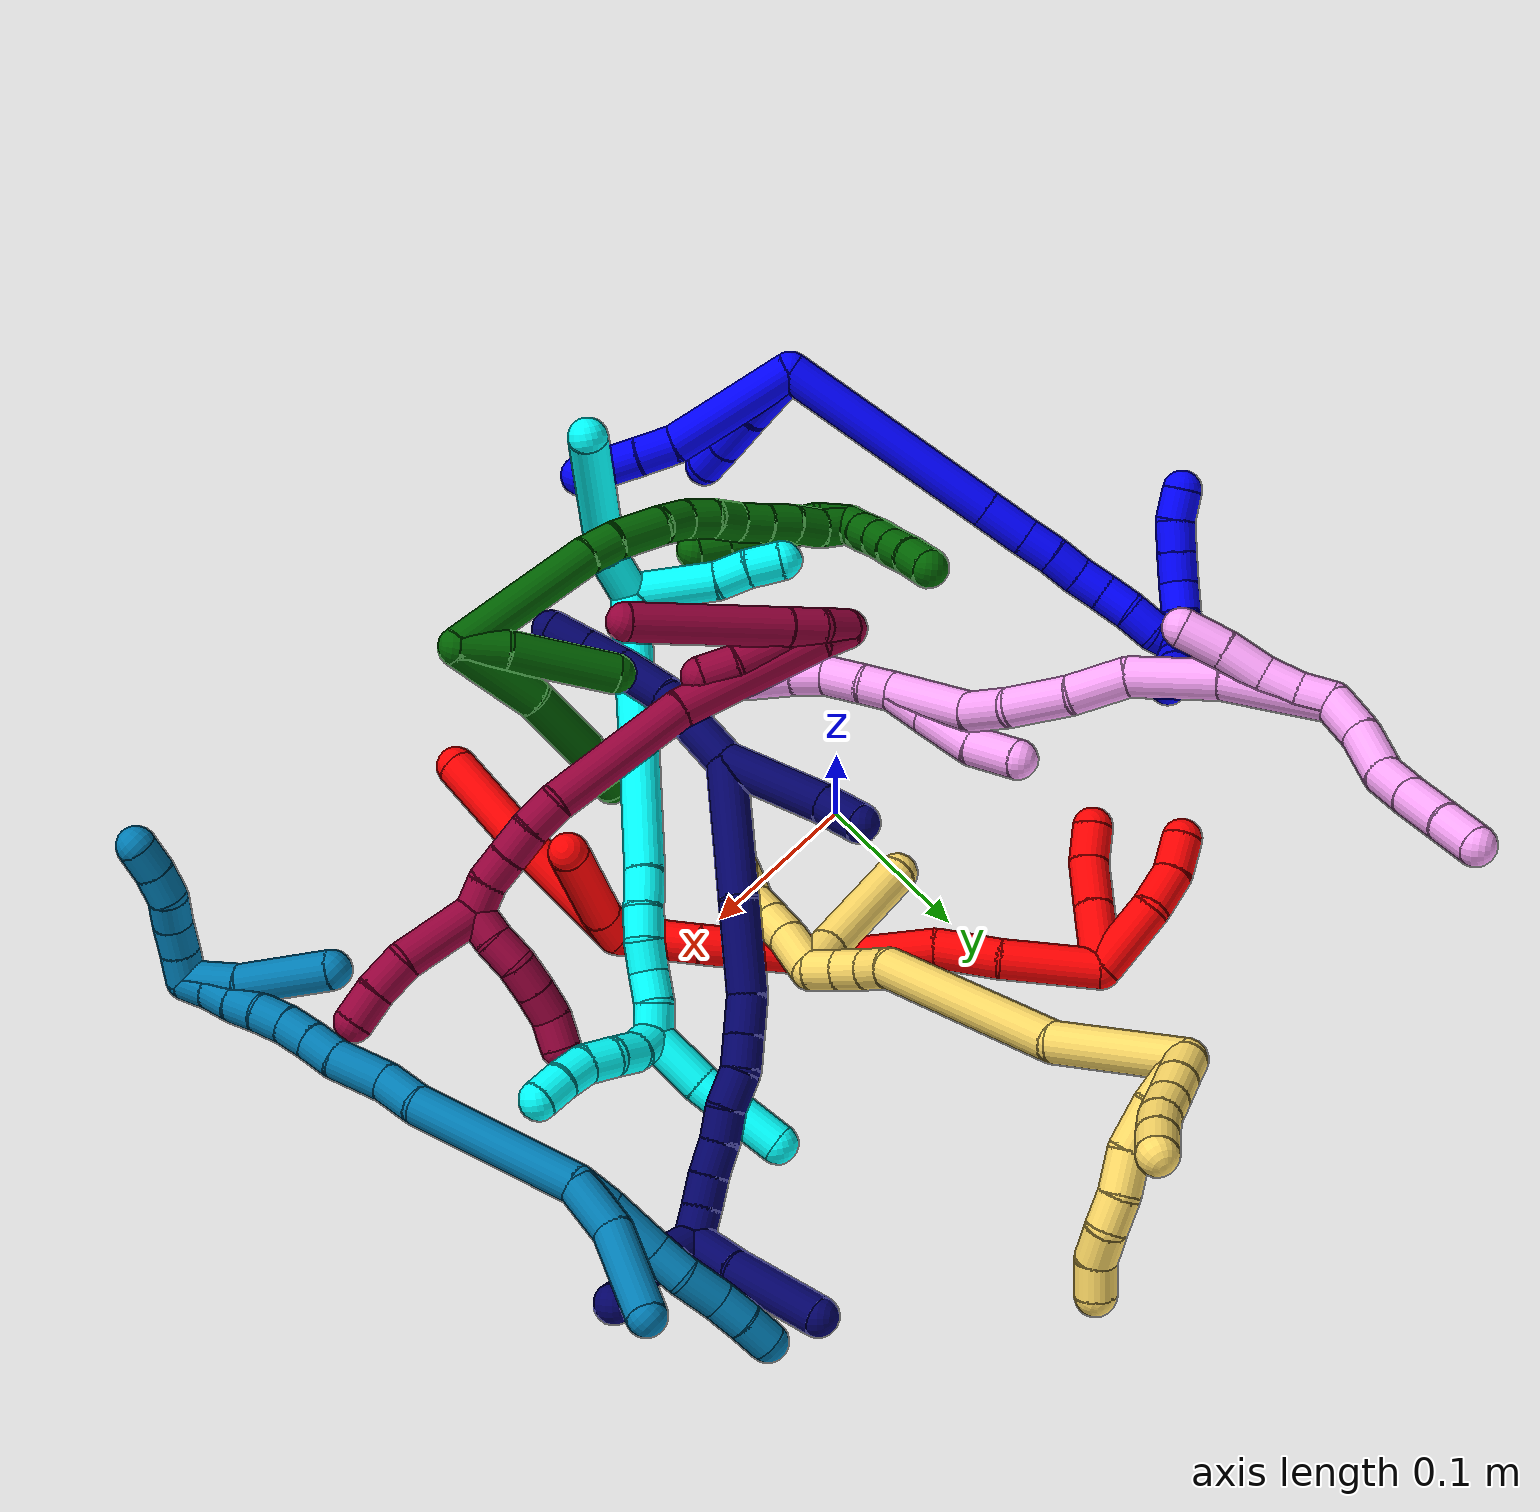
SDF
<sdf version="1.7">
 <world name="default">
  <plugin name="TubeGeneratorPlugin" filename="libtube_generator_plugin.so"/>
  <model name="photoneo_s_sensor">
   <static>1</static>
   <pose>0 0 2 1.57079 1.57079 3.14159</pose>
   <link name="link">
    <inertial><mass>0.1</mass></inertial>
    <sensor name="sensor" type="depth">
     <update_rate>30</update_rate>
     <camera>
      <horizontal_fov>1.22</horizontal_fov>
      <image><width>1920</width><height>1200</height><format>B8G8R8</format></image>
      <clip><near>0.1</near><far>4</far></clip>
      <depth_camera><output>points</output></depth_camera>
     </camera>
     <plugin name="camera_plugin" filename="libgazebo_ros_depth_camera.so">
      <baseline>0.2</baseline>
      <alwaysOn>1</alwaysOn>
      <updateRate>0.0</updateRate>
      <cameraName>camera_ir</cameraName>
      <imageTopicName>/camera/color/image_raw</imageTopicName>
      <cameraInfoTopicName>/camera/color/camera_info</cameraInfoTopicName>
      <depthImageTopicName>/camera/depth/image_raw</depthImageTopicName>
      <depthImageCameraInfoTopicName>/camera/depth/camera_info</depthImageCameraInfoTopicName>
      <pointCloudTopicName>/camera/depth/points</pointCloudTopicName>
      <frameName>fr_optical</frameName>
      <pointCloudCutoff>0.1</pointCloudCutoff>
      <pointCloudCutoffMax>2.0</pointCloudCutoffMax>
      <distortionK1>0</distortionK1>
      <distortionK2>0</distortionK2>
      <distortionK3>0</distortionK3>
      <distortionT1>0</distortionT1>
      <distortionT2>0</distortionT2>
      <CxPrime>0</CxPrime>
      <Cx>0</Cx>
      <Cy>0</Cy>
      <focalLength>0</focalLength>
      <hackBaseline>0</hackBaseline>
     </plugin>
    </sensor>
   </link>
  </model>
  <gravity>0 0 -9.8</gravity>
  <magnetic_field>6e-06 2.3e-05 -4.2e-05</magnetic_field>
  <atmosphere type="adiabatic"/>
  <physics name="default_physics" default="0" type="ode">
   <max_step_size>0.003</max_step_size>
   <real_time_factor>1</real_time_factor>
   <real_time_update_rate>1000</real_time_update_rate>
   <max_contacts>10000</max_contacts>
   <ode>
    <solver>
     <type>quick</type>
     <iters>100</iters>
     <sor>1.3</sor>
     <use_dynamic_moi_rescaling>0</use_dynamic_moi_rescaling>
    </solver>
    <constraints>
     <contact_max_correcting_vel>0</contact_max_correcting_vel>
     <contact_surface_layer>0.001</contact_surface_layer>
     <cfm>0</cfm>
     <erp>0.2</erp>
    </constraints>
   </ode>
  </physics>
  <scene><ambient>0.4 0.4 0.4 1</ambient><background>0.7 0.7 0.7 1</background><shadows>0</shadows></scene>
  <audio><device>default</device></audio>
  <spherical_coordinates>
   <surface_model>EARTH_WGS84</surface_model>
   <latitude_deg>0</latitude_deg>
   <longitude_deg>0</longitude_deg>
   <elevation>0</elevation>
   <heading_deg>0</heading_deg>
  </spherical_coordinates>
  <model name="bin">
   <static>1</static>
   <link name="bottom">
    <collision name="collision-bottom">
     <pose>0 0 -0.01 0 -0 0</pose>
     <geometry><box><size>0.8 0.6 0.02</size></box></geometry>
     <surface>
      <friction><ode><mu>100</mu><mu2>100</mu2></ode></friction>
      <contact><collide_bitmask>65535</collide_bitmask></contact>
     </surface>
    </collision>
   </link>
   <link name="west_wall">
    <collision name="collision-west_wall">
     <pose>-0.41 0 0.1 0 -0 0</pose>
     <geometry><box><size>0.02 0.6 0.2</size></box></geometry>
     <surface>
      <friction><ode><mu>100</mu><mu2>100</mu2></ode></friction>
      <contact><collide_bitmask>65535</collide_bitmask></contact>
     </surface>
    </collision>
   </link>
   <link name="east_wall">
    <collision name="collision-east_wall">
     <pose>0.41 0 0.1 0 -0 0</pose>
     <geometry><box><size>0.02 0.6 0.2</size></box></geometry>
     <surface>
      <friction><ode><mu>100</mu><mu2>100</mu2></ode></friction>
      <contact><collide_bitmask>65535</collide_bitmask></contact>
     </surface>
    </collision>
   </link>
   <link name="south_wall">
    <collision name="collision-south_wall">
     <pose>0 -0.31 0.1 0 -0 0</pose>
     <geometry><box><size>0.8 0.02 0.2</size></box></geometry>
     <surface>
      <friction><ode><mu>100</mu><mu2>100</mu2></ode></friction>
      <contact><collide_bitmask>65535</collide_bitmask></contact>
     </surface>
    </collision>
   </link>
   <link name="north_wall">
    <collision name="collision-north_wall">
     <pose>0 0.31 0.1 0 -0 0</pose>
     <geometry><box><size>0.8 0.02 0.2</size></box></geometry>
     <surface>
      <friction><ode><mu>100</mu><mu2>100</mu2></ode></friction>
      <contact><collide_bitmask>65535</collide_bitmask></contact>
     </surface>
    </collision>
   </link>
  </model>
  <model name="1">
   <static>0</static>
   <link name="1">
    <collision name="collision-cylinder-e_1_2_8">
     <pose>0.019351 -0.02609 -0.028247 2.39587 0.466243 1.09112</pose>
     <geometry><cylinder><radius>0.0125</radius><length>0.086095</length></cylinder></geometry>
     <surface>
      <friction><ode><mu>1.16</mu><mu2>1.16</mu2><slip1>0</slip1><slip2>0</slip2></ode></friction>
      <contact><ode><kp>1e+06</kp><kd>1</kd><max_vel>0</max_vel><min_depth>0.001</min_depth></ode></contact>
     </surface>
    </collision>
    <visual name="visual-cylinder-e_1_2_8">
     <pose>0.019351 -0.02609 -0.028247 2.39587 0.466243 1.09112</pose>
     <geometry><cylinder><radius>0.0125</radius><length>0.086095</length></cylinder></geometry>
     <material><ambient>0 0 1 1</ambient></material>
    </visual>
    <collision name="collision-cylinder-e_2_8_9">
     <pose>0.044976 -0.060756 -0.06206 2.14649 0.550356 0.958788</pose>
     <geometry><cylinder><radius>0.0125</radius><length>0.023989</length></cylinder></geometry>
     <surface>
      <friction><ode><mu>1.16</mu><mu2>1.16</mu2><slip1>0</slip1><slip2>0</slip2></ode></friction>
      <contact><ode><kp>1e+06</kp><kd>1</kd><max_vel>0</max_vel><min_depth>0.001</min_depth></ode></contact>
     </surface>
    </collision>
    <visual name="visual-cylinder-e_2_8_9">
     <pose>0.044976 -0.060756 -0.06206 2.14649 0.550356 0.958788</pose>
     <geometry><cylinder><radius>0.0125</radius><length>0.023989</length></cylinder></geometry>
     <material><ambient>0 0 1 1</ambient></material>
    </visual>
    <collision name="collision-cylinder-e_3_9_6">
     <pose>0.060638 -0.084378 -0.076779 2.11732 0.48981 0.836656</pose>
     <geometry><cylinder><radius>0.0125</radius><length>0.039916</length></cylinder></geometry>
     <surface>
      <friction><ode><mu>1.16</mu><mu2>1.16</mu2><slip1>0</slip1><slip2>0</slip2></ode></friction>
      <contact><ode><kp>1e+06</kp><kd>1</kd><max_vel>0</max_vel><min_depth>0.001</min_depth></ode></contact>
     </surface>
    </collision>
    <visual name="visual-cylinder-e_3_9_6">
     <pose>0.060638 -0.084378 -0.076779 2.11732 0.48981 0.836656</pose>
     <geometry><cylinder><radius>0.0125</radius><length>0.039916</length></cylinder></geometry>
     <material><ambient>0 0 1 1</ambient></material>
    </visual>
    <collision name="collision-cylinder-e_1_2_10">
     <pose>0.000796 -0.012006 -0.016969 2.52581 0.038287 0.120269</pose>
     <geometry><cylinder><radius>0.0125</radius><length>0.041604</length></cylinder></geometry>
     <surface>
      <friction><ode><mu>1.16</mu><mu2>1.16</mu2><slip1>0</slip1><slip2>0</slip2></ode></friction>
      <contact><ode><kp>1e+06</kp><kd>1</kd><max_vel>0</max_vel><min_depth>0.001</min_depth></ode></contact>
     </surface>
    </collision>
    <visual name="visual-cylinder-e_1_2_10">
     <pose>0.000796 -0.012006 -0.016969 2.52581 0.038287 0.120269</pose>
     <geometry><cylinder><radius>0.0125</radius><length>0.041604</length></cylinder></geometry>
     <material><ambient>0 0 1 1</ambient></material>
    </visual>
    <collision name="collision-cylinder-e_2_10_11">
     <pose>-0.000734 -0.034675 -0.04739 2.47139 -0.134705 -0.38267</pose>
     <geometry><cylinder><radius>0.0125</radius><length>0.034646</length></cylinder></geometry>
     <surface>
      <friction><ode><mu>1.16</mu><mu2>1.16</mu2><slip1>0</slip1><slip2>0</slip2></ode></friction>
      <contact><ode><kp>1e+06</kp><kd>1</kd><max_vel>0</max_vel><min_depth>0.001</min_depth></ode></contact>
     </surface>
    </collision>
    <visual name="visual-cylinder-e_2_10_11">
     <pose>-0.000734 -0.034675 -0.04739 2.47139 -0.134705 -0.38267</pose>
     <geometry><cylinder><radius>0.0125</radius><length>0.034646</length></cylinder></geometry>
     <material><ambient>0 0 1 1</ambient></material>
    </visual>
    <collision name="collision-cylinder-e_3_11_5">
     <pose>-0.004501 -0.052752 -0.070007 2.46135 -0.121648 -0.340848</pose>
     <geometry><cylinder><radius>0.0125</radius><length>0.02375</length></cylinder></geometry>
     <surface>
      <friction><ode><mu>1.16</mu><mu2>1.16</mu2><slip1>0</slip1><slip2>0</slip2></ode></friction>
      <contact><ode><kp>1e+06</kp><kd>1</kd><max_vel>0</max_vel><min_depth>0.001</min_depth></ode></contact>
     </surface>
    </collision>
    <visual name="visual-cylinder-e_3_11_5">
     <pose>-0.004501 -0.052752 -0.070007 2.46135 -0.121648 -0.340848</pose>
     <geometry><cylinder><radius>0.0125</radius><length>0.02375</length></cylinder></geometry>
     <material><ambient>0 0 1 1</ambient></material>
    </visual>
    <collision name="collision-cylinder-e_1_2_12">
     <pose>-0.033167 0.057655 -0.033375 -2.09553 -0.461944 0.774527</pose>
     <geometry><cylinder><radius>0.0125</radius><length>0.148836</length></cylinder></geometry>
     <surface>
      <friction><ode><mu>1.16</mu><mu2>1.16</mu2><slip1>0</slip1><slip2>0</slip2></ode></friction>
      <contact><ode><kp>1e+06</kp><kd>1</kd><max_vel>0</max_vel><min_depth>0.001</min_depth></ode></contact>
     </surface>
    </collision>
    <visual name="visual-cylinder-e_1_2_12">
     <pose>-0.033167 0.057655 -0.033375 -2.09553 -0.461944 0.774527</pose>
     <geometry><cylinder><radius>0.0125</radius><length>0.148836</length></cylinder></geometry>
     <material><ambient>0 0 1 1</ambient></material>
    </visual>
    <collision name="collision-cylinder-e_2_12_13">
     <pose>-0.073022 0.127048 -0.073546 -2.09564 -0.458087 0.768553</pose>
     <geometry><cylinder><radius>0.0125</radius><length>0.030246</length></cylinder></geometry>
     <surface>
      <friction><ode><mu>1.16</mu><mu2>1.16</mu2><slip1>0</slip1><slip2>0</slip2></ode></friction>
      <contact><ode><kp>1e+06</kp><kd>1</kd><max_vel>0</max_vel><min_depth>0.001</min_depth></ode></contact>
     </surface>
    </collision>
    <visual name="visual-cylinder-e_2_12_13">
     <pose>-0.073022 0.127048 -0.073546 -2.09564 -0.458087 0.768553</pose>
     <geometry><cylinder><radius>0.0125</radius><length>0.030246</length></cylinder></geometry>
     <material><ambient>0 0 1 1</ambient></material>
    </visual>
    <collision name="collision-cylinder-e_3_13_14">
     <pose>-0.084422 0.146901 -0.084722 -2.06579 -0.472416 0.766988</pose>
     <geometry><cylinder><radius>0.0125</radius><length>0.02071</length></cylinder></geometry>
     <surface>
      <friction><ode><mu>1.16</mu><mu2>1.16</mu2><slip1>0</slip1><slip2>0</slip2></ode></friction>
      <contact><ode><kp>1e+06</kp><kd>1</kd><max_vel>0</max_vel><min_depth>0.001</min_depth></ode></contact>
     </surface>
    </collision>
    <visual name="visual-cylinder-e_3_13_14">
     <pose>-0.084422 0.146901 -0.084722 -2.06579 -0.472416 0.766988</pose>
     <geometry><cylinder><radius>0.0125</radius><length>0.02071</length></cylinder></geometry>
     <material><ambient>0 0 1 1</ambient></material>
    </visual>
    <collision name="collision-cylinder-e_4_14_15">
     <pose>-0.093744 0.162376 -0.094261 -2.18206 -0.47382 0.868926</pose>
     <geometry><cylinder><radius>0.0125</radius><length>0.020203</length></cylinder></geometry>
     <surface>
      <friction><ode><mu>1.16</mu><mu2>1.16</mu2><slip1>0</slip1><slip2>0</slip2></ode></friction>
      <contact><ode><kp>1e+06</kp><kd>1</kd><max_vel>0</max_vel><min_depth>0.001</min_depth></ode></contact>
     </surface>
    </collision>
    <visual name="visual-cylinder-e_4_14_15">
     <pose>-0.093744 0.162376 -0.094261 -2.18206 -0.47382 0.868926</pose>
     <geometry><cylinder><radius>0.0125</radius><length>0.020203</length></cylinder></geometry>
     <material><ambient>0 0 1 1</ambient></material>
    </visual>
    <collision name="collision-cylinder-e_5_15_16">
     <pose>-0.10217 0.17804 -0.103485 -2.02612 -0.391609 0.61571</pose>
     <geometry><cylinder><radius>0.0125</radius><length>0.020003</length></cylinder></geometry>
     <surface>
      <friction><ode><mu>1.16</mu><mu2>1.16</mu2><slip1>0</slip1><slip2>0</slip2></ode></friction>
      <contact><ode><kp>1e+06</kp><kd>1</kd><max_vel>0</max_vel><min_depth>0.001</min_depth></ode></contact>
     </surface>
    </collision>
    <visual name="visual-cylinder-e_5_15_16">
     <pose>-0.10217 0.17804 -0.103485 -2.02612 -0.391609 0.61571</pose>
     <geometry><cylinder><radius>0.0125</radius><length>0.020003</length></cylinder></geometry>
     <material><ambient>0 0 1 1</ambient></material>
    </visual>
    <collision name="collision-cylinder-e_6_16_17">
     <pose>-0.108694 0.195161 -0.111411 -1.98338 -0.274033 0.415636</pose>
     <geometry><cylinder><radius>0.0125</radius><length>0.02</length></cylinder></geometry>
     <surface>
      <friction><ode><mu>1.16</mu><mu2>1.16</mu2><slip1>0</slip1><slip2>0</slip2></ode></friction>
      <contact><ode><kp>1e+06</kp><kd>1</kd><max_vel>0</max_vel><min_depth>0.001</min_depth></ode></contact>
     </surface>
    </collision>
    <visual name="visual-cylinder-e_6_16_17">
     <pose>-0.108694 0.195161 -0.111411 -1.98338 -0.274033 0.415636</pose>
     <geometry><cylinder><radius>0.0125</radius><length>0.02</length></cylinder></geometry>
     <material><ambient>0 0 1 1</ambient></material>
    </visual>
    <collision name="collision-cylinder-e_7_17_18">
     <pose>-0.115143 0.211743 -0.120345 -2.1497 -0.383611 0.689193</pose>
     <geometry><cylinder><radius>0.0125</radius><length>0.020001</length></cylinder></geometry>
     <surface>
      <friction><ode><mu>1.16</mu><mu2>1.16</mu2><slip1>0</slip1><slip2>0</slip2></ode></friction>
      <contact><ode><kp>1e+06</kp><kd>1</kd><max_vel>0</max_vel><min_depth>0.001</min_depth></ode></contact>
     </surface>
    </collision>
    <visual name="visual-cylinder-e_7_17_18">
     <pose>-0.115143 0.211743 -0.120345 -2.1497 -0.383611 0.689193</pose>
     <geometry><cylinder><radius>0.0125</radius><length>0.020001</length></cylinder></geometry>
     <material><ambient>0 0 1 1</ambient></material>
    </visual>
    <collision name="collision-cylinder-e_8_18_1">
     <pose>-0.124983 0.226666 -0.128817 -2.01401 -0.655673 0.987077</pose>
     <geometry><cylinder><radius>0.0125</radius><length>0.02</length></cylinder></geometry>
     <surface>
      <friction><ode><mu>1.16</mu><mu2>1.16</mu2><slip1>0</slip1><slip2>0</slip2></ode></friction>
      <contact><ode><kp>1e+06</kp><kd>1</kd><max_vel>0</max_vel><min_depth>0.001</min_depth></ode></contact>
     </surface>
    </collision>
    <visual name="visual-cylinder-e_8_18_1">
     <pose>-0.124983 0.226666 -0.128817 -2.01401 -0.655673 0.987077</pose>
     <geometry><cylinder><radius>0.0125</radius><length>0.02</length></cylinder></geometry>
     <material><ambient>0 0 1 1</ambient></material>
    </visual>
    <collision name="collision-cylinder-e_1_1_19">
     <pose>-0.108716 0.245962 -0.12997 -1.3877 1.06655 -0.912916</pose>
     <geometry><cylinder><radius>0.0125</radius><length>0.051086</length></cylinder></geometry>
     <surface>
      <friction><ode><mu>1.16</mu><mu2>1.16</mu2><slip1>0</slip1><slip2>0</slip2></ode></friction>
      <contact><ode><kp>1e+06</kp><kd>1</kd><max_vel>0</max_vel><min_depth>0.001</min_depth></ode></contact>
     </surface>
    </collision>
    <visual name="visual-cylinder-e_1_1_19">
     <pose>-0.108716 0.245962 -0.12997 -1.3877 1.06655 -0.912916</pose>
     <geometry><cylinder><radius>0.0125</radius><length>0.051086</length></cylinder></geometry>
     <material><ambient>0 0 1 1</ambient></material>
    </visual>
    <collision name="collision-cylinder-e_2_19_20">
     <pose>-0.077275 0.263837 -0.127152 -1.47168 1.00465 -0.92314</pose>
     <geometry><cylinder><radius>0.0125</radius><length>0.021511</length></cylinder></geometry>
     <surface>
      <friction><ode><mu>1.16</mu><mu2>1.16</mu2><slip1>0</slip1><slip2>0</slip2></ode></friction>
      <contact><ode><kp>1e+06</kp><kd>1</kd><max_vel>0</max_vel><min_depth>0.001</min_depth></ode></contact>
     </surface>
    </collision>
    <visual name="visual-cylinder-e_2_19_20">
     <pose>-0.077275 0.263837 -0.127152 -1.47168 1.00465 -0.92314</pose>
     <geometry><cylinder><radius>0.0125</radius><length>0.021511</length></cylinder></geometry>
     <material><ambient>0 0 1 1</ambient></material>
    </visual>
    <collision name="collision-cylinder-e_3_20_4">
     <pose>-0.055737 0.275237 -0.127256 -1.68954 1.14184 -1.25257</pose>
     <geometry><cylinder><radius>0.0125</radius><length>0.027403</length></cylinder></geometry>
     <surface>
      <friction><ode><mu>1.16</mu><mu2>1.16</mu2><slip1>0</slip1><slip2>0</slip2></ode></friction>
      <contact><ode><kp>1e+06</kp><kd>1</kd><max_vel>0</max_vel><min_depth>0.001</min_depth></ode></contact>
     </surface>
    </collision>
    <visual name="visual-cylinder-e_3_20_4">
     <pose>-0.055737 0.275237 -0.127256 -1.68954 1.14184 -1.25257</pose>
     <geometry><cylinder><radius>0.0125</radius><length>0.027403</length></cylinder></geometry>
     <material><ambient>0 0 1 1</ambient></material>
    </visual>
    <collision name="collision-cylinder-e_1_1_21">
     <pose>-0.1347 0.229656 -0.12388 0.463906 -0.37045 -0.088459</pose>
     <geometry><cylinder><radius>0.0125</radius><length>0.02</length></cylinder></geometry>
     <surface>
      <friction><ode><mu>1.16</mu><mu2>1.16</mu2><slip1>0</slip1><slip2>0</slip2></ode></friction>
      <contact><ode><kp>1e+06</kp><kd>1</kd><max_vel>0</max_vel><min_depth>0.001</min_depth></ode></contact>
     </surface>
    </collision>
    <visual name="visual-cylinder-e_1_1_21">
     <pose>-0.1347 0.229656 -0.12388 0.463906 -0.37045 -0.088459</pose>
     <geometry><cylinder><radius>0.0125</radius><length>0.02</length></cylinder></geometry>
     <material><ambient>0 0 1 1</ambient></material>
    </visual>
    <collision name="collision-cylinder-e_2_21_22">
     <pose>-0.142109 0.220438 -0.107787 0.576845 -0.38861 -0.11664</pose>
     <geometry><cylinder><radius>0.0125</radius><length>0.02</length></cylinder></geometry>
     <surface>
      <friction><ode><mu>1.16</mu><mu2>1.16</mu2><slip1>0</slip1><slip2>0</slip2></ode></friction>
      <contact><ode><kp>1e+06</kp><kd>1</kd><max_vel>0</max_vel><min_depth>0.001</min_depth></ode></contact>
     </surface>
    </collision>
    <visual name="visual-cylinder-e_2_21_22">
     <pose>-0.142109 0.220438 -0.107787 0.576845 -0.38861 -0.11664</pose>
     <geometry><cylinder><radius>0.0125</radius><length>0.02</length></cylinder></geometry>
     <material><ambient>0 0 1 1</ambient></material>
    </visual>
    <collision name="collision-cylinder-e_3_22_23">
     <pose>-0.147665 0.211712 -0.0909 0.382996 -0.177582 -0.034516</pose>
     <geometry><cylinder><radius>0.0125</radius><length>0.02</length></cylinder></geometry>
     <surface>
      <friction><ode><mu>1.16</mu><mu2>1.16</mu2><slip1>0</slip1><slip2>0</slip2></ode></friction>
      <contact><ode><kp>1e+06</kp><kd>1</kd><max_vel>0</max_vel><min_depth>0.001</min_depth></ode></contact>
     </surface>
    </collision>
    <visual name="visual-cylinder-e_3_22_23">
     <pose>-0.147665 0.211712 -0.0909 0.382996 -0.177582 -0.034516</pose>
     <geometry><cylinder><radius>0.0125</radius><length>0.02</length></cylinder></geometry>
     <material><ambient>0 0 1 1</ambient></material>
    </visual>
    <collision name="collision-cylinder-e_4_23_24">
     <pose>-0.151206 0.204555 -0.072565 0.361352 -0.178394 -0.032671</pose>
     <geometry><cylinder><radius>0.0125</radius><length>0.02</length></cylinder></geometry>
     <surface>
      <friction><ode><mu>1.16</mu><mu2>1.16</mu2><slip1>0</slip1><slip2>0</slip2></ode></friction>
      <contact><ode><kp>1e+06</kp><kd>1</kd><max_vel>0</max_vel><min_depth>0.001</min_depth></ode></contact>
     </surface>
    </collision>
    <visual name="visual-cylinder-e_4_23_24">
     <pose>-0.151206 0.204555 -0.072565 0.361352 -0.178394 -0.032671</pose>
     <geometry><cylinder><radius>0.0125</radius><length>0.02</length></cylinder></geometry>
     <material><ambient>0 0 1 1</ambient></material>
    </visual>
    <collision name="collision-cylinder-e_5_24_3">
     <pose>-0.156098 0.199839 -0.053938 0.130565 -0.317033 -0.020901</pose>
     <geometry><cylinder><radius>0.0125</radius><length>0.02</length></cylinder></geometry>
     <surface>
      <friction><ode><mu>1.16</mu><mu2>1.16</mu2><slip1>0</slip1><slip2>0</slip2></ode></friction>
      <contact><ode><kp>1e+06</kp><kd>1</kd><max_vel>0</max_vel><min_depth>0.001</min_depth></ode></contact>
     </surface>
    </collision>
    <visual name="visual-cylinder-e_5_24_3">
     <pose>-0.156098 0.199839 -0.053938 0.130565 -0.317033 -0.020901</pose>
     <geometry><cylinder><radius>0.0125</radius><length>0.02</length></cylinder></geometry>
     <material><ambient>0 0 1 1</ambient></material>
    </visual>
    <collision name="collision-sphere-3">
     <pose>-0.159215 0.198601 -0.044518 0 -0 0</pose>
     <geometry><sphere><radius>0.0125</radius></sphere></geometry>
     <surface>
      <friction><ode><mu>1.16</mu><mu2>1.16</mu2><slip1>0</slip1><slip2>0</slip2></ode></friction>
      <contact><ode><kp>1e+06</kp><kd>1</kd><max_vel>0</max_vel><min_depth>0.001</min_depth></ode></contact>
     </surface>
    </collision>
    <visual name="visual-sphere-3">
     <pose>-0.159215 0.198601 -0.044518 0 -0 0</pose>
     <geometry><sphere><radius>0.0125</radius></sphere></geometry>
     <material><ambient>0 0 1 1</ambient></material>
    </visual>
    <collision name="collision-sphere-24">
     <pose>-0.15298 0.201076 -0.063359 0 -0 0</pose>
     <geometry><sphere><radius>0.0125</radius></sphere></geometry>
     <surface>
      <friction><ode><mu>1.16</mu><mu2>1.16</mu2><slip1>0</slip1><slip2>0</slip2></ode></friction>
      <contact><ode><kp>1e+06</kp><kd>1</kd><max_vel>0</max_vel><min_depth>0.001</min_depth></ode></contact>
     </surface>
    </collision>
    <visual name="visual-sphere-24">
     <pose>-0.15298 0.201076 -0.063359 0 -0 0</pose>
     <geometry><sphere><radius>0.0125</radius></sphere></geometry>
     <material><ambient>0 0 1 1</ambient></material>
    </visual>
    <collision name="collision-sphere-23">
     <pose>-0.149431 0.208034 -0.081771 0 -0 0</pose>
     <geometry><sphere><radius>0.0125</radius></sphere></geometry>
     <surface>
      <friction><ode><mu>1.16</mu><mu2>1.16</mu2><slip1>0</slip1><slip2>0</slip2></ode></friction>
      <contact><ode><kp>1e+06</kp><kd>1</kd><max_vel>0</max_vel><min_depth>0.001</min_depth></ode></contact>
     </surface>
    </collision>
    <visual name="visual-sphere-23">
     <pose>-0.149431 0.208034 -0.081771 0 -0 0</pose>
     <geometry><sphere><radius>0.0125</radius></sphere></geometry>
     <material><ambient>0 0 1 1</ambient></material>
    </visual>
    <collision name="collision-sphere-22">
     <pose>-0.145898 0.215391 -0.10003 0 -0 0</pose>
     <geometry><sphere><radius>0.0125</radius></sphere></geometry>
     <surface>
      <friction><ode><mu>1.16</mu><mu2>1.16</mu2><slip1>0</slip1><slip2>0</slip2></ode></friction>
      <contact><ode><kp>1e+06</kp><kd>1</kd><max_vel>0</max_vel><min_depth>0.001</min_depth></ode></contact>
     </surface>
    </collision>
    <visual name="visual-sphere-22">
     <pose>-0.145898 0.215391 -0.10003 0 -0 0</pose>
     <geometry><sphere><radius>0.0125</radius></sphere></geometry>
     <material><ambient>0 0 1 1</ambient></material>
    </visual>
    <collision name="collision-sphere-21">
     <pose>-0.13832 0.225485 -0.115544 0 -0 0</pose>
     <geometry><sphere><radius>0.0125</radius></sphere></geometry>
     <surface>
      <friction><ode><mu>1.16</mu><mu2>1.16</mu2><slip1>0</slip1><slip2>0</slip2></ode></friction>
      <contact><ode><kp>1e+06</kp><kd>1</kd><max_vel>0</max_vel><min_depth>0.001</min_depth></ode></contact>
     </surface>
    </collision>
    <visual name="visual-sphere-21">
     <pose>-0.13832 0.225485 -0.115544 0 -0 0</pose>
     <geometry><sphere><radius>0.0125</radius></sphere></geometry>
     <material><ambient>0 0 1 1</ambient></material>
    </visual>
    <collision name="collision-sphere-4">
     <pose>-0.043277 0.280895 -0.127931 0 -0 0</pose>
     <geometry><sphere><radius>0.0125</radius></sphere></geometry>
     <surface>
      <friction><ode><mu>1.16</mu><mu2>1.16</mu2><slip1>0</slip1><slip2>0</slip2></ode></friction>
      <contact><ode><kp>1e+06</kp><kd>1</kd><max_vel>0</max_vel><min_depth>0.001</min_depth></ode></contact>
     </surface>
    </collision>
    <visual name="visual-sphere-4">
     <pose>-0.043277 0.280895 -0.127931 0 -0 0</pose>
     <geometry><sphere><radius>0.0125</radius></sphere></geometry>
     <material><ambient>0 0 1 1</ambient></material>
    </visual>
    <collision name="collision-sphere-20">
     <pose>-0.068197 0.269578 -0.126581 0 -0 0</pose>
     <geometry><sphere><radius>0.0125</radius></sphere></geometry>
     <surface>
      <friction><ode><mu>1.16</mu><mu2>1.16</mu2><slip1>0</slip1><slip2>0</slip2></ode></friction>
      <contact><ode><kp>1e+06</kp><kd>1</kd><max_vel>0</max_vel><min_depth>0.001</min_depth></ode></contact>
     </surface>
    </collision>
    <visual name="visual-sphere-20">
     <pose>-0.068197 0.269578 -0.126581 0 -0 0</pose>
     <geometry><sphere><radius>0.0125</radius></sphere></geometry>
     <material><ambient>0 0 1 1</ambient></material>
    </visual>
    <collision name="collision-sphere-11">
     <pose>-0.00306 -0.045338 -0.060843 0 -0 0</pose>
     <geometry><sphere><radius>0.0125</radius></sphere></geometry>
     <surface>
      <friction><ode><mu>1.16</mu><mu2>1.16</mu2><slip1>0</slip1><slip2>0</slip2></ode></friction>
      <contact><ode><kp>1e+06</kp><kd>1</kd><max_vel>0</max_vel><min_depth>0.001</min_depth></ode></contact>
     </surface>
    </collision>
    <visual name="visual-sphere-11">
     <pose>-0.00306 -0.045338 -0.060843 0 -0 0</pose>
     <geometry><sphere><radius>0.0125</radius></sphere></geometry>
     <material><ambient>0 0 1 1</ambient></material>
    </visual>
    <collision name="collision-sphere-10">
     <pose>0.001593 -0.024013 -0.033938 0 -0 0</pose>
     <geometry><sphere><radius>0.0125</radius></sphere></geometry>
     <surface>
      <friction><ode><mu>1.16</mu><mu2>1.16</mu2><slip1>0</slip1><slip2>0</slip2></ode></friction>
      <contact><ode><kp>1e+06</kp><kd>1</kd><max_vel>0</max_vel><min_depth>0.001</min_depth></ode></contact>
     </surface>
    </collision>
    <visual name="visual-sphere-10">
     <pose>0.001593 -0.024013 -0.033938 0 -0 0</pose>
     <geometry><sphere><radius>0.0125</radius></sphere></geometry>
     <material><ambient>0 0 1 1</ambient></material>
    </visual>
    <collision name="collision-sphere-6">
     <pose>0.070027 -0.099424 -0.085932 0 -0 0</pose>
     <geometry><sphere><radius>0.0125</radius></sphere></geometry>
     <surface>
      <friction><ode><mu>1.16</mu><mu2>1.16</mu2><slip1>0</slip1><slip2>0</slip2></ode></friction>
      <contact><ode><kp>1e+06</kp><kd>1</kd><max_vel>0</max_vel><min_depth>0.001</min_depth></ode></contact>
     </surface>
    </collision>
    <visual name="visual-sphere-6">
     <pose>0.070027 -0.099424 -0.085932 0 -0 0</pose>
     <geometry><sphere><radius>0.0125</radius></sphere></geometry>
     <material><ambient>0 0 1 1</ambient></material>
    </visual>
    <collision name="collision-sphere-9">
     <pose>0.051249 -0.069332 -0.067626 0 -0 0</pose>
     <geometry><sphere><radius>0.0125</radius></sphere></geometry>
     <surface>
      <friction><ode><mu>1.16</mu><mu2>1.16</mu2><slip1>0</slip1><slip2>0</slip2></ode></friction>
      <contact><ode><kp>1e+06</kp><kd>1</kd><max_vel>0</max_vel><min_depth>0.001</min_depth></ode></contact>
     </surface>
    </collision>
    <visual name="visual-sphere-9">
     <pose>0.051249 -0.069332 -0.067626 0 -0 0</pose>
     <geometry><sphere><radius>0.0125</radius></sphere></geometry>
     <material><ambient>0 0 1 1</ambient></material>
    </visual>
    <collision name="collision-sphere-2">
     <geometry><sphere><radius>0.0125</radius></sphere></geometry>
     <surface>
      <friction><ode><mu>1.16</mu><mu2>1.16</mu2><slip1>0</slip1><slip2>0</slip2></ode></friction>
      <contact><ode><kp>1e+06</kp><kd>1</kd><max_vel>0</max_vel><min_depth>0.001</min_depth></ode></contact>
     </surface>
    </collision>
    <visual name="visual-sphere-2">
     <geometry><sphere><radius>0.0125</radius></sphere></geometry>
     <material><ambient>0 0 1 1</ambient></material>
    </visual>
    <collision name="collision-sphere-19">
     <pose>-0.086352 0.258097 -0.127723 0 -0 0</pose>
     <geometry><sphere><radius>0.0125</radius></sphere></geometry>
     <surface>
      <friction><ode><mu>1.16</mu><mu2>1.16</mu2><slip1>0</slip1><slip2>0</slip2></ode></friction>
      <contact><ode><kp>1e+06</kp><kd>1</kd><max_vel>0</max_vel><min_depth>0.001</min_depth></ode></contact>
     </surface>
    </collision>
    <visual name="visual-sphere-19">
     <pose>-0.086352 0.258097 -0.127723 0 -0 0</pose>
     <geometry><sphere><radius>0.0125</radius></sphere></geometry>
     <material><ambient>0 0 1 1</ambient></material>
    </visual>
    <collision name="collision-sphere-8">
     <pose>0.038702 -0.05218 -0.056494 0 -0 0</pose>
     <geometry><sphere><radius>0.0125</radius></sphere></geometry>
     <surface>
      <friction><ode><mu>1.16</mu><mu2>1.16</mu2><slip1>0</slip1><slip2>0</slip2></ode></friction>
      <contact><ode><kp>1e+06</kp><kd>1</kd><max_vel>0</max_vel><min_depth>0.001</min_depth></ode></contact>
     </surface>
    </collision>
    <visual name="visual-sphere-8">
     <pose>0.038702 -0.05218 -0.056494 0 -0 0</pose>
     <geometry><sphere><radius>0.0125</radius></sphere></geometry>
     <material><ambient>0 0 1 1</ambient></material>
    </visual>
    <collision name="collision-sphere-5">
     <pose>-0.005942 -0.060166 -0.079171 0 -0 0</pose>
     <geometry><sphere><radius>0.0125</radius></sphere></geometry>
     <surface>
      <friction><ode><mu>1.16</mu><mu2>1.16</mu2><slip1>0</slip1><slip2>0</slip2></ode></friction>
      <contact><ode><kp>1e+06</kp><kd>1</kd><max_vel>0</max_vel><min_depth>0.001</min_depth></ode></contact>
     </surface>
    </collision>
    <visual name="visual-sphere-5">
     <pose>-0.005942 -0.060166 -0.079171 0 -0 0</pose>
     <geometry><sphere><radius>0.0125</radius></sphere></geometry>
     <material><ambient>0 0 1 1</ambient></material>
    </visual>
    <collision name="collision-sphere-12">
     <pose>-0.066334 0.11531 -0.066749 0 -0 0</pose>
     <geometry><sphere><radius>0.0125</radius></sphere></geometry>
     <surface>
      <friction><ode><mu>1.16</mu><mu2>1.16</mu2><slip1>0</slip1><slip2>0</slip2></ode></friction>
      <contact><ode><kp>1e+06</kp><kd>1</kd><max_vel>0</max_vel><min_depth>0.001</min_depth></ode></contact>
     </surface>
    </collision>
    <visual name="visual-sphere-12">
     <pose>-0.066334 0.11531 -0.066749 0 -0 0</pose>
     <geometry><sphere><radius>0.0125</radius></sphere></geometry>
     <material><ambient>0 0 1 1</ambient></material>
    </visual>
    <collision name="collision-sphere-13">
     <pose>-0.07971 0.138786 -0.080342 0 -0 0</pose>
     <geometry><sphere><radius>0.0125</radius></sphere></geometry>
     <surface>
      <friction><ode><mu>1.16</mu><mu2>1.16</mu2><slip1>0</slip1><slip2>0</slip2></ode></friction>
      <contact><ode><kp>1e+06</kp><kd>1</kd><max_vel>0</max_vel><min_depth>0.001</min_depth></ode></contact>
     </surface>
    </collision>
    <visual name="visual-sphere-13">
     <pose>-0.07971 0.138786 -0.080342 0 -0 0</pose>
     <geometry><sphere><radius>0.0125</radius></sphere></geometry>
     <material><ambient>0 0 1 1</ambient></material>
    </visual>
    <collision name="collision-sphere-14">
     <pose>-0.089134 0.155015 -0.089103 0 -0 0</pose>
     <geometry><sphere><radius>0.0125</radius></sphere></geometry>
     <surface>
      <friction><ode><mu>1.16</mu><mu2>1.16</mu2><slip1>0</slip1><slip2>0</slip2></ode></friction>
      <contact><ode><kp>1e+06</kp><kd>1</kd><max_vel>0</max_vel><min_depth>0.001</min_depth></ode></contact>
     </surface>
    </collision>
    <visual name="visual-sphere-14">
     <pose>-0.089134 0.155015 -0.089103 0 -0 0</pose>
     <geometry><sphere><radius>0.0125</radius></sphere></geometry>
     <material><ambient>0 0 1 1</ambient></material>
    </visual>
    <collision name="collision-sphere-15">
     <pose>-0.098353 0.169737 -0.09942 0 -0 0</pose>
     <geometry><sphere><radius>0.0125</radius></sphere></geometry>
     <surface>
      <friction><ode><mu>1.16</mu><mu2>1.16</mu2><slip1>0</slip1><slip2>0</slip2></ode></friction>
      <contact><ode><kp>1e+06</kp><kd>1</kd><max_vel>0</max_vel><min_depth>0.001</min_depth></ode></contact>
     </surface>
    </collision>
    <visual name="visual-sphere-15">
     <pose>-0.098353 0.169737 -0.09942 0 -0 0</pose>
     <geometry><sphere><radius>0.0125</radius></sphere></geometry>
     <material><ambient>0 0 1 1</ambient></material>
    </visual>
    <collision name="collision-sphere-16">
     <pose>-0.105988 0.186342 -0.107551 0 -0 0</pose>
     <geometry><sphere><radius>0.0125</radius></sphere></geometry>
     <surface>
      <friction><ode><mu>1.16</mu><mu2>1.16</mu2><slip1>0</slip1><slip2>0</slip2></ode></friction>
      <contact><ode><kp>1e+06</kp><kd>1</kd><max_vel>0</max_vel><min_depth>0.001</min_depth></ode></contact>
     </surface>
    </collision>
    <visual name="visual-sphere-16">
     <pose>-0.105988 0.186342 -0.107551 0 -0 0</pose>
     <geometry><sphere><radius>0.0125</radius></sphere></geometry>
     <material><ambient>0 0 1 1</ambient></material>
    </visual>
    <collision name="collision-sphere-17">
     <pose>-0.1114 0.203981 -0.115271 0 -0 0</pose>
     <geometry><sphere><radius>0.0125</radius></sphere></geometry>
     <surface>
      <friction><ode><mu>1.16</mu><mu2>1.16</mu2><slip1>0</slip1><slip2>0</slip2></ode></friction>
      <contact><ode><kp>1e+06</kp><kd>1</kd><max_vel>0</max_vel><min_depth>0.001</min_depth></ode></contact>
     </surface>
    </collision>
    <visual name="visual-sphere-17">
     <pose>-0.1114 0.203981 -0.115271 0 -0 0</pose>
     <geometry><sphere><radius>0.0125</radius></sphere></geometry>
     <material><ambient>0 0 1 1</ambient></material>
    </visual>
    <collision name="collision-sphere-18">
     <pose>-0.118886 0.219506 -0.125418 0 -0 0</pose>
     <geometry><sphere><radius>0.0125</radius></sphere></geometry>
     <surface>
      <friction><ode><mu>1.16</mu><mu2>1.16</mu2><slip1>0</slip1><slip2>0</slip2></ode></friction>
      <contact><ode><kp>1e+06</kp><kd>1</kd><max_vel>0</max_vel><min_depth>0.001</min_depth></ode></contact>
     </surface>
    </collision>
    <visual name="visual-sphere-18">
     <pose>-0.118886 0.219506 -0.125418 0 -0 0</pose>
     <geometry><sphere><radius>0.0125</radius></sphere></geometry>
     <material><ambient>0 0 1 1</ambient></material>
    </visual>
    <collision name="collision-sphere-1">
     <pose>-0.13108 0.233827 -0.132217 0 -0 0</pose>
     <geometry><sphere><radius>0.0125</radius></sphere></geometry>
     <surface>
      <friction><ode><mu>1.16</mu><mu2>1.16</mu2><slip1>0</slip1><slip2>0</slip2></ode></friction>
      <contact><ode><kp>1e+06</kp><kd>1</kd><max_vel>0</max_vel><min_depth>0.001</min_depth></ode></contact>
     </surface>
    </collision>
    <visual name="visual-sphere-1">
     <pose>-0.13108 0.233827 -0.132217 0 -0 0</pose>
     <geometry><sphere><radius>0.0125</radius></sphere></geometry>
     <material><ambient>0 0 1 1</ambient></material>
    </visual>
    <inertial>
     <pose>-0.050827 0.096082 -0.070629 0 -0 0</pose>
     <mass>0.75</mass>
     <inertia>
      <ixx>0.000466</ixx>
      <ixy>0</ixy>
      <ixz>0</ixz>
      <iyy>0.000211</iyy>
      <iyz>0</iyz>
      <izz>-0.000111</izz>
     </inertia>
    </inertial>
   </link>
   <pose>-0.16149 -0.206146 0.089859 0.558635 -0.719995 -0.134622</pose>
  </model>
  <model name="2">
   <static>0</static>
   <link name="2">
    <collision name="collision-cylinder-e_1_2_8">
     <pose>-0.009472 -0.03938 0.013061 1.25055 -0.224453 -0.162359</pose>
     <geometry><cylinder><radius>0.0125</radius><length>0.085114</length></cylinder></geometry>
     <surface>
      <friction><ode><mu>1.16</mu><mu2>1.16</mu2><slip1>0</slip1><slip2>0</slip2></ode></friction>
      <contact><ode><kp>1e+06</kp><kd>1</kd><max_vel>0</max_vel><min_depth>0.001</min_depth></ode></contact>
     </surface>
    </collision>
    <visual name="visual-cylinder-e_1_2_8">
     <pose>-0.009472 -0.03938 0.013061 1.25055 -0.224453 -0.162359</pose>
     <geometry><cylinder><radius>0.0125</radius><length>0.085114</length></cylinder></geometry>
     <material><ambient>1 0 0 1</ambient></material>
    </visual>
    <collision name="collision-cylinder-e_2_8_6">
     <pose>-0.028005 -0.109912 0.0263 1.56509 -0.283037 -0.281447</pose>
     <geometry><cylinder><radius>0.0125</radius><length>0.064886</length></cylinder></geometry>
     <surface>
      <friction><ode><mu>1.16</mu><mu2>1.16</mu2><slip1>0</slip1><slip2>0</slip2></ode></friction>
      <contact><ode><kp>1e+06</kp><kd>1</kd><max_vel>0</max_vel><min_depth>0.001</min_depth></ode></contact>
     </surface>
    </collision>
    <visual name="visual-cylinder-e_2_8_6">
     <pose>-0.028005 -0.109912 0.0263 1.56509 -0.283037 -0.281447</pose>
     <geometry><cylinder><radius>0.0125</radius><length>0.064886</length></cylinder></geometry>
     <material><ambient>1 0 0 1</ambient></material>
    </visual>
    <collision name="collision-cylinder-e_1_2_9">
     <pose>-0.002068 -0.002341 0.014325 0.161997 -0.141497 -0.011505</pose>
     <geometry><cylinder><radius>0.0125</radius><length>0.029322</length></cylinder></geometry>
     <surface>
      <friction><ode><mu>1.16</mu><mu2>1.16</mu2><slip1>0</slip1><slip2>0</slip2></ode></friction>
      <contact><ode><kp>1e+06</kp><kd>1</kd><max_vel>0</max_vel><min_depth>0.001</min_depth></ode></contact>
     </surface>
    </collision>
    <visual name="visual-cylinder-e_1_2_9">
     <pose>-0.002068 -0.002341 0.014325 0.161997 -0.141497 -0.011505</pose>
     <geometry><cylinder><radius>0.0125</radius><length>0.029322</length></cylinder></geometry>
     <material><ambient>1 0 0 1</ambient></material>
    </visual>
    <collision name="collision-cylinder-e_2_9_5">
     <pose>-0.011536 -0.008429 0.063001 0.108638 -0.21098 -0.011514</pose>
     <geometry><cylinder><radius>0.0125</radius><length>0.070678</length></cylinder></geometry>
     <surface>
      <friction><ode><mu>1.16</mu><mu2>1.16</mu2><slip1>0</slip1><slip2>0</slip2></ode></friction>
      <contact><ode><kp>1e+06</kp><kd>1</kd><max_vel>0</max_vel><min_depth>0.001</min_depth></ode></contact>
     </surface>
    </collision>
    <visual name="visual-cylinder-e_2_9_5">
     <pose>-0.011536 -0.008429 0.063001 0.108638 -0.21098 -0.011514</pose>
     <geometry><cylinder><radius>0.0125</radius><length>0.070678</length></cylinder></geometry>
     <material><ambient>1 0 0 1</ambient></material>
    </visual>
    <collision name="collision-cylinder-e_1_2_10">
     <pose>-0.010919 0.023344 -0.00436 -1.75545 -0.430981 0.515399</pose>
     <geometry><cylinder><radius>0.0125</radius><length>0.052275</length></cylinder></geometry>
     <surface>
      <friction><ode><mu>1.16</mu><mu2>1.16</mu2><slip1>0</slip1><slip2>0</slip2></ode></friction>
      <contact><ode><kp>1e+06</kp><kd>1</kd><max_vel>0</max_vel><min_depth>0.001</min_depth></ode></contact>
     </surface>
    </collision>
    <visual name="visual-cylinder-e_1_2_10">
     <pose>-0.010919 0.023344 -0.00436 -1.75545 -0.430981 0.515399</pose>
     <geometry><cylinder><radius>0.0125</radius><length>0.052275</length></cylinder></geometry>
     <material><ambient>1 0 0 1</ambient></material>
    </visual>
    <collision name="collision-cylinder-e_2_10_11">
     <pose>-0.042004 0.083939 -0.022768 -1.93142 -0.468845 0.664944</pose>
     <geometry><cylinder><radius>0.0125</radius><length>0.089256</length></cylinder></geometry>
     <surface>
      <friction><ode><mu>1.16</mu><mu2>1.16</mu2><slip1>0</slip1><slip2>0</slip2></ode></friction>
      <contact><ode><kp>1e+06</kp><kd>1</kd><max_vel>0</max_vel><min_depth>0.001</min_depth></ode></contact>
     </surface>
    </collision>
    <visual name="visual-cylinder-e_2_10_11">
     <pose>-0.042004 0.083939 -0.022768 -1.93142 -0.468845 0.664944</pose>
     <geometry><cylinder><radius>0.0125</radius><length>0.089256</length></cylinder></geometry>
     <material><ambient>1 0 0 1</ambient></material>
    </visual>
    <collision name="collision-cylinder-e_3_11_12">
     <pose>-0.079226 0.143132 -0.040403 -1.73281 -0.654378 0.759917</pose>
     <geometry><cylinder><radius>0.0125</radius><length>0.056045</length></cylinder></geometry>
     <surface>
      <friction><ode><mu>1.16</mu><mu2>1.16</mu2><slip1>0</slip1><slip2>0</slip2></ode></friction>
      <contact><ode><kp>1e+06</kp><kd>1</kd><max_vel>0</max_vel><min_depth>0.001</min_depth></ode></contact>
     </surface>
    </collision>
    <visual name="visual-cylinder-e_3_11_12">
     <pose>-0.079226 0.143132 -0.040403 -1.73281 -0.654378 0.759917</pose>
     <geometry><cylinder><radius>0.0125</radius><length>0.056045</length></cylinder></geometry>
     <material><ambient>1 0 0 1</ambient></material>
    </visual>
    <collision name="collision-cylinder-e_4_12_13">
     <pose>-0.103614 0.184203 -0.045667 -1.65827 -0.364758 0.397311</pose>
     <geometry><cylinder><radius>0.0125</radius><length>0.041108</length></cylinder></geometry>
     <surface>
      <friction><ode><mu>1.16</mu><mu2>1.16</mu2><slip1>0</slip1><slip2>0</slip2></ode></friction>
      <contact><ode><kp>1e+06</kp><kd>1</kd><max_vel>0</max_vel><min_depth>0.001</min_depth></ode></contact>
     </surface>
    </collision>
    <visual name="visual-cylinder-e_4_12_13">
     <pose>-0.103614 0.184203 -0.045667 -1.65827 -0.364758 0.397311</pose>
     <geometry><cylinder><radius>0.0125</radius><length>0.041108</length></cylinder></geometry>
     <material><ambient>1 0 0 1</ambient></material>
    </visual>
    <collision name="collision-cylinder-e_5_13_1">
     <pose>-0.1244 0.230058 -0.054024 -1.81571 -0.454311 0.575612</pose>
     <geometry><cylinder><radius>0.0125</radius><length>0.061317</length></cylinder></geometry>
     <surface>
      <friction><ode><mu>1.16</mu><mu2>1.16</mu2><slip1>0</slip1><slip2>0</slip2></ode></friction>
      <contact><ode><kp>1e+06</kp><kd>1</kd><max_vel>0</max_vel><min_depth>0.001</min_depth></ode></contact>
     </surface>
    </collision>
    <visual name="visual-cylinder-e_5_13_1">
     <pose>-0.1244 0.230058 -0.054024 -1.81571 -0.454311 0.575612</pose>
     <geometry><cylinder><radius>0.0125</radius><length>0.061317</length></cylinder></geometry>
     <material><ambient>1 0 0 1</ambient></material>
    </visual>
    <collision name="collision-cylinder-e_1_1_14">
     <pose>-0.15356 0.242751 -0.06572 1.91409 -0.811618 -1.09527</pose>
     <geometry><cylinder><radius>0.0125</radius><length>0.043301</length></cylinder></geometry>
     <surface>
      <friction><ode><mu>1.16</mu><mu2>1.16</mu2><slip1>0</slip1><slip2>0</slip2></ode></friction>
      <contact><ode><kp>1e+06</kp><kd>1</kd><max_vel>0</max_vel><min_depth>0.001</min_depth></ode></contact>
     </surface>
    </collision>
    <visual name="visual-cylinder-e_1_1_14">
     <pose>-0.15356 0.242751 -0.06572 1.91409 -0.811618 -1.09527</pose>
     <geometry><cylinder><radius>0.0125</radius><length>0.043301</length></cylinder></geometry>
     <material><ambient>1 0 0 1</ambient></material>
    </visual>
    <collision name="collision-cylinder-e_2_14_15">
     <pose>-0.181406 0.218023 -0.074471 1.90676 -0.820016 -1.09862</pose>
     <geometry><cylinder><radius>0.0125</radius><length>0.033211</length></cylinder></geometry>
     <surface>
      <friction><ode><mu>1.16</mu><mu2>1.16</mu2><slip1>0</slip1><slip2>0</slip2></ode></friction>
      <contact><ode><kp>1e+06</kp><kd>1</kd><max_vel>0</max_vel><min_depth>0.001</min_depth></ode></contact>
     </surface>
    </collision>
    <visual name="visual-cylinder-e_2_14_15">
     <pose>-0.181406 0.218023 -0.074471 1.90676 -0.820016 -1.09862</pose>
     <geometry><cylinder><radius>0.0125</radius><length>0.033211</length></cylinder></geometry>
     <material><ambient>1 0 0 1</ambient></material>
    </visual>
    <collision name="collision-cylinder-e_3_15_4">
     <pose>-0.20402 0.202028 -0.078598 1.64469 -1.10124 -1.16826</pose>
     <geometry><cylinder><radius>0.0125</radius><length>0.023488</length></cylinder></geometry>
     <surface>
      <friction><ode><mu>1.16</mu><mu2>1.16</mu2><slip1>0</slip1><slip2>0</slip2></ode></friction>
      <contact><ode><kp>1e+06</kp><kd>1</kd><max_vel>0</max_vel><min_depth>0.001</min_depth></ode></contact>
     </surface>
    </collision>
    <visual name="visual-cylinder-e_3_15_4">
     <pose>-0.20402 0.202028 -0.078598 1.64469 -1.10124 -1.16826</pose>
     <geometry><cylinder><radius>0.0125</radius><length>0.023488</length></cylinder></geometry>
     <material><ambient>1 0 0 1</ambient></material>
    </visual>
    <collision name="collision-cylinder-e_1_1_16">
     <pose>-0.16145 0.259605 -0.061586 -1.87387 -1.44619 1.75268</pose>
     <geometry><cylinder><radius>0.0125</radius><length>0.047559</length></cylinder></geometry>
     <surface>
      <friction><ode><mu>1.16</mu><mu2>1.16</mu2><slip1>0</slip1><slip2>0</slip2></ode></friction>
      <contact><ode><kp>1e+06</kp><kd>1</kd><max_vel>0</max_vel><min_depth>0.001</min_depth></ode></contact>
     </surface>
    </collision>
    <visual name="visual-cylinder-e_1_1_16">
     <pose>-0.16145 0.259605 -0.061586 -1.87387 -1.44619 1.75268</pose>
     <geometry><cylinder><radius>0.0125</radius><length>0.047559</length></cylinder></geometry>
     <material><ambient>1 0 0 1</ambient></material>
    </visual>
    <collision name="collision-cylinder-e_2_16_17">
     <pose>-0.198354 0.261041 -0.06671 2.82609 -1.24732 -2.70638</pose>
     <geometry><cylinder><radius>0.0125</radius><length>0.028074</length></cylinder></geometry>
     <surface>
      <friction><ode><mu>1.16</mu><mu2>1.16</mu2><slip1>0</slip1><slip2>0</slip2></ode></friction>
      <contact><ode><kp>1e+06</kp><kd>1</kd><max_vel>0</max_vel><min_depth>0.001</min_depth></ode></contact>
     </surface>
    </collision>
    <visual name="visual-cylinder-e_2_16_17">
     <pose>-0.198354 0.261041 -0.06671 2.82609 -1.24732 -2.70638</pose>
     <geometry><cylinder><radius>0.0125</radius><length>0.028074</length></cylinder></geometry>
     <material><ambient>1 0 0 1</ambient></material>
    </visual>
    <collision name="collision-cylinder-e_3_17_3">
     <pose>-0.223022 0.255604 -0.07268 1.97393 -1.20075 -1.60651</pose>
     <geometry><cylinder><radius>0.0125</radius><length>0.024367</length></cylinder></geometry>
     <surface>
      <friction><ode><mu>1.16</mu><mu2>1.16</mu2><slip1>0</slip1><slip2>0</slip2></ode></friction>
      <contact><ode><kp>1e+06</kp><kd>1</kd><max_vel>0</max_vel><min_depth>0.001</min_depth></ode></contact>
     </surface>
    </collision>
    <visual name="visual-cylinder-e_3_17_3">
     <pose>-0.223022 0.255604 -0.07268 1.97393 -1.20075 -1.60651</pose>
     <geometry><cylinder><radius>0.0125</radius><length>0.024367</length></cylinder></geometry>
     <material><ambient>1 0 0 1</ambient></material>
    </visual>
    <collision name="collision-sphere-3">
     <pose>-0.23438 0.251551 -0.074409 0 -0 0</pose>
     <geometry><sphere><radius>0.0125</radius></sphere></geometry>
     <surface>
      <friction><ode><mu>1.16</mu><mu2>1.16</mu2><slip1>0</slip1><slip2>0</slip2></ode></friction>
      <contact><ode><kp>1e+06</kp><kd>1</kd><max_vel>0</max_vel><min_depth>0.001</min_depth></ode></contact>
     </surface>
    </collision>
    <visual name="visual-sphere-3">
     <pose>-0.23438 0.251551 -0.074409 0 -0 0</pose>
     <geometry><sphere><radius>0.0125</radius></sphere></geometry>
     <material><ambient>1 0 0 1</ambient></material>
    </visual>
    <collision name="collision-sphere-17">
     <pose>-0.211663 0.259657 -0.070951 0 -0 0</pose>
     <geometry><sphere><radius>0.0125</radius></sphere></geometry>
     <surface>
      <friction><ode><mu>1.16</mu><mu2>1.16</mu2><slip1>0</slip1><slip2>0</slip2></ode></friction>
      <contact><ode><kp>1e+06</kp><kd>1</kd><max_vel>0</max_vel><min_depth>0.001</min_depth></ode></contact>
     </surface>
    </collision>
    <visual name="visual-sphere-17">
     <pose>-0.211663 0.259657 -0.070951 0 -0 0</pose>
     <geometry><sphere><radius>0.0125</radius></sphere></geometry>
     <material><ambient>1 0 0 1</ambient></material>
    </visual>
    <collision name="collision-sphere-16">
     <pose>-0.185045 0.262426 -0.062468 0 -0 0</pose>
     <geometry><sphere><radius>0.0125</radius></sphere></geometry>
     <surface>
      <friction><ode><mu>1.16</mu><mu2>1.16</mu2><slip1>0</slip1><slip2>0</slip2></ode></friction>
      <contact><ode><kp>1e+06</kp><kd>1</kd><max_vel>0</max_vel><min_depth>0.001</min_depth></ode></contact>
     </surface>
    </collision>
    <visual name="visual-sphere-16">
     <pose>-0.185045 0.262426 -0.062468 0 -0 0</pose>
     <geometry><sphere><radius>0.0125</radius></sphere></geometry>
     <material><ambient>1 0 0 1</ambient></material>
    </visual>
    <collision name="collision-sphere-4">
     <pose>-0.214493 0.196729 -0.07899 0 -0 0</pose>
     <geometry><sphere><radius>0.0125</radius></sphere></geometry>
     <surface>
      <friction><ode><mu>1.16</mu><mu2>1.16</mu2><slip1>0</slip1><slip2>0</slip2></ode></friction>
      <contact><ode><kp>1e+06</kp><kd>1</kd><max_vel>0</max_vel><min_depth>0.001</min_depth></ode></contact>
     </surface>
    </collision>
    <visual name="visual-sphere-4">
     <pose>-0.214493 0.196729 -0.07899 0 -0 0</pose>
     <geometry><sphere><radius>0.0125</radius></sphere></geometry>
     <material><ambient>1 0 0 1</ambient></material>
    </visual>
    <collision name="collision-sphere-15">
     <pose>-0.193547 0.207328 -0.078206 0 -0 0</pose>
     <geometry><sphere><radius>0.0125</radius></sphere></geometry>
     <surface>
      <friction><ode><mu>1.16</mu><mu2>1.16</mu2><slip1>0</slip1><slip2>0</slip2></ode></friction>
      <contact><ode><kp>1e+06</kp><kd>1</kd><max_vel>0</max_vel><min_depth>0.001</min_depth></ode></contact>
     </surface>
    </collision>
    <visual name="visual-sphere-15">
     <pose>-0.193547 0.207328 -0.078206 0 -0 0</pose>
     <geometry><sphere><radius>0.0125</radius></sphere></geometry>
     <material><ambient>1 0 0 1</ambient></material>
    </visual>
    <collision name="collision-sphere-14">
     <pose>-0.169265 0.228718 -0.070736 0 -0 0</pose>
     <geometry><sphere><radius>0.0125</radius></sphere></geometry>
     <surface>
      <friction><ode><mu>1.16</mu><mu2>1.16</mu2><slip1>0</slip1><slip2>0</slip2></ode></friction>
      <contact><ode><kp>1e+06</kp><kd>1</kd><max_vel>0</max_vel><min_depth>0.001</min_depth></ode></contact>
     </surface>
    </collision>
    <visual name="visual-sphere-14">
     <pose>-0.169265 0.228718 -0.070736 0 -0 0</pose>
     <geometry><sphere><radius>0.0125</radius></sphere></geometry>
     <material><ambient>1 0 0 1</ambient></material>
    </visual>
    <collision name="collision-sphere-1">
     <pose>-0.137854 0.256784 -0.060704 0 -0 0</pose>
     <geometry><sphere><radius>0.0125</radius></sphere></geometry>
     <surface>
      <friction><ode><mu>1.16</mu><mu2>1.16</mu2><slip1>0</slip1><slip2>0</slip2></ode></friction>
      <contact><ode><kp>1e+06</kp><kd>1</kd><max_vel>0</max_vel><min_depth>0.001</min_depth></ode></contact>
     </surface>
    </collision>
    <visual name="visual-sphere-1">
     <pose>-0.137854 0.256784 -0.060704 0 -0 0</pose>
     <geometry><sphere><radius>0.0125</radius></sphere></geometry>
     <material><ambient>1 0 0 1</ambient></material>
    </visual>
    <collision name="collision-sphere-13">
     <pose>-0.110946 0.203332 -0.047345 0 -0 0</pose>
     <geometry><sphere><radius>0.0125</radius></sphere></geometry>
     <surface>
      <friction><ode><mu>1.16</mu><mu2>1.16</mu2><slip1>0</slip1><slip2>0</slip2></ode></friction>
      <contact><ode><kp>1e+06</kp><kd>1</kd><max_vel>0</max_vel><min_depth>0.001</min_depth></ode></contact>
     </surface>
    </collision>
    <visual name="visual-sphere-13">
     <pose>-0.110946 0.203332 -0.047345 0 -0 0</pose>
     <geometry><sphere><radius>0.0125</radius></sphere></geometry>
     <material><ambient>1 0 0 1</ambient></material>
    </visual>
    <collision name="collision-sphere-12">
     <pose>-0.096282 0.165075 -0.043989 0 -0 0</pose>
     <geometry><sphere><radius>0.0125</radius></sphere></geometry>
     <surface>
      <friction><ode><mu>1.16</mu><mu2>1.16</mu2><slip1>0</slip1><slip2>0</slip2></ode></friction>
      <contact><ode><kp>1e+06</kp><kd>1</kd><max_vel>0</max_vel><min_depth>0.001</min_depth></ode></contact>
     </surface>
    </collision>
    <visual name="visual-sphere-12">
     <pose>-0.096282 0.165075 -0.043989 0 -0 0</pose>
     <geometry><sphere><radius>0.0125</radius></sphere></geometry>
     <material><ambient>1 0 0 1</ambient></material>
    </visual>
    <collision name="collision-sphere-11">
     <pose>-0.062169 0.12119 -0.036816 0 -0 0</pose>
     <geometry><sphere><radius>0.0125</radius></sphere></geometry>
     <surface>
      <friction><ode><mu>1.16</mu><mu2>1.16</mu2><slip1>0</slip1><slip2>0</slip2></ode></friction>
      <contact><ode><kp>1e+06</kp><kd>1</kd><max_vel>0</max_vel><min_depth>0.001</min_depth></ode></contact>
     </surface>
    </collision>
    <visual name="visual-sphere-11">
     <pose>-0.062169 0.12119 -0.036816 0 -0 0</pose>
     <geometry><sphere><radius>0.0125</radius></sphere></geometry>
     <material><ambient>1 0 0 1</ambient></material>
    </visual>
    <collision name="collision-sphere-8">
     <pose>-0.018944 -0.078761 0.026122 0 -0 0</pose>
     <geometry><sphere><radius>0.0125</radius></sphere></geometry>
     <surface>
      <friction><ode><mu>1.16</mu><mu2>1.16</mu2><slip1>0</slip1><slip2>0</slip2></ode></friction>
      <contact><ode><kp>1e+06</kp><kd>1</kd><max_vel>0</max_vel><min_depth>0.001</min_depth></ode></contact>
     </surface>
    </collision>
    <visual name="visual-sphere-8">
     <pose>-0.018944 -0.078761 0.026122 0 -0 0</pose>
     <geometry><sphere><radius>0.0125</radius></sphere></geometry>
     <material><ambient>1 0 0 1</ambient></material>
    </visual>
    <collision name="collision-sphere-2">
     <geometry><sphere><radius>0.0125</radius></sphere></geometry>
     <surface>
      <friction><ode><mu>1.16</mu><mu2>1.16</mu2><slip1>0</slip1><slip2>0</slip2></ode></friction>
      <contact><ode><kp>1e+06</kp><kd>1</kd><max_vel>0</max_vel><min_depth>0.001</min_depth></ode></contact>
     </surface>
    </collision>
    <visual name="visual-sphere-2">
     <geometry><sphere><radius>0.0125</radius></sphere></geometry>
     <material><ambient>1 0 0 1</ambient></material>
    </visual>
    <collision name="collision-sphere-9">
     <pose>-0.004135 -0.004682 0.028649 0 -0 0</pose>
     <geometry><sphere><radius>0.0125</radius></sphere></geometry>
     <surface>
      <friction><ode><mu>1.16</mu><mu2>1.16</mu2><slip1>0</slip1><slip2>0</slip2></ode></friction>
      <contact><ode><kp>1e+06</kp><kd>1</kd><max_vel>0</max_vel><min_depth>0.001</min_depth></ode></contact>
     </surface>
    </collision>
    <visual name="visual-sphere-9">
     <pose>-0.004135 -0.004682 0.028649 0 -0 0</pose>
     <geometry><sphere><radius>0.0125</radius></sphere></geometry>
     <material><ambient>1 0 0 1</ambient></material>
    </visual>
    <collision name="collision-sphere-6">
     <pose>-0.037065 -0.141063 0.026478 0 -0 0</pose>
     <geometry><sphere><radius>0.0125</radius></sphere></geometry>
     <surface>
      <friction><ode><mu>1.16</mu><mu2>1.16</mu2><slip1>0</slip1><slip2>0</slip2></ode></friction>
      <contact><ode><kp>1e+06</kp><kd>1</kd><max_vel>0</max_vel><min_depth>0.001</min_depth></ode></contact>
     </surface>
    </collision>
    <visual name="visual-sphere-6">
     <pose>-0.037065 -0.141063 0.026478 0 -0 0</pose>
     <geometry><sphere><radius>0.0125</radius></sphere></geometry>
     <material><ambient>1 0 0 1</ambient></material>
    </visual>
    <collision name="collision-sphere-5">
     <pose>-0.018936 -0.012175 0.097352 0 -0 0</pose>
     <geometry><sphere><radius>0.0125</radius></sphere></geometry>
     <surface>
      <friction><ode><mu>1.16</mu><mu2>1.16</mu2><slip1>0</slip1><slip2>0</slip2></ode></friction>
      <contact><ode><kp>1e+06</kp><kd>1</kd><max_vel>0</max_vel><min_depth>0.001</min_depth></ode></contact>
     </surface>
    </collision>
    <visual name="visual-sphere-5">
     <pose>-0.018936 -0.012175 0.097352 0 -0 0</pose>
     <geometry><sphere><radius>0.0125</radius></sphere></geometry>
     <material><ambient>1 0 0 1</ambient></material>
    </visual>
    <collision name="collision-sphere-10">
     <pose>-0.021838 0.046687 -0.00872 0 -0 0</pose>
     <geometry><sphere><radius>0.0125</radius></sphere></geometry>
     <surface>
      <friction><ode><mu>1.16</mu><mu2>1.16</mu2><slip1>0</slip1><slip2>0</slip2></ode></friction>
      <contact><ode><kp>1e+06</kp><kd>1</kd><max_vel>0</max_vel><min_depth>0.001</min_depth></ode></contact>
     </surface>
    </collision>
    <visual name="visual-sphere-10">
     <pose>-0.021838 0.046687 -0.00872 0 -0 0</pose>
     <geometry><sphere><radius>0.0125</radius></sphere></geometry>
     <material><ambient>1 0 0 1</ambient></material>
    </visual>
    <inertial>
     <pose>-0.080392 0.100887 -0.021015 0 -0 0</pose>
     <mass>0.75</mass>
     <inertia>
      <ixx>0.000212</ixx>
      <ixy>0</ixy>
      <ixz>0</ixz>
      <iyy>0.000127</iyy>
      <iyz>0</iyz>
      <izz>9.6e-05</izz>
     </inertia>
    </inertial>
   </link>
   <pose>0.154718 -0.034388 0.011301 0.207456 0.180359 0.224784</pose>
  </model>
  <model name="3">
   <static>0</static>
   <link name="3">
    <collision name="collision-cylinder-e_1_2_8">
     <pose>0.000595 0.011955 0.015941 -0.643487 0.029873 -0.009958</pose>
     <geometry><cylinder><radius>0.0125</radius><length>0.03987</length></cylinder></geometry>
     <surface>
      <friction><ode><mu>1.16</mu><mu2>1.16</mu2><slip1>0</slip1><slip2>0</slip2></ode></friction>
      <contact><ode><kp>1e+06</kp><kd>1</kd><max_vel>0</max_vel><min_depth>0.001</min_depth></ode></contact>
     </surface>
    </collision>
    <visual name="visual-cylinder-e_1_2_8">
     <pose>0.000595 0.011955 0.015941 -0.643487 0.029873 -0.009958</pose>
     <geometry><cylinder><radius>0.0125</radius><length>0.03987</length></cylinder></geometry>
     <material><ambient>0.003922 1 0.996078 1</ambient></material>
    </visual>
    <collision name="collision-cylinder-e_2_8_6">
     <pose>-0.013647 0.056044 0.074066 -0.650964 -0.272839 0.092588</pose>
     <geometry><cylinder><radius>0.0125</radius><length>0.11013</length></cylinder></geometry>
     <surface>
      <friction><ode><mu>1.16</mu><mu2>1.16</mu2><slip1>0</slip1><slip2>0</slip2></ode></friction>
      <contact><ode><kp>1e+06</kp><kd>1</kd><max_vel>0</max_vel><min_depth>0.001</min_depth></ode></contact>
     </surface>
    </collision>
    <visual name="visual-cylinder-e_2_8_6">
     <pose>-0.013647 0.056044 0.074066 -0.650964 -0.272839 0.092588</pose>
     <geometry><cylinder><radius>0.0125</radius><length>0.11013</length></cylinder></geometry>
     <material><ambient>0.003922 1 0.996078 1</ambient></material>
    </visual>
    <collision name="collision-cylinder-e_1_2_9">
     <pose>-0.028152 -0.005107 0.000392 1.49417 -1.39082 -1.31594</pose>
     <geometry><cylinder><radius>0.0125</radius><length>0.057228</length></cylinder></geometry>
     <surface>
      <friction><ode><mu>1.16</mu><mu2>1.16</mu2><slip1>0</slip1><slip2>0</slip2></ode></friction>
      <contact><ode><kp>1e+06</kp><kd>1</kd><max_vel>0</max_vel><min_depth>0.001</min_depth></ode></contact>
     </surface>
    </collision>
    <visual name="visual-cylinder-e_1_2_9">
     <pose>-0.028152 -0.005107 0.000392 1.49417 -1.39082 -1.31594</pose>
     <geometry><cylinder><radius>0.0125</radius><length>0.057228</length></cylinder></geometry>
     <material><ambient>0.003922 1 0.996078 1</ambient></material>
    </visual>
    <collision name="collision-cylinder-e_2_9_10">
     <pose>-0.066051 -0.012727 0.003223 0.8004 -1.22589 -0.57836</pose>
     <geometry><cylinder><radius>0.0125</radius><length>0.020716</length></cylinder></geometry>
     <surface>
      <friction><ode><mu>1.16</mu><mu2>1.16</mu2><slip1>0</slip1><slip2>0</slip2></ode></friction>
      <contact><ode><kp>1e+06</kp><kd>1</kd><max_vel>0</max_vel><min_depth>0.001</min_depth></ode></contact>
     </surface>
    </collision>
    <visual name="visual-cylinder-e_2_9_10">
     <pose>-0.066051 -0.012727 0.003223 0.8004 -1.22589 -0.57836</pose>
     <geometry><cylinder><radius>0.0125</radius><length>0.020716</length></cylinder></geometry>
     <material><ambient>0.003922 1 0.996078 1</ambient></material>
    </visual>
    <collision name="collision-cylinder-e_3_10_5">
     <pose>-0.086364 -0.018251 0.006639 1.25701 -1.27974 -0.991832</pose>
     <geometry><cylinder><radius>0.0125</radius><length>0.022056</length></cylinder></geometry>
     <surface>
      <friction><ode><mu>1.16</mu><mu2>1.16</mu2><slip1>0</slip1><slip2>0</slip2></ode></friction>
      <contact><ode><kp>1e+06</kp><kd>1</kd><max_vel>0</max_vel><min_depth>0.001</min_depth></ode></contact>
     </surface>
    </collision>
    <visual name="visual-cylinder-e_3_10_5">
     <pose>-0.086364 -0.018251 0.006639 1.25701 -1.27974 -0.991832</pose>
     <geometry><cylinder><radius>0.0125</radius><length>0.022056</length></cylinder></geometry>
     <material><ambient>0.003922 1 0.996078 1</ambient></material>
    </visual>
    <collision name="collision-cylinder-e_1_2_11">
     <pose>-0.009407 0.035256 -0.040278 -2.42258 -0.173967 0.455978</pose>
     <geometry><cylinder><radius>0.0125</radius><length>0.108698</length></cylinder></geometry>
     <surface>
      <friction><ode><mu>1.16</mu><mu2>1.16</mu2><slip1>0</slip1><slip2>0</slip2></ode></friction>
      <contact><ode><kp>1e+06</kp><kd>1</kd><max_vel>0</max_vel><min_depth>0.001</min_depth></ode></contact>
     </surface>
    </collision>
    <visual name="visual-cylinder-e_1_2_11">
     <pose>-0.009407 0.035256 -0.040278 -2.42258 -0.173967 0.455978</pose>
     <geometry><cylinder><radius>0.0125</radius><length>0.108698</length></cylinder></geometry>
     <material><ambient>0.003922 1 0.996078 1</ambient></material>
    </visual>
    <collision name="collision-cylinder-e_2_11_12">
     <pose>-0.0252 0.097974 -0.114274 -2.45809 -0.145793 0.404966</pose>
     <geometry><cylinder><radius>0.0125</radius><length>0.087904</length></cylinder></geometry>
     <surface>
      <friction><ode><mu>1.16</mu><mu2>1.16</mu2><slip1>0</slip1><slip2>0</slip2></ode></friction>
      <contact><ode><kp>1e+06</kp><kd>1</kd><max_vel>0</max_vel><min_depth>0.001</min_depth></ode></contact>
     </surface>
    </collision>
    <visual name="visual-cylinder-e_2_11_12">
     <pose>-0.0252 0.097974 -0.114274 -2.45809 -0.145793 0.404966</pose>
     <geometry><cylinder><radius>0.0125</radius><length>0.087904</length></cylinder></geometry>
     <material><ambient>0.003922 1 0.996078 1</ambient></material>
    </visual>
    <collision name="collision-cylinder-e_3_12_13">
     <pose>-0.032369 0.132583 -0.157217 -2.48248 -0.067108 0.195653</pose>
     <geometry><cylinder><radius>0.0125</radius><length>0.023392</length></cylinder></geometry>
     <surface>
      <friction><ode><mu>1.16</mu><mu2>1.16</mu2><slip1>0</slip1><slip2>0</slip2></ode></friction>
      <contact><ode><kp>1e+06</kp><kd>1</kd><max_vel>0</max_vel><min_depth>0.001</min_depth></ode></contact>
     </surface>
    </collision>
    <visual name="visual-cylinder-e_3_12_13">
     <pose>-0.032369 0.132583 -0.157217 -2.48248 -0.067108 0.195653</pose>
     <geometry><cylinder><radius>0.0125</radius><length>0.023392</length></cylinder></geometry>
     <material><ambient>0.003922 1 0.996078 1</ambient></material>
    </visual>
    <collision name="collision-cylinder-e_4_13_14">
     <pose>-0.033482 0.144465 -0.175244 -2.64805 -0.032828 0.130148</pose>
     <geometry><cylinder><radius>0.0125</radius><length>0.020001</length></cylinder></geometry>
     <surface>
      <friction><ode><mu>1.16</mu><mu2>1.16</mu2><slip1>0</slip1><slip2>0</slip2></ode></friction>
      <contact><ode><kp>1e+06</kp><kd>1</kd><max_vel>0</max_vel><min_depth>0.001</min_depth></ode></contact>
     </surface>
    </collision>
    <visual name="visual-cylinder-e_4_13_14">
     <pose>-0.033482 0.144465 -0.175244 -2.64805 -0.032828 0.130148</pose>
     <geometry><cylinder><radius>0.0125</radius><length>0.020001</length></cylinder></geometry>
     <material><ambient>0.003922 1 0.996078 1</ambient></material>
    </visual>
    <collision name="collision-cylinder-e_5_14_15">
     <pose>-0.034517 0.151476 -0.193759 -2.9114 -0.070703 0.593747</pose>
     <geometry><cylinder><radius>0.0125</radius><length>0.020002</length></cylinder></geometry>
     <surface>
      <friction><ode><mu>1.16</mu><mu2>1.16</mu2><slip1>0</slip1><slip2>0</slip2></ode></friction>
      <contact><ode><kp>1e+06</kp><kd>1</kd><max_vel>0</max_vel><min_depth>0.001</min_depth></ode></contact>
     </surface>
    </collision>
    <visual name="visual-cylinder-e_5_14_15">
     <pose>-0.034517 0.151476 -0.193759 -2.9114 -0.070703 0.593747</pose>
     <geometry><cylinder><radius>0.0125</radius><length>0.020002</length></cylinder></geometry>
     <material><ambient>0.003922 1 0.996078 1</ambient></material>
    </visual>
    <collision name="collision-cylinder-e_6_15_16">
     <pose>-0.037346 0.158529 -0.211997 -2.63094 -0.213888 0.780386</pose>
     <geometry><cylinder><radius>0.0125</radius><length>0.02</length></cylinder></geometry>
     <surface>
      <friction><ode><mu>1.16</mu><mu2>1.16</mu2><slip1>0</slip1><slip2>0</slip2></ode></friction>
      <contact><ode><kp>1e+06</kp><kd>1</kd><max_vel>0</max_vel><min_depth>0.001</min_depth></ode></contact>
     </surface>
    </collision>
    <visual name="visual-cylinder-e_6_15_16">
     <pose>-0.037346 0.158529 -0.211997 -2.63094 -0.213888 0.780386</pose>
     <geometry><cylinder><radius>0.0125</radius><length>0.02</length></cylinder></geometry>
     <material><ambient>0.003922 1 0.996078 1</ambient></material>
    </visual>
    <collision name="collision-cylinder-e_7_16_1">
     <pose>-0.039039 0.167206 -0.229722 -2.74052 0.042969 -0.210638</pose>
     <geometry><cylinder><radius>0.0125</radius><length>0.020002</length></cylinder></geometry>
     <surface>
      <friction><ode><mu>1.16</mu><mu2>1.16</mu2><slip1>0</slip1><slip2>0</slip2></ode></friction>
      <contact><ode><kp>1e+06</kp><kd>1</kd><max_vel>0</max_vel><min_depth>0.001</min_depth></ode></contact>
     </surface>
    </collision>
    <visual name="visual-cylinder-e_7_16_1">
     <pose>-0.039039 0.167206 -0.229722 -2.74052 0.042969 -0.210638</pose>
     <geometry><cylinder><radius>0.0125</radius><length>0.020002</length></cylinder></geometry>
     <material><ambient>0.003922 1 0.996078 1</ambient></material>
    </visual>
    <collision name="collision-cylinder-e_1_1_17">
     <pose>-0.036448 0.180767 -0.240337 -1.71636 0.21787 -0.251803</pose>
     <geometry><cylinder><radius>0.0125</radius><length>0.02</length></cylinder></geometry>
     <surface>
      <friction><ode><mu>1.16</mu><mu2>1.16</mu2><slip1>0</slip1><slip2>0</slip2></ode></friction>
      <contact><ode><kp>1e+06</kp><kd>1</kd><max_vel>0</max_vel><min_depth>0.001</min_depth></ode></contact>
     </surface>
    </collision>
    <visual name="visual-cylinder-e_1_1_17">
     <pose>-0.036448 0.180767 -0.240337 -1.71636 0.21787 -0.251803</pose>
     <geometry><cylinder><radius>0.0125</radius><length>0.02</length></cylinder></geometry>
     <material><ambient>0.003922 1 0.996078 1</ambient></material>
    </visual>
    <collision name="collision-cylinder-e_2_17_18">
     <pose>-0.030828 0.199662 -0.240091 -1.39264 0.35315 -0.296162</pose>
     <geometry><cylinder><radius>0.0125</radius><length>0.02</length></cylinder></geometry>
     <surface>
      <friction><ode><mu>1.16</mu><mu2>1.16</mu2><slip1>0</slip1><slip2>0</slip2></ode></friction>
      <contact><ode><kp>1e+06</kp><kd>1</kd><max_vel>0</max_vel><min_depth>0.001</min_depth></ode></contact>
     </surface>
    </collision>
    <visual name="visual-cylinder-e_2_17_18">
     <pose>-0.030828 0.199662 -0.240091 -1.39264 0.35315 -0.296162</pose>
     <geometry><cylinder><radius>0.0125</radius><length>0.02</length></cylinder></geometry>
     <material><ambient>0.003922 1 0.996078 1</ambient></material>
    </visual>
    <collision name="collision-cylinder-e_3_18_19">
     <pose>-0.021211 0.216752 -0.237824 -1.49402 0.663407 -0.617502</pose>
     <geometry><cylinder><radius>0.0125</radius><length>0.02</length></cylinder></geometry>
     <surface>
      <friction><ode><mu>1.16</mu><mu2>1.16</mu2><slip1>0</slip1><slip2>0</slip2></ode></friction>
      <contact><ode><kp>1e+06</kp><kd>1</kd><max_vel>0</max_vel><min_depth>0.001</min_depth></ode></contact>
     </surface>
    </collision>
    <visual name="visual-cylinder-e_3_18_19">
     <pose>-0.021211 0.216752 -0.237824 -1.49402 0.663407 -0.617502</pose>
     <geometry><cylinder><radius>0.0125</radius><length>0.02</length></cylinder></geometry>
     <material><ambient>0.003922 1 0.996078 1</ambient></material>
    </visual>
    <collision name="collision-cylinder-e_4_19_20">
     <pose>-0.010744 0.233424 -0.239145 -1.7858 0.44549 -0.54844</pose>
     <geometry><cylinder><radius>0.0125</radius><length>0.02</length></cylinder></geometry>
     <surface>
      <friction><ode><mu>1.16</mu><mu2>1.16</mu2><slip1>0</slip1><slip2>0</slip2></ode></friction>
      <contact><ode><kp>1e+06</kp><kd>1</kd><max_vel>0</max_vel><min_depth>0.001</min_depth></ode></contact>
     </surface>
    </collision>
    <visual name="visual-cylinder-e_4_19_20">
     <pose>-0.010744 0.233424 -0.239145 -1.7858 0.44549 -0.54844</pose>
     <geometry><cylinder><radius>0.0125</radius><length>0.02</length></cylinder></geometry>
     <material><ambient>0.003922 1 0.996078 1</ambient></material>
    </visual>
    <collision name="collision-cylinder-e_5_20_4">
     <pose>-0.001864 0.250616 -0.244062 -1.9139 0.474691 -0.661375</pose>
     <geometry><cylinder><radius>0.0125</radius><length>0.02</length></cylinder></geometry>
     <surface>
      <friction><ode><mu>1.16</mu><mu2>1.16</mu2><slip1>0</slip1><slip2>0</slip2></ode></friction>
      <contact><ode><kp>1e+06</kp><kd>1</kd><max_vel>0</max_vel><min_depth>0.001</min_depth></ode></contact>
     </surface>
    </collision>
    <visual name="visual-cylinder-e_5_20_4">
     <pose>-0.001864 0.250616 -0.244062 -1.9139 0.474691 -0.661375</pose>
     <geometry><cylinder><radius>0.0125</radius><length>0.02</length></cylinder></geometry>
     <material><ambient>0.003922 1 0.996078 1</ambient></material>
    </visual>
    <collision name="collision-cylinder-e_1_1_21">
     <pose>-0.051444 0.171336 -0.254566 -3.1269 -0.686997 3.10053</pose>
     <geometry><cylinder><radius>0.0125</radius><length>0.040474</length></cylinder></geometry>
     <surface>
      <friction><ode><mu>1.16</mu><mu2>1.16</mu2><slip1>0</slip1><slip2>0</slip2></ode></friction>
      <contact><ode><kp>1e+06</kp><kd>1</kd><max_vel>0</max_vel><min_depth>0.001</min_depth></ode></contact>
     </surface>
    </collision>
    <visual name="visual-cylinder-e_1_1_21">
     <pose>-0.051444 0.171336 -0.254566 -3.1269 -0.686997 3.10053</pose>
     <geometry><cylinder><radius>0.0125</radius><length>0.040474</length></cylinder></geometry>
     <material><ambient>0.003922 1 0.996078 1</ambient></material>
    </visual>
    <collision name="collision-cylinder-e_2_21_3">
     <pose>-0.086371 0.172699 -0.290121 -3.08478 -0.836483 3.0139</pose>
     <geometry><cylinder><radius>0.0125</radius><length>0.059526</length></cylinder></geometry>
     <surface>
      <friction><ode><mu>1.16</mu><mu2>1.16</mu2><slip1>0</slip1><slip2>0</slip2></ode></friction>
      <contact><ode><kp>1e+06</kp><kd>1</kd><max_vel>0</max_vel><min_depth>0.001</min_depth></ode></contact>
     </surface>
    </collision>
    <visual name="visual-cylinder-e_2_21_3">
     <pose>-0.086371 0.172699 -0.290121 -3.08478 -0.836483 3.0139</pose>
     <geometry><cylinder><radius>0.0125</radius><length>0.059526</length></cylinder></geometry>
     <material><ambient>0.003922 1 0.996078 1</ambient></material>
    </visual>
    <collision name="collision-sphere-3">
     <pose>-0.108464 0.173831 -0.310033 0 -0 0</pose>
     <geometry><sphere><radius>0.0125</radius></sphere></geometry>
     <surface>
      <friction><ode><mu>1.16</mu><mu2>1.16</mu2><slip1>0</slip1><slip2>0</slip2></ode></friction>
      <contact><ode><kp>1e+06</kp><kd>1</kd><max_vel>0</max_vel><min_depth>0.001</min_depth></ode></contact>
     </surface>
    </collision>
    <visual name="visual-sphere-3">
     <pose>-0.108464 0.173831 -0.310033 0 -0 0</pose>
     <geometry><sphere><radius>0.0125</radius></sphere></geometry>
     <material><ambient>0.003922 1 0.996078 1</ambient></material>
    </visual>
    <collision name="collision-sphere-21">
     <pose>-0.064278 0.171566 -0.27021 0 -0 0</pose>
     <geometry><sphere><radius>0.0125</radius></sphere></geometry>
     <surface>
      <friction><ode><mu>1.16</mu><mu2>1.16</mu2><slip1>0</slip1><slip2>0</slip2></ode></friction>
      <contact><ode><kp>1e+06</kp><kd>1</kd><max_vel>0</max_vel><min_depth>0.001</min_depth></ode></contact>
     </surface>
    </collision>
    <visual name="visual-sphere-21">
     <pose>-0.064278 0.171566 -0.27021 0 -0 0</pose>
     <geometry><sphere><radius>0.0125</radius></sphere></geometry>
     <material><ambient>0.003922 1 0.996078 1</ambient></material>
    </visual>
    <collision name="collision-sphere-4">
     <pose>0.002706 0.258992 -0.247054 0 -0 0</pose>
     <geometry><sphere><radius>0.0125</radius></sphere></geometry>
     <surface>
      <friction><ode><mu>1.16</mu><mu2>1.16</mu2><slip1>0</slip1><slip2>0</slip2></ode></friction>
      <contact><ode><kp>1e+06</kp><kd>1</kd><max_vel>0</max_vel><min_depth>0.001</min_depth></ode></contact>
     </surface>
    </collision>
    <visual name="visual-sphere-4">
     <pose>0.002706 0.258992 -0.247054 0 -0 0</pose>
     <geometry><sphere><radius>0.0125</radius></sphere></geometry>
     <material><ambient>0.003922 1 0.996078 1</ambient></material>
    </visual>
    <collision name="collision-sphere-20">
     <pose>-0.006435 0.24224 -0.24107 0 -0 0</pose>
     <geometry><sphere><radius>0.0125</radius></sphere></geometry>
     <surface>
      <friction><ode><mu>1.16</mu><mu2>1.16</mu2><slip1>0</slip1><slip2>0</slip2></ode></friction>
      <contact><ode><kp>1e+06</kp><kd>1</kd><max_vel>0</max_vel><min_depth>0.001</min_depth></ode></contact>
     </surface>
    </collision>
    <visual name="visual-sphere-20">
     <pose>-0.006435 0.24224 -0.24107 0 -0 0</pose>
     <geometry><sphere><radius>0.0125</radius></sphere></geometry>
     <material><ambient>0.003922 1 0.996078 1</ambient></material>
    </visual>
    <collision name="collision-sphere-5">
     <pose>-0.096928 -0.021261 0.007616 0 -0 0</pose>
     <geometry><sphere><radius>0.0125</radius></sphere></geometry>
     <surface>
      <friction><ode><mu>1.16</mu><mu2>1.16</mu2><slip1>0</slip1><slip2>0</slip2></ode></friction>
      <contact><ode><kp>1e+06</kp><kd>1</kd><max_vel>0</max_vel><min_depth>0.001</min_depth></ode></contact>
     </surface>
    </collision>
    <visual name="visual-sphere-5">
     <pose>-0.096928 -0.021261 0.007616 0 -0 0</pose>
     <geometry><sphere><radius>0.0125</radius></sphere></geometry>
     <material><ambient>0.003922 1 0.996078 1</ambient></material>
    </visual>
    <collision name="collision-sphere-10">
     <pose>-0.075799 -0.015241 0.005662 0 -0 0</pose>
     <geometry><sphere><radius>0.0125</radius></sphere></geometry>
     <surface>
      <friction><ode><mu>1.16</mu><mu2>1.16</mu2><slip1>0</slip1><slip2>0</slip2></ode></friction>
      <contact><ode><kp>1e+06</kp><kd>1</kd><max_vel>0</max_vel><min_depth>0.001</min_depth></ode></contact>
     </surface>
    </collision>
    <visual name="visual-sphere-10">
     <pose>-0.075799 -0.015241 0.005662 0 -0 0</pose>
     <geometry><sphere><radius>0.0125</radius></sphere></geometry>
     <material><ambient>0.003922 1 0.996078 1</ambient></material>
    </visual>
    <collision name="collision-sphere-6">
     <pose>-0.028485 0.088176 0.11625 0 -0 0</pose>
     <geometry><sphere><radius>0.0125</radius></sphere></geometry>
     <surface>
      <friction><ode><mu>1.16</mu><mu2>1.16</mu2><slip1>0</slip1><slip2>0</slip2></ode></friction>
      <contact><ode><kp>1e+06</kp><kd>1</kd><max_vel>0</max_vel><min_depth>0.001</min_depth></ode></contact>
     </surface>
    </collision>
    <visual name="visual-sphere-6">
     <pose>-0.028485 0.088176 0.11625 0 -0 0</pose>
     <geometry><sphere><radius>0.0125</radius></sphere></geometry>
     <material><ambient>0.003922 1 0.996078 1</ambient></material>
    </visual>
    <collision name="collision-sphere-9">
     <pose>-0.056303 -0.010214 0.000784 0 -0 0</pose>
     <geometry><sphere><radius>0.0125</radius></sphere></geometry>
     <surface>
      <friction><ode><mu>1.16</mu><mu2>1.16</mu2><slip1>0</slip1><slip2>0</slip2></ode></friction>
      <contact><ode><kp>1e+06</kp><kd>1</kd><max_vel>0</max_vel><min_depth>0.001</min_depth></ode></contact>
     </surface>
    </collision>
    <visual name="visual-sphere-9">
     <pose>-0.056303 -0.010214 0.000784 0 -0 0</pose>
     <geometry><sphere><radius>0.0125</radius></sphere></geometry>
     <material><ambient>0.003922 1 0.996078 1</ambient></material>
    </visual>
    <collision name="collision-sphere-2">
     <geometry><sphere><radius>0.0125</radius></sphere></geometry>
     <surface>
      <friction><ode><mu>1.16</mu><mu2>1.16</mu2><slip1>0</slip1><slip2>0</slip2></ode></friction>
      <contact><ode><kp>1e+06</kp><kd>1</kd><max_vel>0</max_vel><min_depth>0.001</min_depth></ode></contact>
     </surface>
    </collision>
    <visual name="visual-sphere-2">
     <geometry><sphere><radius>0.0125</radius></sphere></geometry>
     <material><ambient>0.003922 1 0.996078 1</ambient></material>
    </visual>
    <collision name="collision-sphere-19">
     <pose>-0.015053 0.224608 -0.237219 0 -0 0</pose>
     <geometry><sphere><radius>0.0125</radius></sphere></geometry>
     <surface>
      <friction><ode><mu>1.16</mu><mu2>1.16</mu2><slip1>0</slip1><slip2>0</slip2></ode></friction>
      <contact><ode><kp>1e+06</kp><kd>1</kd><max_vel>0</max_vel><min_depth>0.001</min_depth></ode></contact>
     </surface>
    </collision>
    <visual name="visual-sphere-19">
     <pose>-0.015053 0.224608 -0.237219 0 -0 0</pose>
     <geometry><sphere><radius>0.0125</radius></sphere></geometry>
     <material><ambient>0.003922 1 0.996078 1</ambient></material>
    </visual>
    <collision name="collision-sphere-8">
     <pose>0.001191 0.023911 0.031882 0 -0 0</pose>
     <geometry><sphere><radius>0.0125</radius></sphere></geometry>
     <surface>
      <friction><ode><mu>1.16</mu><mu2>1.16</mu2><slip1>0</slip1><slip2>0</slip2></ode></friction>
      <contact><ode><kp>1e+06</kp><kd>1</kd><max_vel>0</max_vel><min_depth>0.001</min_depth></ode></contact>
     </surface>
    </collision>
    <visual name="visual-sphere-8">
     <pose>0.001191 0.023911 0.031882 0 -0 0</pose>
     <geometry><sphere><radius>0.0125</radius></sphere></geometry>
     <material><ambient>0.003922 1 0.996078 1</ambient></material>
    </visual>
    <collision name="collision-sphere-11">
     <pose>-0.018815 0.070513 -0.080556 0 -0 0</pose>
     <geometry><sphere><radius>0.0125</radius></sphere></geometry>
     <surface>
      <friction><ode><mu>1.16</mu><mu2>1.16</mu2><slip1>0</slip1><slip2>0</slip2></ode></friction>
      <contact><ode><kp>1e+06</kp><kd>1</kd><max_vel>0</max_vel><min_depth>0.001</min_depth></ode></contact>
     </surface>
    </collision>
    <visual name="visual-sphere-11">
     <pose>-0.018815 0.070513 -0.080556 0 -0 0</pose>
     <geometry><sphere><radius>0.0125</radius></sphere></geometry>
     <material><ambient>0.003922 1 0.996078 1</ambient></material>
    </visual>
    <collision name="collision-sphere-12">
     <pose>-0.031585 0.125436 -0.147991 0 -0 0</pose>
     <geometry><sphere><radius>0.0125</radius></sphere></geometry>
     <surface>
      <friction><ode><mu>1.16</mu><mu2>1.16</mu2><slip1>0</slip1><slip2>0</slip2></ode></friction>
      <contact><ode><kp>1e+06</kp><kd>1</kd><max_vel>0</max_vel><min_depth>0.001</min_depth></ode></contact>
     </surface>
    </collision>
    <visual name="visual-sphere-12">
     <pose>-0.031585 0.125436 -0.147991 0 -0 0</pose>
     <geometry><sphere><radius>0.0125</radius></sphere></geometry>
     <material><ambient>0.003922 1 0.996078 1</ambient></material>
    </visual>
    <collision name="collision-sphere-13">
     <pose>-0.033154 0.13973 -0.166442 0 -0 0</pose>
     <geometry><sphere><radius>0.0125</radius></sphere></geometry>
     <surface>
      <friction><ode><mu>1.16</mu><mu2>1.16</mu2><slip1>0</slip1><slip2>0</slip2></ode></friction>
      <contact><ode><kp>1e+06</kp><kd>1</kd><max_vel>0</max_vel><min_depth>0.001</min_depth></ode></contact>
     </surface>
    </collision>
    <visual name="visual-sphere-13">
     <pose>-0.033154 0.13973 -0.166442 0 -0 0</pose>
     <geometry><sphere><radius>0.0125</radius></sphere></geometry>
     <material><ambient>0.003922 1 0.996078 1</ambient></material>
    </visual>
    <collision name="collision-sphere-14">
     <pose>-0.03381 0.1492 -0.184046 0 -0 0</pose>
     <geometry><sphere><radius>0.0125</radius></sphere></geometry>
     <surface>
      <friction><ode><mu>1.16</mu><mu2>1.16</mu2><slip1>0</slip1><slip2>0</slip2></ode></friction>
      <contact><ode><kp>1e+06</kp><kd>1</kd><max_vel>0</max_vel><min_depth>0.001</min_depth></ode></contact>
     </surface>
    </collision>
    <visual name="visual-sphere-14">
     <pose>-0.03381 0.1492 -0.184046 0 -0 0</pose>
     <geometry><sphere><radius>0.0125</radius></sphere></geometry>
     <material><ambient>0.003922 1 0.996078 1</ambient></material>
    </visual>
    <collision name="collision-sphere-15">
     <pose>-0.035223 0.153752 -0.203472 0 -0 0</pose>
     <geometry><sphere><radius>0.0125</radius></sphere></geometry>
     <surface>
      <friction><ode><mu>1.16</mu><mu2>1.16</mu2><slip1>0</slip1><slip2>0</slip2></ode></friction>
      <contact><ode><kp>1e+06</kp><kd>1</kd><max_vel>0</max_vel><min_depth>0.001</min_depth></ode></contact>
     </surface>
    </collision>
    <visual name="visual-sphere-15">
     <pose>-0.035223 0.153752 -0.203472 0 -0 0</pose>
     <geometry><sphere><radius>0.0125</radius></sphere></geometry>
     <material><ambient>0.003922 1 0.996078 1</ambient></material>
    </visual>
    <collision name="collision-sphere-16">
     <pose>-0.039468 0.163305 -0.220523 0 -0 0</pose>
     <geometry><sphere><radius>0.0125</radius></sphere></geometry>
     <surface>
      <friction><ode><mu>1.16</mu><mu2>1.16</mu2><slip1>0</slip1><slip2>0</slip2></ode></friction>
      <contact><ode><kp>1e+06</kp><kd>1</kd><max_vel>0</max_vel><min_depth>0.001</min_depth></ode></contact>
     </surface>
    </collision>
    <visual name="visual-sphere-16">
     <pose>-0.039468 0.163305 -0.220523 0 -0 0</pose>
     <geometry><sphere><radius>0.0125</radius></sphere></geometry>
     <material><ambient>0.003922 1 0.996078 1</ambient></material>
    </visual>
    <collision name="collision-sphere-1">
     <pose>-0.038609 0.171107 -0.238921 0 -0 0</pose>
     <geometry><sphere><radius>0.0125</radius></sphere></geometry>
     <surface>
      <friction><ode><mu>1.16</mu><mu2>1.16</mu2><slip1>0</slip1><slip2>0</slip2></ode></friction>
      <contact><ode><kp>1e+06</kp><kd>1</kd><max_vel>0</max_vel><min_depth>0.001</min_depth></ode></contact>
     </surface>
    </collision>
    <visual name="visual-sphere-1">
     <pose>-0.038609 0.171107 -0.238921 0 -0 0</pose>
     <geometry><sphere><radius>0.0125</radius></sphere></geometry>
     <material><ambient>0.003922 1 0.996078 1</ambient></material>
    </visual>
    <collision name="collision-sphere-18">
     <pose>-0.027369 0.208896 -0.238428 0 -0 0</pose>
     <geometry><sphere><radius>0.0125</radius></sphere></geometry>
     <surface>
      <friction><ode><mu>1.16</mu><mu2>1.16</mu2><slip1>0</slip1><slip2>0</slip2></ode></friction>
      <contact><ode><kp>1e+06</kp><kd>1</kd><max_vel>0</max_vel><min_depth>0.001</min_depth></ode></contact>
     </surface>
    </collision>
    <visual name="visual-sphere-18">
     <pose>-0.027369 0.208896 -0.238428 0 -0 0</pose>
     <geometry><sphere><radius>0.0125</radius></sphere></geometry>
     <material><ambient>0.003922 1 0.996078 1</ambient></material>
    </visual>
    <collision name="collision-sphere-17">
     <pose>-0.034286 0.190427 -0.241753 0 -0 0</pose>
     <geometry><sphere><radius>0.0125</radius></sphere></geometry>
     <surface>
      <friction><ode><mu>1.16</mu><mu2>1.16</mu2><slip1>0</slip1><slip2>0</slip2></ode></friction>
      <contact><ode><kp>1e+06</kp><kd>1</kd><max_vel>0</max_vel><min_depth>0.001</min_depth></ode></contact>
     </surface>
    </collision>
    <visual name="visual-sphere-17">
     <pose>-0.034286 0.190427 -0.241753 0 -0 0</pose>
     <geometry><sphere><radius>0.0125</radius></sphere></geometry>
     <material><ambient>0.003922 1 0.996078 1</ambient></material>
    </visual>
    <inertial>
     <pose>-0.029989 0.09668 -0.102521 0 -0 0</pose>
     <mass>0.75</mass>
     <inertia>
      <ixx>0.00033</ixx>
      <ixy>0</ixy>
      <ixz>0</ixz>
      <iyy>0.000136</iyy>
      <iyz>0</iyz>
      <izz>-0.000107</izz>
     </inertia>
    </inertial>
   </link>
   <pose>-0.00702 -0.192037 0.013908 0.935556 0.37354 -0.838774</pose>
  </model>
  <model name="4">
   <static>0</static>
   <link name="4">
    <collision name="collision-cylinder-e_1_2_8">
     <pose>-0.008787 -0.003931 0.010672 0.352949 -0.657804 -0.121577</pose>
     <geometry><cylinder><radius>0.0125</radius><length>0.028744</length></cylinder></geometry>
     <surface>
      <friction><ode><mu>1.16</mu><mu2>1.16</mu2><slip1>0</slip1><slip2>0</slip2></ode></friction>
      <contact><ode><kp>1e+06</kp><kd>1</kd><max_vel>0</max_vel><min_depth>0.001</min_depth></ode></contact>
     </surface>
    </collision>
    <visual name="visual-cylinder-e_1_2_8">
     <pose>-0.008787 -0.003931 0.010672 0.352949 -0.657804 -0.121577</pose>
     <geometry><cylinder><radius>0.0125</radius><length>0.028744</length></cylinder></geometry>
     <material><ambient>1 0.65098 0.996078 1</ambient></material>
    </visual>
    <collision name="collision-cylinder-e_2_8_9">
     <pose>-0.029981 -0.012281 0.031129 0.424187 -0.857465 -0.196219</pose>
     <geometry><cylinder><radius>0.0125</radius><length>0.032816</length></cylinder></geometry>
     <surface>
      <friction><ode><mu>1.16</mu><mu2>1.16</mu2><slip1>0</slip1><slip2>0</slip2></ode></friction>
      <contact><ode><kp>1e+06</kp><kd>1</kd><max_vel>0</max_vel><min_depth>0.001</min_depth></ode></contact>
     </surface>
    </collision>
    <visual name="visual-cylinder-e_2_8_9">
     <pose>-0.029981 -0.012281 0.031129 0.424187 -0.857465 -0.196219</pose>
     <geometry><cylinder><radius>0.0125</radius><length>0.032816</length></cylinder></geometry>
     <material><ambient>1 0.65098 0.996078 1</ambient></material>
    </visual>
    <collision name="collision-cylinder-e_3_9_10">
     <pose>-0.051906 -0.016356 0.050931 -0.034395 -0.759549 0.01373</pose>
     <geometry><cylinder><radius>0.0125</radius><length>0.027645</length></cylinder></geometry>
     <surface>
      <friction><ode><mu>1.16</mu><mu2>1.16</mu2><slip1>0</slip1><slip2>0</slip2></ode></friction>
      <contact><ode><kp>1e+06</kp><kd>1</kd><max_vel>0</max_vel><min_depth>0.001</min_depth></ode></contact>
     </surface>
    </collision>
    <visual name="visual-cylinder-e_3_9_10">
     <pose>-0.051906 -0.016356 0.050931 -0.034395 -0.759549 0.01373</pose>
     <geometry><cylinder><radius>0.0125</radius><length>0.027645</length></cylinder></geometry>
     <material><ambient>1 0.65098 0.996078 1</ambient></material>
    </visual>
    <collision name="collision-cylinder-e_4_10_11">
     <pose>-0.072446 -0.015455 0.073601 -0.043896 -0.716123 0.016428</pose>
     <geometry><cylinder><radius>0.0125</radius><length>0.033578</length></cylinder></geometry>
     <surface>
      <friction><ode><mu>1.16</mu><mu2>1.16</mu2><slip1>0</slip1><slip2>0</slip2></ode></friction>
      <contact><ode><kp>1e+06</kp><kd>1</kd><max_vel>0</max_vel><min_depth>0.001</min_depth></ode></contact>
     </surface>
    </collision>
    <visual name="visual-cylinder-e_4_10_11">
     <pose>-0.072446 -0.015455 0.073601 -0.043896 -0.716123 0.016428</pose>
     <geometry><cylinder><radius>0.0125</radius><length>0.033578</length></cylinder></geometry>
     <material><ambient>1 0.65098 0.996078 1</ambient></material>
    </visual>
    <collision name="collision-cylinder-e_5_11_6">
     <pose>-0.09155 -0.0156 0.09718 0.064054 -0.635931 -0.021089</pose>
     <geometry><cylinder><radius>0.0125</radius><length>0.027218</length></cylinder></geometry>
     <surface>
      <friction><ode><mu>1.16</mu><mu2>1.16</mu2><slip1>0</slip1><slip2>0</slip2></ode></friction>
      <contact><ode><kp>1e+06</kp><kd>1</kd><max_vel>0</max_vel><min_depth>0.001</min_depth></ode></contact>
     </surface>
    </collision>
    <visual name="visual-cylinder-e_5_11_6">
     <pose>-0.09155 -0.0156 0.09718 0.064054 -0.635931 -0.021089</pose>
     <geometry><cylinder><radius>0.0125</radius><length>0.027218</length></cylinder></geometry>
     <material><ambient>1 0.65098 0.996078 1</ambient></material>
    </visual>
    <collision name="collision-cylinder-e_1_2_12">
     <pose>0.000492 0.001132 -0.010411 -3.03328 0.046934 -0.817215</pose>
     <geometry><cylinder><radius>0.0125</radius><length>0.020967</length></cylinder></geometry>
     <surface>
      <friction><ode><mu>1.16</mu><mu2>1.16</mu2><slip1>0</slip1><slip2>0</slip2></ode></friction>
      <contact><ode><kp>1e+06</kp><kd>1</kd><max_vel>0</max_vel><min_depth>0.001</min_depth></ode></contact>
     </surface>
    </collision>
    <visual name="visual-cylinder-e_1_2_12">
     <pose>0.000492 0.001132 -0.010411 -3.03328 0.046934 -0.817215</pose>
     <geometry><cylinder><radius>0.0125</radius><length>0.020967</length></cylinder></geometry>
     <material><ambient>1 0.65098 0.996078 1</ambient></material>
    </visual>
    <collision name="collision-cylinder-e_2_12_13">
     <pose>0.001985 0.005463 -0.031895 -2.86037 0.086656 -0.594443</pose>
     <geometry><cylinder><radius>0.0125</radius><length>0.023138</length></cylinder></geometry>
     <surface>
      <friction><ode><mu>1.16</mu><mu2>1.16</mu2><slip1>0</slip1><slip2>0</slip2></ode></friction>
      <contact><ode><kp>1e+06</kp><kd>1</kd><max_vel>0</max_vel><min_depth>0.001</min_depth></ode></contact>
     </surface>
    </collision>
    <visual name="visual-cylinder-e_2_12_13">
     <pose>0.001985 0.005463 -0.031895 -2.86037 0.086656 -0.594443</pose>
     <geometry><cylinder><radius>0.0125</radius><length>0.023138</length></cylinder></geometry>
     <material><ambient>1 0.65098 0.996078 1</ambient></material>
    </visual>
    <collision name="collision-cylinder-e_3_13_14">
     <pose>0.004091 0.014857 -0.055277 -2.6753 0.080005 -0.333957</pose>
     <geometry><cylinder><radius>0.0125</radius><length>0.027649</length></cylinder></geometry>
     <surface>
      <friction><ode><mu>1.16</mu><mu2>1.16</mu2><slip1>0</slip1><slip2>0</slip2></ode></friction>
      <contact><ode><kp>1e+06</kp><kd>1</kd><max_vel>0</max_vel><min_depth>0.001</min_depth></ode></contact>
     </surface>
    </collision>
    <visual name="visual-cylinder-e_3_13_14">
     <pose>0.004091 0.014857 -0.055277 -2.6753 0.080005 -0.333957</pose>
     <geometry><cylinder><radius>0.0125</radius><length>0.027649</length></cylinder></geometry>
     <material><ambient>1 0.65098 0.996078 1</ambient></material>
    </visual>
    <collision name="collision-cylinder-e_4_14_5">
     <pose>0.005441 0.0263 -0.080695 -2.76079 0.017351 -0.089967</pose>
     <geometry><cylinder><radius>0.0125</radius><length>0.028245</length></cylinder></geometry>
     <surface>
      <friction><ode><mu>1.16</mu><mu2>1.16</mu2><slip1>0</slip1><slip2>0</slip2></ode></friction>
      <contact><ode><kp>1e+06</kp><kd>1</kd><max_vel>0</max_vel><min_depth>0.001</min_depth></ode></contact>
     </surface>
    </collision>
    <visual name="visual-cylinder-e_4_14_5">
     <pose>0.005441 0.0263 -0.080695 -2.76079 0.017351 -0.089967</pose>
     <geometry><cylinder><radius>0.0125</radius><length>0.028245</length></cylinder></geometry>
     <material><ambient>1 0.65098 0.996078 1</ambient></material>
    </visual>
    <collision name="collision-cylinder-e_1_2_15">
     <pose>0.001472 0.000804 -0.034224 -3.1181 0.042984 -2.14121</pose>
     <geometry><cylinder><radius>0.0125</radius><length>0.06853</length></cylinder></geometry>
     <surface>
      <friction><ode><mu>1.16</mu><mu2>1.16</mu2><slip1>0</slip1><slip2>0</slip2></ode></friction>
      <contact><ode><kp>1e+06</kp><kd>1</kd><max_vel>0</max_vel><min_depth>0.001</min_depth></ode></contact>
     </surface>
    </collision>
    <visual name="visual-cylinder-e_1_2_15">
     <pose>0.001472 0.000804 -0.034224 -3.1181 0.042984 -2.14121</pose>
     <geometry><cylinder><radius>0.0125</radius><length>0.06853</length></cylinder></geometry>
     <material><ambient>1 0.65098 0.996078 1</ambient></material>
    </visual>
    <collision name="collision-cylinder-e_2_15_16">
     <pose>0.00294 -0.002412 -0.097101 3.00219 -0.000151 -0.002168</pose>
     <geometry><cylinder><radius>0.0125</radius><length>0.057867</length></cylinder></geometry>
     <surface>
      <friction><ode><mu>1.16</mu><mu2>1.16</mu2><slip1>0</slip1><slip2>0</slip2></ode></friction>
      <contact><ode><kp>1e+06</kp><kd>1</kd><max_vel>0</max_vel><min_depth>0.001</min_depth></ode></contact>
     </surface>
    </collision>
    <visual name="visual-cylinder-e_2_15_16">
     <pose>0.00294 -0.002412 -0.097101 3.00219 -0.000151 -0.002168</pose>
     <geometry><cylinder><radius>0.0125</radius><length>0.057867</length></cylinder></geometry>
     <material><ambient>1 0.65098 0.996078 1</ambient></material>
    </visual>
    <collision name="collision-cylinder-e_3_16_17">
     <pose>-0.00133 -0.013373 -0.142373 2.74599 -0.232595 -1.05549</pose>
     <geometry><cylinder><radius>0.0125</radius><length>0.037018</length></cylinder></geometry>
     <surface>
      <friction><ode><mu>1.16</mu><mu2>1.16</mu2><slip1>0</slip1><slip2>0</slip2></ode></friction>
      <contact><ode><kp>1e+06</kp><kd>1</kd><max_vel>0</max_vel><min_depth>0.001</min_depth></ode></contact>
     </surface>
    </collision>
    <visual name="visual-cylinder-e_3_16_17">
     <pose>-0.00133 -0.013373 -0.142373 2.74599 -0.232595 -1.05549</pose>
     <geometry><cylinder><radius>0.0125</radius><length>0.037018</length></cylinder></geometry>
     <material><ambient>1 0.65098 0.996078 1</ambient></material>
    </visual>
    <collision name="collision-cylinder-e_4_17_18">
     <pose>-0.005914 -0.027971 -0.17813 2.76098 -0.015389 -0.079847</pose>
     <geometry><cylinder><radius>0.0125</radius><length>0.041229</length></cylinder></geometry>
     <surface>
      <friction><ode><mu>1.16</mu><mu2>1.16</mu2><slip1>0</slip1><slip2>0</slip2></ode></friction>
      <contact><ode><kp>1e+06</kp><kd>1</kd><max_vel>0</max_vel><min_depth>0.001</min_depth></ode></contact>
     </surface>
    </collision>
    <visual name="visual-cylinder-e_4_17_18">
     <pose>-0.005914 -0.027971 -0.17813 2.76098 -0.015389 -0.079847</pose>
     <geometry><cylinder><radius>0.0125</radius><length>0.041229</length></cylinder></geometry>
     <material><ambient>1 0.65098 0.996078 1</ambient></material>
    </visual>
    <collision name="collision-cylinder-e_5_18_19">
     <pose>-0.001154 -0.04289 -0.211343 2.66532 0.310194 1.14444</pose>
     <geometry><cylinder><radius>0.0125</radius><length>0.033265</length></cylinder></geometry>
     <surface>
      <friction><ode><mu>1.16</mu><mu2>1.16</mu2><slip1>0</slip1><slip2>0</slip2></ode></friction>
      <contact><ode><kp>1e+06</kp><kd>1</kd><max_vel>0</max_vel><min_depth>0.001</min_depth></ode></contact>
     </surface>
    </collision>
    <visual name="visual-cylinder-e_5_18_19">
     <pose>-0.001154 -0.04289 -0.211343 2.66532 0.310194 1.14444</pose>
     <geometry><cylinder><radius>0.0125</radius><length>0.033265</length></cylinder></geometry>
     <material><ambient>1 0.65098 0.996078 1</ambient></material>
    </visual>
    <collision name="collision-cylinder-e_6_19_1">
     <pose>0.015734 -0.055204 -0.253682 2.96468 0.390285 2.29807</pose>
     <geometry><cylinder><radius>0.0125</radius><length>0.06209</length></cylinder></geometry>
     <surface>
      <friction><ode><mu>1.16</mu><mu2>1.16</mu2><slip1>0</slip1><slip2>0</slip2></ode></friction>
      <contact><ode><kp>1e+06</kp><kd>1</kd><max_vel>0</max_vel><min_depth>0.001</min_depth></ode></contact>
     </surface>
    </collision>
    <visual name="visual-cylinder-e_6_19_1">
     <pose>0.015734 -0.055204 -0.253682 2.96468 0.390285 2.29807</pose>
     <geometry><cylinder><radius>0.0125</radius><length>0.06209</length></cylinder></geometry>
     <material><ambient>1 0.65098 0.996078 1</ambient></material>
    </visual>
    <collision name="collision-cylinder-e_1_1_20">
     <pose>0.028441 -0.059897 -0.291955 -3.10571 0.089213 -2.37723</pose>
     <geometry><cylinder><radius>0.0125</radius><length>0.020116</length></cylinder></geometry>
     <surface>
      <friction><ode><mu>1.16</mu><mu2>1.16</mu2><slip1>0</slip1><slip2>0</slip2></ode></friction>
      <contact><ode><kp>1e+06</kp><kd>1</kd><max_vel>0</max_vel><min_depth>0.001</min_depth></ode></contact>
     </surface>
    </collision>
    <visual name="visual-cylinder-e_1_1_20">
     <pose>0.028441 -0.059897 -0.291955 -3.10571 0.089213 -2.37723</pose>
     <geometry><cylinder><radius>0.0125</radius><length>0.020116</length></cylinder></geometry>
     <material><ambient>1 0.65098 0.996078 1</ambient></material>
    </visual>
    <collision name="collision-cylinder-e_2_20_21">
     <pose>0.032455 -0.060623 -0.314984 3.0584 0.234305 2.46178</pose>
     <geometry><cylinder><radius>0.0125</radius><length>0.026859</length></cylinder></geometry>
     <surface>
      <friction><ode><mu>1.16</mu><mu2>1.16</mu2><slip1>0</slip1><slip2>0</slip2></ode></friction>
      <contact><ode><kp>1e+06</kp><kd>1</kd><max_vel>0</max_vel><min_depth>0.001</min_depth></ode></contact>
     </surface>
    </collision>
    <visual name="visual-cylinder-e_2_20_21">
     <pose>0.032455 -0.060623 -0.314984 3.0584 0.234305 2.46178</pose>
     <geometry><cylinder><radius>0.0125</radius><length>0.026859</length></cylinder></geometry>
     <material><ambient>1 0.65098 0.996078 1</ambient></material>
    </visual>
    <collision name="collision-cylinder-e_3_21_22">
     <pose>0.035403 -0.063555 -0.33893 2.97425 -0.01536 -0.18265</pose>
     <geometry><cylinder><radius>0.0125</radius><length>0.022169</length></cylinder></geometry>
     <surface>
      <friction><ode><mu>1.16</mu><mu2>1.16</mu2><slip1>0</slip1><slip2>0</slip2></ode></friction>
      <contact><ode><kp>1e+06</kp><kd>1</kd><max_vel>0</max_vel><min_depth>0.001</min_depth></ode></contact>
     </surface>
    </collision>
    <visual name="visual-cylinder-e_3_21_22">
     <pose>0.035403 -0.063555 -0.33893 2.97425 -0.01536 -0.18265</pose>
     <geometry><cylinder><radius>0.0125</radius><length>0.022169</length></cylinder></geometry>
     <material><ambient>1 0.65098 0.996078 1</ambient></material>
    </visual>
    <collision name="collision-cylinder-e_4_22_4">
     <pose>0.032999 -0.068324 -0.364841 2.9489 -0.145285 -1.29078</pose>
     <geometry><cylinder><radius>0.0125</radius><length>0.030856</length></cylinder></geometry>
     <surface>
      <friction><ode><mu>1.16</mu><mu2>1.16</mu2><slip1>0</slip1><slip2>0</slip2></ode></friction>
      <contact><ode><kp>1e+06</kp><kd>1</kd><max_vel>0</max_vel><min_depth>0.001</min_depth></ode></contact>
     </surface>
    </collision>
    <visual name="visual-cylinder-e_4_22_4">
     <pose>0.032999 -0.068324 -0.364841 2.9489 -0.145285 -1.29078</pose>
     <geometry><cylinder><radius>0.0125</radius><length>0.030856</length></cylinder></geometry>
     <material><ambient>1 0.65098 0.996078 1</ambient></material>
    </visual>
    <collision name="collision-cylinder-e_1_1_23">
     <pose>0.021334 -0.062774 -0.269229 0.195423 -0.446853 -0.044539</pose>
     <geometry><cylinder><radius>0.0125</radius><length>0.028747</length></cylinder></geometry>
     <surface>
      <friction><ode><mu>1.16</mu><mu2>1.16</mu2><slip1>0</slip1><slip2>0</slip2></ode></friction>
      <contact><ode><kp>1e+06</kp><kd>1</kd><max_vel>0</max_vel><min_depth>0.001</min_depth></ode></contact>
     </surface>
    </collision>
    <visual name="visual-cylinder-e_1_1_23">
     <pose>0.021334 -0.062774 -0.269229 0.195423 -0.446853 -0.044539</pose>
     <geometry><cylinder><radius>0.0125</radius><length>0.028747</length></cylinder></geometry>
     <material><ambient>1 0.65098 0.996078 1</ambient></material>
    </visual>
    <collision name="collision-cylinder-e_2_23_24">
     <pose>0.006785 -0.068237 -0.239308 0.169585 -0.445631 -0.038512</pose>
     <geometry><cylinder><radius>0.0125</radius><length>0.038688</length></cylinder></geometry>
     <surface>
      <friction><ode><mu>1.16</mu><mu2>1.16</mu2><slip1>0</slip1><slip2>0</slip2></ode></friction>
      <contact><ode><kp>1e+06</kp><kd>1</kd><max_vel>0</max_vel><min_depth>0.001</min_depth></ode></contact>
     </surface>
    </collision>
    <visual name="visual-cylinder-e_2_23_24">
     <pose>0.006785 -0.068237 -0.239308 0.169585 -0.445631 -0.038512</pose>
     <geometry><cylinder><radius>0.0125</radius><length>0.038688</length></cylinder></geometry>
     <material><ambient>1 0.65098 0.996078 1</ambient></material>
    </visual>
    <collision name="collision-cylinder-e_3_24_3">
     <pose>-0.006159 -0.070198 -0.206517 -0.063072 -0.286768 0.009109</pose>
     <geometry><cylinder><radius>0.0125</radius><length>0.032564</length></cylinder></geometry>
     <surface>
      <friction><ode><mu>1.16</mu><mu2>1.16</mu2><slip1>0</slip1><slip2>0</slip2></ode></friction>
      <contact><ode><kp>1e+06</kp><kd>1</kd><max_vel>0</max_vel><min_depth>0.001</min_depth></ode></contact>
     </surface>
    </collision>
    <visual name="visual-cylinder-e_3_24_3">
     <pose>-0.006159 -0.070198 -0.206517 -0.063072 -0.286768 0.009109</pose>
     <geometry><cylinder><radius>0.0125</radius><length>0.032564</length></cylinder></geometry>
     <material><ambient>1 0.65098 0.996078 1</ambient></material>
    </visual>
    <collision name="collision-sphere-3">
     <pose>-0.010764 -0.069214 -0.190931 0 -0 0</pose>
     <geometry><sphere><radius>0.0125</radius></sphere></geometry>
     <surface>
      <friction><ode><mu>1.16</mu><mu2>1.16</mu2><slip1>0</slip1><slip2>0</slip2></ode></friction>
      <contact><ode><kp>1e+06</kp><kd>1</kd><max_vel>0</max_vel><min_depth>0.001</min_depth></ode></contact>
     </surface>
    </collision>
    <visual name="visual-sphere-3">
     <pose>-0.010764 -0.069214 -0.190931 0 -0 0</pose>
     <geometry><sphere><radius>0.0125</radius></sphere></geometry>
     <material><ambient>1 0.65098 0.996078 1</ambient></material>
    </visual>
    <collision name="collision-sphere-24">
     <pose>-0.001553 -0.071183 -0.222104 0 -0 0</pose>
     <geometry><sphere><radius>0.0125</radius></sphere></geometry>
     <surface>
      <friction><ode><mu>1.16</mu><mu2>1.16</mu2><slip1>0</slip1><slip2>0</slip2></ode></friction>
      <contact><ode><kp>1e+06</kp><kd>1</kd><max_vel>0</max_vel><min_depth>0.001</min_depth></ode></contact>
     </surface>
    </collision>
    <visual name="visual-sphere-24">
     <pose>-0.001553 -0.071183 -0.222104 0 -0 0</pose>
     <geometry><sphere><radius>0.0125</radius></sphere></geometry>
     <material><ambient>1 0.65098 0.996078 1</ambient></material>
    </visual>
    <collision name="collision-sphere-23">
     <pose>0.015123 -0.065291 -0.256513 0 -0 0</pose>
     <geometry><sphere><radius>0.0125</radius></sphere></geometry>
     <surface>
      <friction><ode><mu>1.16</mu><mu2>1.16</mu2><slip1>0</slip1><slip2>0</slip2></ode></friction>
      <contact><ode><kp>1e+06</kp><kd>1</kd><max_vel>0</max_vel><min_depth>0.001</min_depth></ode></contact>
     </surface>
    </collision>
    <visual name="visual-sphere-23">
     <pose>0.015123 -0.065291 -0.256513 0 -0 0</pose>
     <geometry><sphere><radius>0.0125</radius></sphere></geometry>
     <material><ambient>1 0.65098 0.996078 1</ambient></material>
    </visual>
    <collision name="collision-sphere-4">
     <pose>0.030765 -0.071248 -0.379825 0 -0 0</pose>
     <geometry><sphere><radius>0.0125</radius></sphere></geometry>
     <surface>
      <friction><ode><mu>1.16</mu><mu2>1.16</mu2><slip1>0</slip1><slip2>0</slip2></ode></friction>
      <contact><ode><kp>1e+06</kp><kd>1</kd><max_vel>0</max_vel><min_depth>0.001</min_depth></ode></contact>
     </surface>
    </collision>
    <visual name="visual-sphere-4">
     <pose>0.030765 -0.071248 -0.379825 0 -0 0</pose>
     <geometry><sphere><radius>0.0125</radius></sphere></geometry>
     <material><ambient>1 0.65098 0.996078 1</ambient></material>
    </visual>
    <collision name="collision-sphere-22">
     <pose>0.035233 -0.065401 -0.349858 0 -0 0</pose>
     <geometry><sphere><radius>0.0125</radius></sphere></geometry>
     <surface>
      <friction><ode><mu>1.16</mu><mu2>1.16</mu2><slip1>0</slip1><slip2>0</slip2></ode></friction>
      <contact><ode><kp>1e+06</kp><kd>1</kd><max_vel>0</max_vel><min_depth>0.001</min_depth></ode></contact>
     </surface>
    </collision>
    <visual name="visual-sphere-22">
     <pose>0.035233 -0.065401 -0.349858 0 -0 0</pose>
     <geometry><sphere><radius>0.0125</radius></sphere></geometry>
     <material><ambient>1 0.65098 0.996078 1</ambient></material>
    </visual>
    <collision name="collision-sphere-21">
     <pose>0.035573 -0.061709 -0.328001 0 -0 0</pose>
     <geometry><sphere><radius>0.0125</radius></sphere></geometry>
     <surface>
      <friction><ode><mu>1.16</mu><mu2>1.16</mu2><slip1>0</slip1><slip2>0</slip2></ode></friction>
      <contact><ode><kp>1e+06</kp><kd>1</kd><max_vel>0</max_vel><min_depth>0.001</min_depth></ode></contact>
     </surface>
    </collision>
    <visual name="visual-sphere-21">
     <pose>0.035573 -0.061709 -0.328001 0 -0 0</pose>
     <geometry><sphere><radius>0.0125</radius></sphere></geometry>
     <material><ambient>1 0.65098 0.996078 1</ambient></material>
    </visual>
    <collision name="collision-sphere-20">
     <pose>0.029337 -0.059538 -0.301967 0 -0 0</pose>
     <geometry><sphere><radius>0.0125</radius></sphere></geometry>
     <surface>
      <friction><ode><mu>1.16</mu><mu2>1.16</mu2><slip1>0</slip1><slip2>0</slip2></ode></friction>
      <contact><ode><kp>1e+06</kp><kd>1</kd><max_vel>0</max_vel><min_depth>0.001</min_depth></ode></contact>
     </surface>
    </collision>
    <visual name="visual-sphere-20">
     <pose>0.029337 -0.059538 -0.301967 0 -0 0</pose>
     <geometry><sphere><radius>0.0125</radius></sphere></geometry>
     <material><ambient>1 0.65098 0.996078 1</ambient></material>
    </visual>
    <collision name="collision-sphere-6">
     <pose>-0.099632 -0.016301 0.108106 0 -0 0</pose>
     <geometry><sphere><radius>0.0125</radius></sphere></geometry>
     <surface>
      <friction><ode><mu>1.16</mu><mu2>1.16</mu2><slip1>0</slip1><slip2>0</slip2></ode></friction>
      <contact><ode><kp>1e+06</kp><kd>1</kd><max_vel>0</max_vel><min_depth>0.001</min_depth></ode></contact>
     </surface>
    </collision>
    <visual name="visual-sphere-6">
     <pose>-0.099632 -0.016301 0.108106 0 -0 0</pose>
     <geometry><sphere><radius>0.0125</radius></sphere></geometry>
     <material><ambient>1 0.65098 0.996078 1</ambient></material>
    </visual>
    <collision name="collision-sphere-11">
     <pose>-0.083467 -0.0149 0.086254 0 -0 0</pose>
     <geometry><sphere><radius>0.0125</radius></sphere></geometry>
     <surface>
      <friction><ode><mu>1.16</mu><mu2>1.16</mu2><slip1>0</slip1><slip2>0</slip2></ode></friction>
      <contact><ode><kp>1e+06</kp><kd>1</kd><max_vel>0</max_vel><min_depth>0.001</min_depth></ode></contact>
     </surface>
    </collision>
    <visual name="visual-sphere-11">
     <pose>-0.083467 -0.0149 0.086254 0 -0 0</pose>
     <geometry><sphere><radius>0.0125</radius></sphere></geometry>
     <material><ambient>1 0.65098 0.996078 1</ambient></material>
    </visual>
    <collision name="collision-sphere-10">
     <pose>-0.061425 -0.016011 0.060949 0 -0 0</pose>
     <geometry><sphere><radius>0.0125</radius></sphere></geometry>
     <surface>
      <friction><ode><mu>1.16</mu><mu2>1.16</mu2><slip1>0</slip1><slip2>0</slip2></ode></friction>
      <contact><ode><kp>1e+06</kp><kd>1</kd><max_vel>0</max_vel><min_depth>0.001</min_depth></ode></contact>
     </surface>
    </collision>
    <visual name="visual-sphere-10">
     <pose>-0.061425 -0.016011 0.060949 0 -0 0</pose>
     <geometry><sphere><radius>0.0125</radius></sphere></geometry>
     <material><ambient>1 0.65098 0.996078 1</ambient></material>
    </visual>
    <collision name="collision-sphere-9">
     <pose>-0.042388 -0.0167 0.040914 0 -0 0</pose>
     <geometry><sphere><radius>0.0125</radius></sphere></geometry>
     <surface>
      <friction><ode><mu>1.16</mu><mu2>1.16</mu2><slip1>0</slip1><slip2>0</slip2></ode></friction>
      <contact><ode><kp>1e+06</kp><kd>1</kd><max_vel>0</max_vel><min_depth>0.001</min_depth></ode></contact>
     </surface>
    </collision>
    <visual name="visual-sphere-9">
     <pose>-0.042388 -0.0167 0.040914 0 -0 0</pose>
     <geometry><sphere><radius>0.0125</radius></sphere></geometry>
     <material><ambient>1 0.65098 0.996078 1</ambient></material>
    </visual>
    <collision name="collision-sphere-2">
     <geometry><sphere><radius>0.0125</radius></sphere></geometry>
     <surface>
      <friction><ode><mu>1.16</mu><mu2>1.16</mu2><slip1>0</slip1><slip2>0</slip2></ode></friction>
      <contact><ode><kp>1e+06</kp><kd>1</kd><max_vel>0</max_vel><min_depth>0.001</min_depth></ode></contact>
     </surface>
    </collision>
    <visual name="visual-sphere-2">
     <geometry><sphere><radius>0.0125</radius></sphere></geometry>
     <material><ambient>1 0.65098 0.996078 1</ambient></material>
    </visual>
    <collision name="collision-sphere-19">
     <pose>0.003923 -0.050151 -0.22542 0 -0 0</pose>
     <geometry><sphere><radius>0.0125</radius></sphere></geometry>
     <surface>
      <friction><ode><mu>1.16</mu><mu2>1.16</mu2><slip1>0</slip1><slip2>0</slip2></ode></friction>
      <contact><ode><kp>1e+06</kp><kd>1</kd><max_vel>0</max_vel><min_depth>0.001</min_depth></ode></contact>
     </surface>
    </collision>
    <visual name="visual-sphere-19">
     <pose>0.003923 -0.050151 -0.22542 0 -0 0</pose>
     <geometry><sphere><radius>0.0125</radius></sphere></geometry>
     <material><ambient>1 0.65098 0.996078 1</ambient></material>
    </visual>
    <collision name="collision-sphere-8">
     <pose>-0.017573 -0.007863 0.021344 0 -0 0</pose>
     <geometry><sphere><radius>0.0125</radius></sphere></geometry>
     <surface>
      <friction><ode><mu>1.16</mu><mu2>1.16</mu2><slip1>0</slip1><slip2>0</slip2></ode></friction>
      <contact><ode><kp>1e+06</kp><kd>1</kd><max_vel>0</max_vel><min_depth>0.001</min_depth></ode></contact>
     </surface>
    </collision>
    <visual name="visual-sphere-8">
     <pose>-0.017573 -0.007863 0.021344 0 -0 0</pose>
     <geometry><sphere><radius>0.0125</radius></sphere></geometry>
     <material><ambient>1 0.65098 0.996078 1</ambient></material>
    </visual>
    <collision name="collision-sphere-12">
     <pose>0.000984 0.002264 -0.020822 0 -0 0</pose>
     <geometry><sphere><radius>0.0125</radius></sphere></geometry>
     <surface>
      <friction><ode><mu>1.16</mu><mu2>1.16</mu2><slip1>0</slip1><slip2>0</slip2></ode></friction>
      <contact><ode><kp>1e+06</kp><kd>1</kd><max_vel>0</max_vel><min_depth>0.001</min_depth></ode></contact>
     </surface>
    </collision>
    <visual name="visual-sphere-12">
     <pose>0.000984 0.002264 -0.020822 0 -0 0</pose>
     <geometry><sphere><radius>0.0125</radius></sphere></geometry>
     <material><ambient>1 0.65098 0.996078 1</ambient></material>
    </visual>
    <collision name="collision-sphere-13">
     <pose>0.002986 0.008662 -0.042968 0 -0 0</pose>
     <geometry><sphere><radius>0.0125</radius></sphere></geometry>
     <surface>
      <friction><ode><mu>1.16</mu><mu2>1.16</mu2><slip1>0</slip1><slip2>0</slip2></ode></friction>
      <contact><ode><kp>1e+06</kp><kd>1</kd><max_vel>0</max_vel><min_depth>0.001</min_depth></ode></contact>
     </surface>
    </collision>
    <visual name="visual-sphere-13">
     <pose>0.002986 0.008662 -0.042968 0 -0 0</pose>
     <geometry><sphere><radius>0.0125</radius></sphere></geometry>
     <material><ambient>1 0.65098 0.996078 1</ambient></material>
    </visual>
    <collision name="collision-sphere-14">
     <pose>0.005196 0.021052 -0.067586 0 -0 0</pose>
     <geometry><sphere><radius>0.0125</radius></sphere></geometry>
     <surface>
      <friction><ode><mu>1.16</mu><mu2>1.16</mu2><slip1>0</slip1><slip2>0</slip2></ode></friction>
      <contact><ode><kp>1e+06</kp><kd>1</kd><max_vel>0</max_vel><min_depth>0.001</min_depth></ode></contact>
     </surface>
    </collision>
    <visual name="visual-sphere-14">
     <pose>0.005196 0.021052 -0.067586 0 -0 0</pose>
     <geometry><sphere><radius>0.0125</radius></sphere></geometry>
     <material><ambient>1 0.65098 0.996078 1</ambient></material>
    </visual>
    <collision name="collision-sphere-5">
     <pose>0.005686 0.031548 -0.093804 0 -0 0</pose>
     <geometry><sphere><radius>0.0125</radius></sphere></geometry>
     <surface>
      <friction><ode><mu>1.16</mu><mu2>1.16</mu2><slip1>0</slip1><slip2>0</slip2></ode></friction>
      <contact><ode><kp>1e+06</kp><kd>1</kd><max_vel>0</max_vel><min_depth>0.001</min_depth></ode></contact>
     </surface>
    </collision>
    <visual name="visual-sphere-5">
     <pose>0.005686 0.031548 -0.093804 0 -0 0</pose>
     <geometry><sphere><radius>0.0125</radius></sphere></geometry>
     <material><ambient>1 0.65098 0.996078 1</ambient></material>
    </visual>
    <collision name="collision-sphere-15">
     <pose>0.002945 0.001609 -0.068448 0 -0 0</pose>
     <geometry><sphere><radius>0.0125</radius></sphere></geometry>
     <surface>
      <friction><ode><mu>1.16</mu><mu2>1.16</mu2><slip1>0</slip1><slip2>0</slip2></ode></friction>
      <contact><ode><kp>1e+06</kp><kd>1</kd><max_vel>0</max_vel><min_depth>0.001</min_depth></ode></contact>
     </surface>
    </collision>
    <visual name="visual-sphere-15">
     <pose>0.002945 0.001609 -0.068448 0 -0 0</pose>
     <geometry><sphere><radius>0.0125</radius></sphere></geometry>
     <material><ambient>1 0.65098 0.996078 1</ambient></material>
    </visual>
    <collision name="collision-sphere-16">
     <pose>0.002936 -0.006432 -0.125754 0 -0 0</pose>
     <geometry><sphere><radius>0.0125</radius></sphere></geometry>
     <surface>
      <friction><ode><mu>1.16</mu><mu2>1.16</mu2><slip1>0</slip1><slip2>0</slip2></ode></friction>
      <contact><ode><kp>1e+06</kp><kd>1</kd><max_vel>0</max_vel><min_depth>0.001</min_depth></ode></contact>
     </surface>
    </collision>
    <visual name="visual-sphere-16">
     <pose>0.002936 -0.006432 -0.125754 0 -0 0</pose>
     <geometry><sphere><radius>0.0125</radius></sphere></geometry>
     <material><ambient>1 0.65098 0.996078 1</ambient></material>
    </visual>
    <collision name="collision-sphere-17">
     <pose>-0.005597 -0.020313 -0.158993 0 -0 0</pose>
     <geometry><sphere><radius>0.0125</radius></sphere></geometry>
     <surface>
      <friction><ode><mu>1.16</mu><mu2>1.16</mu2><slip1>0</slip1><slip2>0</slip2></ode></friction>
      <contact><ode><kp>1e+06</kp><kd>1</kd><max_vel>0</max_vel><min_depth>0.001</min_depth></ode></contact>
     </surface>
    </collision>
    <visual name="visual-sphere-17">
     <pose>-0.005597 -0.020313 -0.158993 0 -0 0</pose>
     <geometry><sphere><radius>0.0125</radius></sphere></geometry>
     <material><ambient>1 0.65098 0.996078 1</ambient></material>
    </visual>
    <collision name="collision-sphere-18">
     <pose>-0.006231 -0.035628 -0.197267 0 -0 0</pose>
     <geometry><sphere><radius>0.0125</radius></sphere></geometry>
     <surface>
      <friction><ode><mu>1.16</mu><mu2>1.16</mu2><slip1>0</slip1><slip2>0</slip2></ode></friction>
      <contact><ode><kp>1e+06</kp><kd>1</kd><max_vel>0</max_vel><min_depth>0.001</min_depth></ode></contact>
     </surface>
    </collision>
    <visual name="visual-sphere-18">
     <pose>-0.006231 -0.035628 -0.197267 0 -0 0</pose>
     <geometry><sphere><radius>0.0125</radius></sphere></geometry>
     <material><ambient>1 0.65098 0.996078 1</ambient></material>
    </visual>
    <collision name="collision-sphere-1">
     <pose>0.027545 -0.060257 -0.281944 0 -0 0</pose>
     <geometry><sphere><radius>0.0125</radius></sphere></geometry>
     <surface>
      <friction><ode><mu>1.16</mu><mu2>1.16</mu2><slip1>0</slip1><slip2>0</slip2></ode></friction>
      <contact><ode><kp>1e+06</kp><kd>1</kd><max_vel>0</max_vel><min_depth>0.001</min_depth></ode></contact>
     </surface>
    </collision>
    <visual name="visual-sphere-1">
     <pose>0.027545 -0.060257 -0.281944 0 -0 0</pose>
     <geometry><sphere><radius>0.0125</radius></sphere></geometry>
     <material><ambient>1 0.65098 0.996078 1</ambient></material>
    </visual>
    <inertial>
     <pose>-0.003245 -0.027034 -0.129466 0 -0 0</pose>
     <mass>0.75</mass>
     <inertia><ixx>7e-06</ixx><ixy>0</ixy><ixz>0</ixz><iyy>3e-06</iyy><iyz>0</iyz><izz>-1e-06</izz></inertia>
    </inertial>
   </link>
   <pose>-0.215871 0.197418 0.165358 1.32072 0.577027 -2.73487</pose>
  </model>
  <model name="5">
   <static>0</static>
   <link name="5">
    <collision name="collision-cylinder-e_1_2_8">
     <pose>-0.012695 -0.007335 0.005694 0.910657 -0.939269 -0.487128</pose>
     <geometry><cylinder><radius>0.0125</radius><length>0.031457</length></cylinder></geometry>
     <surface>
      <friction><ode><mu>1.16</mu><mu2>1.16</mu2><slip1>0</slip1><slip2>0</slip2></ode></friction>
      <contact><ode><kp>1e+06</kp><kd>1</kd><max_vel>0</max_vel><min_depth>0.001</min_depth></ode></contact>
     </surface>
    </collision>
    <visual name="visual-cylinder-e_1_2_8">
     <pose>-0.012695 -0.007335 0.005694 0.910657 -0.939269 -0.487128</pose>
     <geometry><cylinder><radius>0.0125</radius><length>0.031457</length></cylinder></geometry>
     <material><ambient>1 0.858824 0.4 1</ambient></material>
    </visual>
    <collision name="collision-cylinder-e_2_8_9">
     <pose>-0.035751 -0.023132 0.017072 0.979386 -0.793565 -0.439444</pose>
     <geometry><cylinder><radius>0.0125</radius><length>0.029072</length></cylinder></geometry>
     <surface>
      <friction><ode><mu>1.16</mu><mu2>1.16</mu2><slip1>0</slip1><slip2>0</slip2></ode></friction>
      <contact><ode><kp>1e+06</kp><kd>1</kd><max_vel>0</max_vel><min_depth>0.001</min_depth></ode></contact>
     </surface>
    </collision>
    <visual name="visual-cylinder-e_2_8_9">
     <pose>-0.035751 -0.023132 0.017072 0.979386 -0.793565 -0.439444</pose>
     <geometry><cylinder><radius>0.0125</radius><length>0.029072</length></cylinder></geometry>
     <material><ambient>1 0.858824 0.4 1</ambient></material>
    </visual>
    <collision name="collision-cylinder-e_3_9_10">
     <pose>-0.052627 -0.039536 0.030174 0.81944 -0.539973 -0.239231</pose>
     <geometry><cylinder><radius>0.0125</radius><length>0.02534</length></cylinder></geometry>
     <surface>
      <friction><ode><mu>1.16</mu><mu2>1.16</mu2><slip1>0</slip1><slip2>0</slip2></ode></friction>
      <contact><ode><kp>1e+06</kp><kd>1</kd><max_vel>0</max_vel><min_depth>0.001</min_depth></ode></contact>
     </surface>
    </collision>
    <visual name="visual-cylinder-e_3_9_10">
     <pose>-0.052627 -0.039536 0.030174 0.81944 -0.539973 -0.239231</pose>
     <geometry><cylinder><radius>0.0125</radius><length>0.02534</length></cylinder></geometry>
     <material><ambient>1 0.858824 0.4 1</ambient></material>
    </visual>
    <collision name="collision-cylinder-e_4_10_11">
     <pose>-0.065031 -0.05499 0.041415 1.10008 -0.609868 -0.381298</pose>
     <geometry><cylinder><radius>0.0125</radius><length>0.020566</length></cylinder></geometry>
     <surface>
      <friction><ode><mu>1.16</mu><mu2>1.16</mu2><slip1>0</slip1><slip2>0</slip2></ode></friction>
      <contact><ode><kp>1e+06</kp><kd>1</kd><max_vel>0</max_vel><min_depth>0.001</min_depth></ode></contact>
     </surface>
    </collision>
    <visual name="visual-cylinder-e_4_10_11">
     <pose>-0.065031 -0.05499 0.041415 1.10008 -0.609868 -0.381298</pose>
     <geometry><cylinder><radius>0.0125</radius><length>0.020566</length></cylinder></geometry>
     <material><ambient>1 0.858824 0.4 1</ambient></material>
    </visual>
    <collision name="collision-cylinder-e_5_11_12">
     <pose>-0.075237 -0.072496 0.046783 1.41741 -0.403464 -0.347124</pose>
     <geometry><cylinder><radius>0.0125</radius><length>0.02199</length></cylinder></geometry>
     <surface>
      <friction><ode><mu>1.16</mu><mu2>1.16</mu2><slip1>0</slip1><slip2>0</slip2></ode></friction>
      <contact><ode><kp>1e+06</kp><kd>1</kd><max_vel>0</max_vel><min_depth>0.001</min_depth></ode></contact>
     </surface>
    </collision>
    <visual name="visual-cylinder-e_5_11_12">
     <pose>-0.075237 -0.072496 0.046783 1.41741 -0.403464 -0.347124</pose>
     <geometry><cylinder><radius>0.0125</radius><length>0.02199</length></cylinder></geometry>
     <material><ambient>1 0.858824 0.4 1</ambient></material>
    </visual>
    <collision name="collision-cylinder-e_6_12_6">
     <pose>-0.081808 -0.092097 0.052687 1.14482 -0.210484 -0.135923</pose>
     <geometry><cylinder><radius>0.0125</radius><length>0.021576</length></cylinder></geometry>
     <surface>
      <friction><ode><mu>1.16</mu><mu2>1.16</mu2><slip1>0</slip1><slip2>0</slip2></ode></friction>
      <contact><ode><kp>1e+06</kp><kd>1</kd><max_vel>0</max_vel><min_depth>0.001</min_depth></ode></contact>
     </surface>
    </collision>
    <visual name="visual-cylinder-e_6_12_6">
     <pose>-0.081808 -0.092097 0.052687 1.14482 -0.210484 -0.135923</pose>
     <geometry><cylinder><radius>0.0125</radius><length>0.021576</length></cylinder></geometry>
     <material><ambient>1 0.858824 0.4 1</ambient></material>
    </visual>
    <collision name="collision-cylinder-e_1_2_13">
     <pose>-0.006149 0.002423 0.007505 -0.312312 -0.662229 0.108139</pose>
     <geometry><cylinder><radius>0.0125</radius><length>0.02</length></cylinder></geometry>
     <surface>
      <friction><ode><mu>1.16</mu><mu2>1.16</mu2><slip1>0</slip1><slip2>0</slip2></ode></friction>
      <contact><ode><kp>1e+06</kp><kd>1</kd><max_vel>0</max_vel><min_depth>0.001</min_depth></ode></contact>
     </surface>
    </collision>
    <visual name="visual-cylinder-e_1_2_13">
     <pose>-0.006149 0.002423 0.007505 -0.312312 -0.662229 0.108139</pose>
     <geometry><cylinder><radius>0.0125</radius><length>0.02</length></cylinder></geometry>
     <material><ambient>1 0.858824 0.4 1</ambient></material>
    </visual>
    <collision name="collision-cylinder-e_2_13_14">
     <pose>-0.018434 0.006966 0.022615 -0.271842 -0.6607 0.093729</pose>
     <geometry><cylinder><radius>0.0125</radius><length>0.02</length></cylinder></geometry>
     <surface>
      <friction><ode><mu>1.16</mu><mu2>1.16</mu2><slip1>0</slip1><slip2>0</slip2></ode></friction>
      <contact><ode><kp>1e+06</kp><kd>1</kd><max_vel>0</max_vel><min_depth>0.001</min_depth></ode></contact>
     </surface>
    </collision>
    <visual name="visual-cylinder-e_2_13_14">
     <pose>-0.018434 0.006966 0.022615 -0.271842 -0.6607 0.093729</pose>
     <geometry><cylinder><radius>0.0125</radius><length>0.02</length></cylinder></geometry>
     <material><ambient>1 0.858824 0.4 1</ambient></material>
    </visual>
    <collision name="collision-cylinder-e_3_14_15">
     <pose>-0.030354 0.012285 0.037726 -0.402941 -0.616659 0.129913</pose>
     <geometry><cylinder><radius>0.0125</radius><length>0.02</length></cylinder></geometry>
     <surface>
      <friction><ode><mu>1.16</mu><mu2>1.16</mu2><slip1>0</slip1><slip2>0</slip2></ode></friction>
      <contact><ode><kp>1e+06</kp><kd>1</kd><max_vel>0</max_vel><min_depth>0.001</min_depth></ode></contact>
     </surface>
    </collision>
    <visual name="visual-cylinder-e_3_14_15">
     <pose>-0.030354 0.012285 0.037726 -0.402941 -0.616659 0.129913</pose>
     <geometry><cylinder><radius>0.0125</radius><length>0.02</length></cylinder></geometry>
     <material><ambient>1 0.858824 0.4 1</ambient></material>
    </visual>
    <collision name="collision-cylinder-e_4_15_16">
     <pose>-0.040483 0.018805 0.053602 -0.377623 -0.44958 0.087331</pose>
     <geometry><cylinder><radius>0.0125</radius><length>0.02</length></cylinder></geometry>
     <surface>
      <friction><ode><mu>1.16</mu><mu2>1.16</mu2><slip1>0</slip1><slip2>0</slip2></ode></friction>
      <contact><ode><kp>1e+06</kp><kd>1</kd><max_vel>0</max_vel><min_depth>0.001</min_depth></ode></contact>
     </surface>
    </collision>
    <visual name="visual-cylinder-e_4_15_16">
     <pose>-0.040483 0.018805 0.053602 -0.377623 -0.44958 0.087331</pose>
     <geometry><cylinder><radius>0.0125</radius><length>0.02</length></cylinder></geometry>
     <material><ambient>1 0.858824 0.4 1</ambient></material>
    </visual>
    <collision name="collision-cylinder-e_5_16_5">
     <pose>-0.048604 0.025175 0.070717 -0.335604 -0.387122 0.066384</pose>
     <geometry><cylinder><radius>0.0125</radius><length>0.02</length></cylinder></geometry>
     <surface>
      <friction><ode><mu>1.16</mu><mu2>1.16</mu2><slip1>0</slip1><slip2>0</slip2></ode></friction>
      <contact><ode><kp>1e+06</kp><kd>1</kd><max_vel>0</max_vel><min_depth>0.001</min_depth></ode></contact>
     </surface>
    </collision>
    <visual name="visual-cylinder-e_5_16_5">
     <pose>-0.048604 0.025175 0.070717 -0.335604 -0.387122 0.066384</pose>
     <geometry><cylinder><radius>0.0125</radius><length>0.02</length></cylinder></geometry>
     <material><ambient>1 0.858824 0.4 1</ambient></material>
    </visual>
    <collision name="collision-cylinder-e_1_2_17">
     <pose>-0.027361 -0.012085 -0.031979 2.78028 -0.674952 -2.18174</pose>
     <geometry><cylinder><radius>0.0125</radius><length>0.087575</length></cylinder></geometry>
     <surface>
      <friction><ode><mu>1.16</mu><mu2>1.16</mu2><slip1>0</slip1><slip2>0</slip2></ode></friction>
      <contact><ode><kp>1e+06</kp><kd>1</kd><max_vel>0</max_vel><min_depth>0.001</min_depth></ode></contact>
     </surface>
    </collision>
    <visual name="visual-cylinder-e_1_2_17">
     <pose>-0.027361 -0.012085 -0.031979 2.78028 -0.674952 -2.18174</pose>
     <geometry><cylinder><radius>0.0125</radius><length>0.087575</length></cylinder></geometry>
     <material><ambient>1 0.858824 0.4 1</ambient></material>
    </visual>
    <collision name="collision-cylinder-e_2_17_18">
     <pose>-0.079907 -0.047707 -0.131617 2.80681 -0.338075 -1.58077</pose>
     <geometry><cylinder><radius>0.0125</radius><length>0.151866</length></cylinder></geometry>
     <surface>
      <friction><ode><mu>1.16</mu><mu2>1.16</mu2><slip1>0</slip1><slip2>0</slip2></ode></friction>
      <contact><ode><kp>1e+06</kp><kd>1</kd><max_vel>0</max_vel><min_depth>0.001</min_depth></ode></contact>
     </surface>
    </collision>
    <visual name="visual-cylinder-e_2_17_18">
     <pose>-0.079907 -0.047707 -0.131617 2.80681 -0.338075 -1.58077</pose>
     <geometry><cylinder><radius>0.0125</radius><length>0.151866</length></cylinder></geometry>
     <material><ambient>1 0.858824 0.4 1</ambient></material>
    </visual>
    <collision name="collision-cylinder-e_3_18_19">
     <pose>-0.109739 -0.076839 -0.20647 2.48067 -0.471468 -1.22173</pose>
     <geometry><cylinder><radius>0.0125</radius><length>0.020464</length></cylinder></geometry>
     <surface>
      <friction><ode><mu>1.16</mu><mu2>1.16</mu2><slip1>0</slip1><slip2>0</slip2></ode></friction>
      <contact><ode><kp>1e+06</kp><kd>1</kd><max_vel>0</max_vel><min_depth>0.001</min_depth></ode></contact>
     </surface>
    </collision>
    <visual name="visual-cylinder-e_3_18_19">
     <pose>-0.109739 -0.076839 -0.20647 2.48067 -0.471468 -1.22173</pose>
     <geometry><cylinder><radius>0.0125</radius><length>0.020464</length></cylinder></geometry>
     <material><ambient>1 0.858824 0.4 1</ambient></material>
    </visual>
    <collision name="collision-cylinder-e_4_19_20">
     <pose>-0.120916 -0.086158 -0.220268 2.62804 -0.711137 -1.91068</pose>
     <geometry><cylinder><radius>0.0125</radius><length>0.020009</length></cylinder></geometry>
     <surface>
      <friction><ode><mu>1.16</mu><mu2>1.16</mu2><slip1>0</slip1><slip2>0</slip2></ode></friction>
      <contact><ode><kp>1e+06</kp><kd>1</kd><max_vel>0</max_vel><min_depth>0.001</min_depth></ode></contact>
     </surface>
    </collision>
    <visual name="visual-cylinder-e_4_19_20">
     <pose>-0.120916 -0.086158 -0.220268 2.62804 -0.711137 -1.91068</pose>
     <geometry><cylinder><radius>0.0125</radius><length>0.020009</length></cylinder></geometry>
     <material><ambient>1 0.858824 0.4 1</ambient></material>
    </visual>
    <collision name="collision-cylinder-e_5_20_1">
     <pose>-0.13449 -0.092973 -0.233328 2.69522 -0.777235 -2.12926</pose>
     <geometry><cylinder><radius>0.0125</radius><length>0.020086</length></cylinder></geometry>
     <surface>
      <friction><ode><mu>1.16</mu><mu2>1.16</mu2><slip1>0</slip1><slip2>0</slip2></ode></friction>
      <contact><ode><kp>1e+06</kp><kd>1</kd><max_vel>0</max_vel><min_depth>0.001</min_depth></ode></contact>
     </surface>
    </collision>
    <visual name="visual-cylinder-e_5_20_1">
     <pose>-0.13449 -0.092973 -0.233328 2.69522 -0.777235 -2.12926</pose>
     <geometry><cylinder><radius>0.0125</radius><length>0.020086</length></cylinder></geometry>
     <material><ambient>1 0.858824 0.4 1</ambient></material>
    </visual>
    <collision name="collision-cylinder-e_1_1_21">
     <pose>-0.142575 -0.097374 -0.255823 3.06002 -0.064706 -1.34103</pose>
     <geometry><cylinder><radius>0.0125</radius><length>0.03225</length></cylinder></geometry>
     <surface>
      <friction><ode><mu>1.16</mu><mu2>1.16</mu2><slip1>0</slip1><slip2>0</slip2></ode></friction>
      <contact><ode><kp>1e+06</kp><kd>1</kd><max_vel>0</max_vel><min_depth>0.001</min_depth></ode></contact>
     </surface>
    </collision>
    <visual name="visual-cylinder-e_1_1_21">
     <pose>-0.142575 -0.097374 -0.255823 3.06002 -0.064706 -1.34103</pose>
     <geometry><cylinder><radius>0.0125</radius><length>0.03225</length></cylinder></geometry>
     <material><ambient>1 0.858824 0.4 1</ambient></material>
    </visual>
    <collision name="collision-cylinder-e_2_21_22">
     <pose>-0.145444 -0.099459 -0.282139 3.06645 -0.175354 -2.33339</pose>
     <geometry><cylinder><radius>0.0125</radius><length>0.020934</length></cylinder></geometry>
     <surface>
      <friction><ode><mu>1.16</mu><mu2>1.16</mu2><slip1>0</slip1><slip2>0</slip2></ode></friction>
      <contact><ode><kp>1e+06</kp><kd>1</kd><max_vel>0</max_vel><min_depth>0.001</min_depth></ode></contact>
     </surface>
    </collision>
    <visual name="visual-cylinder-e_2_21_22">
     <pose>-0.145444 -0.099459 -0.282139 3.06645 -0.175354 -2.33339</pose>
     <geometry><cylinder><radius>0.0125</radius><length>0.020934</length></cylinder></geometry>
     <material><ambient>1 0.858824 0.4 1</ambient></material>
    </visual>
    <collision name="collision-cylinder-e_3_22_23">
     <pose>-0.149117 -0.101185 -0.302778 3.04993 -0.175665 -2.18127</pose>
     <geometry><cylinder><radius>0.0125</radius><length>0.021136</length></cylinder></geometry>
     <surface>
      <friction><ode><mu>1.16</mu><mu2>1.16</mu2><slip1>0</slip1><slip2>0</slip2></ode></friction>
      <contact><ode><kp>1e+06</kp><kd>1</kd><max_vel>0</max_vel><min_depth>0.001</min_depth></ode></contact>
     </surface>
    </collision>
    <visual name="visual-cylinder-e_3_22_23">
     <pose>-0.149117 -0.101185 -0.302778 3.04993 -0.175665 -2.18127</pose>
     <geometry><cylinder><radius>0.0125</radius><length>0.021136</length></cylinder></geometry>
     <material><ambient>1 0.858824 0.4 1</ambient></material>
    </visual>
    <collision name="collision-cylinder-e_4_23_4">
     <pose>-0.15069 -0.099872 -0.325775 -2.96414 0.021367 -0.239061</pose>
     <geometry><cylinder><radius>0.0125</radius><length>0.025679</length></cylinder></geometry>
     <surface>
      <friction><ode><mu>1.16</mu><mu2>1.16</mu2><slip1>0</slip1><slip2>0</slip2></ode></friction>
      <contact><ode><kp>1e+06</kp><kd>1</kd><max_vel>0</max_vel><min_depth>0.001</min_depth></ode></contact>
     </surface>
    </collision>
    <visual name="visual-cylinder-e_4_23_4">
     <pose>-0.15069 -0.099872 -0.325775 -2.96414 0.021367 -0.239061</pose>
     <geometry><cylinder><radius>0.0125</radius><length>0.025679</length></cylinder></geometry>
     <material><ambient>1 0.858824 0.4 1</ambient></material>
    </visual>
    <collision name="collision-cylinder-e_1_1_24">
     <pose>-0.132463 -0.098457 -0.248577 2.87574 0.783111 2.51519</pose>
     <geometry><cylinder><radius>0.0125</radius><length>0.025711</length></cylinder></geometry>
     <surface>
      <friction><ode><mu>1.16</mu><mu2>1.16</mu2><slip1>0</slip1><slip2>0</slip2></ode></friction>
      <contact><ode><kp>1e+06</kp><kd>1</kd><max_vel>0</max_vel><min_depth>0.001</min_depth></ode></contact>
     </surface>
    </collision>
    <visual name="visual-cylinder-e_1_1_24">
     <pose>-0.132463 -0.098457 -0.248577 2.87574 0.783111 2.51519</pose>
     <geometry><cylinder><radius>0.0125</radius><length>0.025711</length></cylinder></geometry>
     <material><ambient>1 0.858824 0.4 1</ambient></material>
    </visual>
    <collision name="collision-cylinder-e_2_24_3">
     <pose>-0.092585 -0.101967 -0.278087 3.08777 0.978086 3.04051</pose>
     <geometry><cylinder><radius>0.0125</radius><length>0.074289</length></cylinder></geometry>
     <surface>
      <friction><ode><mu>1.16</mu><mu2>1.16</mu2><slip1>0</slip1><slip2>0</slip2></ode></friction>
      <contact><ode><kp>1e+06</kp><kd>1</kd><max_vel>0</max_vel><min_depth>0.001</min_depth></ode></contact>
     </surface>
    </collision>
    <visual name="visual-cylinder-e_2_24_3">
     <pose>-0.092585 -0.101967 -0.278087 3.08777 0.978086 3.04051</pose>
     <geometry><cylinder><radius>0.0125</radius><length>0.074289</length></cylinder></geometry>
     <material><ambient>1 0.858824 0.4 1</ambient></material>
    </visual>
    <collision name="collision-sphere-3">
     <pose>-0.061776 -0.103083 -0.298806 0 -0 0</pose>
     <geometry><sphere><radius>0.0125</radius></sphere></geometry>
     <surface>
      <friction><ode><mu>1.16</mu><mu2>1.16</mu2><slip1>0</slip1><slip2>0</slip2></ode></friction>
      <contact><ode><kp>1e+06</kp><kd>1</kd><max_vel>0</max_vel><min_depth>0.001</min_depth></ode></contact>
     </surface>
    </collision>
    <visual name="visual-sphere-3">
     <pose>-0.061776 -0.103083 -0.298806 0 -0 0</pose>
     <geometry><sphere><radius>0.0125</radius></sphere></geometry>
     <material><ambient>1 0.858824 0.4 1</ambient></material>
    </visual>
    <collision name="collision-sphere-24">
     <pose>-0.123394 -0.100851 -0.257367 0 -0 0</pose>
     <geometry><sphere><radius>0.0125</radius></sphere></geometry>
     <surface>
      <friction><ode><mu>1.16</mu><mu2>1.16</mu2><slip1>0</slip1><slip2>0</slip2></ode></friction>
      <contact><ode><kp>1e+06</kp><kd>1</kd><max_vel>0</max_vel><min_depth>0.001</min_depth></ode></contact>
     </surface>
    </collision>
    <visual name="visual-sphere-24">
     <pose>-0.123394 -0.100851 -0.257367 0 -0 0</pose>
     <geometry><sphere><radius>0.0125</radius></sphere></geometry>
     <material><ambient>1 0.858824 0.4 1</ambient></material>
    </visual>
    <collision name="collision-sphere-4">
     <pose>-0.150415 -0.097606 -0.33841 0 -0 0</pose>
     <geometry><sphere><radius>0.0125</radius></sphere></geometry>
     <surface>
      <friction><ode><mu>1.16</mu><mu2>1.16</mu2><slip1>0</slip1><slip2>0</slip2></ode></friction>
      <contact><ode><kp>1e+06</kp><kd>1</kd><max_vel>0</max_vel><min_depth>0.001</min_depth></ode></contact>
     </surface>
    </collision>
    <visual name="visual-sphere-4">
     <pose>-0.150415 -0.097606 -0.33841 0 -0 0</pose>
     <geometry><sphere><radius>0.0125</radius></sphere></geometry>
     <material><ambient>1 0.858824 0.4 1</ambient></material>
    </visual>
    <collision name="collision-sphere-23">
     <pose>-0.150964 -0.102138 -0.31314 0 -0 0</pose>
     <geometry><sphere><radius>0.0125</radius></sphere></geometry>
     <surface>
      <friction><ode><mu>1.16</mu><mu2>1.16</mu2><slip1>0</slip1><slip2>0</slip2></ode></friction>
      <contact><ode><kp>1e+06</kp><kd>1</kd><max_vel>0</max_vel><min_depth>0.001</min_depth></ode></contact>
     </surface>
    </collision>
    <visual name="visual-sphere-23">
     <pose>-0.150964 -0.102138 -0.31314 0 -0 0</pose>
     <geometry><sphere><radius>0.0125</radius></sphere></geometry>
     <material><ambient>1 0.858824 0.4 1</ambient></material>
    </visual>
    <collision name="collision-sphere-22">
     <pose>-0.14727 -0.100233 -0.292416 0 -0 0</pose>
     <geometry><sphere><radius>0.0125</radius></sphere></geometry>
     <surface>
      <friction><ode><mu>1.16</mu><mu2>1.16</mu2><slip1>0</slip1><slip2>0</slip2></ode></friction>
      <contact><ode><kp>1e+06</kp><kd>1</kd><max_vel>0</max_vel><min_depth>0.001</min_depth></ode></contact>
     </surface>
    </collision>
    <visual name="visual-sphere-22">
     <pose>-0.14727 -0.100233 -0.292416 0 -0 0</pose>
     <geometry><sphere><radius>0.0125</radius></sphere></geometry>
     <material><ambient>1 0.858824 0.4 1</ambient></material>
    </visual>
    <collision name="collision-sphere-21">
     <pose>-0.143618 -0.098685 -0.271861 0 -0 0</pose>
     <geometry><sphere><radius>0.0125</radius></sphere></geometry>
     <surface>
      <friction><ode><mu>1.16</mu><mu2>1.16</mu2><slip1>0</slip1><slip2>0</slip2></ode></friction>
      <contact><ode><kp>1e+06</kp><kd>1</kd><max_vel>0</max_vel><min_depth>0.001</min_depth></ode></contact>
     </surface>
    </collision>
    <visual name="visual-sphere-21">
     <pose>-0.143618 -0.098685 -0.271861 0 -0 0</pose>
     <geometry><sphere><radius>0.0125</radius></sphere></geometry>
     <material><ambient>1 0.858824 0.4 1</ambient></material>
    </visual>
    <collision name="collision-sphere-1">
     <pose>-0.141533 -0.096063 -0.239786 0 -0 0</pose>
     <geometry><sphere><radius>0.0125</radius></sphere></geometry>
     <surface>
      <friction><ode><mu>1.16</mu><mu2>1.16</mu2><slip1>0</slip1><slip2>0</slip2></ode></friction>
      <contact><ode><kp>1e+06</kp><kd>1</kd><max_vel>0</max_vel><min_depth>0.001</min_depth></ode></contact>
     </surface>
    </collision>
    <visual name="visual-sphere-1">
     <pose>-0.141533 -0.096063 -0.239786 0 -0 0</pose>
     <geometry><sphere><radius>0.0125</radius></sphere></geometry>
     <material><ambient>1 0.858824 0.4 1</ambient></material>
    </visual>
    <collision name="collision-sphere-12">
     <pose>-0.079554 -0.082489 0.048328 0 -0 0</pose>
     <geometry><sphere><radius>0.0125</radius></sphere></geometry>
     <surface>
      <friction><ode><mu>1.16</mu><mu2>1.16</mu2><slip1>0</slip1><slip2>0</slip2></ode></friction>
      <contact><ode><kp>1e+06</kp><kd>1</kd><max_vel>0</max_vel><min_depth>0.001</min_depth></ode></contact>
     </surface>
    </collision>
    <visual name="visual-sphere-12">
     <pose>-0.079554 -0.082489 0.048328 0 -0 0</pose>
     <geometry><sphere><radius>0.0125</radius></sphere></geometry>
     <material><ambient>1 0.858824 0.4 1</ambient></material>
    </visual>
    <collision name="collision-sphere-11">
     <pose>-0.07092 -0.062503 0.045238 0 -0 0</pose>
     <geometry><sphere><radius>0.0125</radius></sphere></geometry>
     <surface>
      <friction><ode><mu>1.16</mu><mu2>1.16</mu2><slip1>0</slip1><slip2>0</slip2></ode></friction>
      <contact><ode><kp>1e+06</kp><kd>1</kd><max_vel>0</max_vel><min_depth>0.001</min_depth></ode></contact>
     </surface>
    </collision>
    <visual name="visual-sphere-11">
     <pose>-0.07092 -0.062503 0.045238 0 -0 0</pose>
     <geometry><sphere><radius>0.0125</radius></sphere></geometry>
     <material><ambient>1 0.858824 0.4 1</ambient></material>
    </visual>
    <collision name="collision-sphere-10">
     <pose>-0.059141 -0.047478 0.037592 0 -0 0</pose>
     <geometry><sphere><radius>0.0125</radius></sphere></geometry>
     <surface>
      <friction><ode><mu>1.16</mu><mu2>1.16</mu2><slip1>0</slip1><slip2>0</slip2></ode></friction>
      <contact><ode><kp>1e+06</kp><kd>1</kd><max_vel>0</max_vel><min_depth>0.001</min_depth></ode></contact>
     </surface>
    </collision>
    <visual name="visual-sphere-10">
     <pose>-0.059141 -0.047478 0.037592 0 -0 0</pose>
     <geometry><sphere><radius>0.0125</radius></sphere></geometry>
     <material><ambient>1 0.858824 0.4 1</ambient></material>
    </visual>
    <collision name="collision-sphere-9">
     <pose>-0.046113 -0.031595 0.022755 0 -0 0</pose>
     <geometry><sphere><radius>0.0125</radius></sphere></geometry>
     <surface>
      <friction><ode><mu>1.16</mu><mu2>1.16</mu2><slip1>0</slip1><slip2>0</slip2></ode></friction>
      <contact><ode><kp>1e+06</kp><kd>1</kd><max_vel>0</max_vel><min_depth>0.001</min_depth></ode></contact>
     </surface>
    </collision>
    <visual name="visual-sphere-9">
     <pose>-0.046113 -0.031595 0.022755 0 -0 0</pose>
     <geometry><sphere><radius>0.0125</radius></sphere></geometry>
     <material><ambient>1 0.858824 0.4 1</ambient></material>
    </visual>
    <collision name="collision-sphere-2">
     <geometry><sphere><radius>0.0125</radius></sphere></geometry>
     <surface>
      <friction><ode><mu>1.16</mu><mu2>1.16</mu2><slip1>0</slip1><slip2>0</slip2></ode></friction>
      <contact><ode><kp>1e+06</kp><kd>1</kd><max_vel>0</max_vel><min_depth>0.001</min_depth></ode></contact>
     </surface>
    </collision>
    <visual name="visual-sphere-2">
     <geometry><sphere><radius>0.0125</radius></sphere></geometry>
     <material><ambient>1 0.858824 0.4 1</ambient></material>
    </visual>
    <collision name="collision-sphere-19">
     <pose>-0.114386 -0.082435 -0.213666 0 -0 0</pose>
     <geometry><sphere><radius>0.0125</radius></sphere></geometry>
     <surface>
      <friction><ode><mu>1.16</mu><mu2>1.16</mu2><slip1>0</slip1><slip2>0</slip2></ode></friction>
      <contact><ode><kp>1e+06</kp><kd>1</kd><max_vel>0</max_vel><min_depth>0.001</min_depth></ode></contact>
     </surface>
    </collision>
    <visual name="visual-sphere-19">
     <pose>-0.114386 -0.082435 -0.213666 0 -0 0</pose>
     <geometry><sphere><radius>0.0125</radius></sphere></geometry>
     <material><ambient>1 0.858824 0.4 1</ambient></material>
    </visual>
    <collision name="collision-sphere-8">
     <pose>-0.02539 -0.01467 0.011388 0 -0 0</pose>
     <geometry><sphere><radius>0.0125</radius></sphere></geometry>
     <surface>
      <friction><ode><mu>1.16</mu><mu2>1.16</mu2><slip1>0</slip1><slip2>0</slip2></ode></friction>
      <contact><ode><kp>1e+06</kp><kd>1</kd><max_vel>0</max_vel><min_depth>0.001</min_depth></ode></contact>
     </surface>
    </collision>
    <visual name="visual-sphere-8">
     <pose>-0.02539 -0.01467 0.011388 0 -0 0</pose>
     <geometry><sphere><radius>0.0125</radius></sphere></geometry>
     <material><ambient>1 0.858824 0.4 1</ambient></material>
    </visual>
    <collision name="collision-sphere-6">
     <pose>-0.084062 -0.101704 0.057047 0 -0 0</pose>
     <geometry><sphere><radius>0.0125</radius></sphere></geometry>
     <surface>
      <friction><ode><mu>1.16</mu><mu2>1.16</mu2><slip1>0</slip1><slip2>0</slip2></ode></friction>
      <contact><ode><kp>1e+06</kp><kd>1</kd><max_vel>0</max_vel><min_depth>0.001</min_depth></ode></contact>
     </surface>
    </collision>
    <visual name="visual-sphere-6">
     <pose>-0.084062 -0.101704 0.057047 0 -0 0</pose>
     <geometry><sphere><radius>0.0125</radius></sphere></geometry>
     <material><ambient>1 0.858824 0.4 1</ambient></material>
    </visual>
    <collision name="collision-sphere-13">
     <pose>-0.012298 0.004846 0.015009 0 -0 0</pose>
     <geometry><sphere><radius>0.0125</radius></sphere></geometry>
     <surface>
      <friction><ode><mu>1.16</mu><mu2>1.16</mu2><slip1>0</slip1><slip2>0</slip2></ode></friction>
      <contact><ode><kp>1e+06</kp><kd>1</kd><max_vel>0</max_vel><min_depth>0.001</min_depth></ode></contact>
     </surface>
    </collision>
    <visual name="visual-sphere-13">
     <pose>-0.012298 0.004846 0.015009 0 -0 0</pose>
     <geometry><sphere><radius>0.0125</radius></sphere></geometry>
     <material><ambient>1 0.858824 0.4 1</ambient></material>
    </visual>
    <collision name="collision-sphere-14">
     <pose>-0.024571 0.009086 0.030221 0 -0 0</pose>
     <geometry><sphere><radius>0.0125</radius></sphere></geometry>
     <surface>
      <friction><ode><mu>1.16</mu><mu2>1.16</mu2><slip1>0</slip1><slip2>0</slip2></ode></friction>
      <contact><ode><kp>1e+06</kp><kd>1</kd><max_vel>0</max_vel><min_depth>0.001</min_depth></ode></contact>
     </surface>
    </collision>
    <visual name="visual-sphere-14">
     <pose>-0.024571 0.009086 0.030221 0 -0 0</pose>
     <geometry><sphere><radius>0.0125</radius></sphere></geometry>
     <material><ambient>1 0.858824 0.4 1</ambient></material>
    </visual>
    <collision name="collision-sphere-15">
     <pose>-0.036137 0.015484 0.04523 0 -0 0</pose>
     <geometry><sphere><radius>0.0125</radius></sphere></geometry>
     <surface>
      <friction><ode><mu>1.16</mu><mu2>1.16</mu2><slip1>0</slip1><slip2>0</slip2></ode></friction>
      <contact><ode><kp>1e+06</kp><kd>1</kd><max_vel>0</max_vel><min_depth>0.001</min_depth></ode></contact>
     </surface>
    </collision>
    <visual name="visual-sphere-15">
     <pose>-0.036137 0.015484 0.04523 0 -0 0</pose>
     <geometry><sphere><radius>0.0125</radius></sphere></geometry>
     <material><ambient>1 0.858824 0.4 1</ambient></material>
    </visual>
    <collision name="collision-sphere-16">
     <pose>-0.044829 0.022126 0.061974 0 -0 0</pose>
     <geometry><sphere><radius>0.0125</radius></sphere></geometry>
     <surface>
      <friction><ode><mu>1.16</mu><mu2>1.16</mu2><slip1>0</slip1><slip2>0</slip2></ode></friction>
      <contact><ode><kp>1e+06</kp><kd>1</kd><max_vel>0</max_vel><min_depth>0.001</min_depth></ode></contact>
     </surface>
    </collision>
    <visual name="visual-sphere-16">
     <pose>-0.044829 0.022126 0.061974 0 -0 0</pose>
     <geometry><sphere><radius>0.0125</radius></sphere></geometry>
     <material><ambient>1 0.858824 0.4 1</ambient></material>
    </visual>
    <collision name="collision-sphere-5">
     <pose>-0.052379 0.028225 0.079461 0 -0 0</pose>
     <geometry><sphere><radius>0.0125</radius></sphere></geometry>
     <surface>
      <friction><ode><mu>1.16</mu><mu2>1.16</mu2><slip1>0</slip1><slip2>0</slip2></ode></friction>
      <contact><ode><kp>1e+06</kp><kd>1</kd><max_vel>0</max_vel><min_depth>0.001</min_depth></ode></contact>
     </surface>
    </collision>
    <visual name="visual-sphere-5">
     <pose>-0.052379 0.028225 0.079461 0 -0 0</pose>
     <geometry><sphere><radius>0.0125</radius></sphere></geometry>
     <material><ambient>1 0.858824 0.4 1</ambient></material>
    </visual>
    <collision name="collision-sphere-17">
     <pose>-0.054722 -0.02417 -0.063959 0 -0 0</pose>
     <geometry><sphere><radius>0.0125</radius></sphere></geometry>
     <surface>
      <friction><ode><mu>1.16</mu><mu2>1.16</mu2><slip1>0</slip1><slip2>0</slip2></ode></friction>
      <contact><ode><kp>1e+06</kp><kd>1</kd><max_vel>0</max_vel><min_depth>0.001</min_depth></ode></contact>
     </surface>
    </collision>
    <visual name="visual-sphere-17">
     <pose>-0.054722 -0.02417 -0.063959 0 -0 0</pose>
     <geometry><sphere><radius>0.0125</radius></sphere></geometry>
     <material><ambient>1 0.858824 0.4 1</ambient></material>
    </visual>
    <collision name="collision-sphere-18">
     <pose>-0.105092 -0.071244 -0.199274 0 -0 0</pose>
     <geometry><sphere><radius>0.0125</radius></sphere></geometry>
     <surface>
      <friction><ode><mu>1.16</mu><mu2>1.16</mu2><slip1>0</slip1><slip2>0</slip2></ode></friction>
      <contact><ode><kp>1e+06</kp><kd>1</kd><max_vel>0</max_vel><min_depth>0.001</min_depth></ode></contact>
     </surface>
    </collision>
    <visual name="visual-sphere-18">
     <pose>-0.105092 -0.071244 -0.199274 0 -0 0</pose>
     <geometry><sphere><radius>0.0125</radius></sphere></geometry>
     <material><ambient>1 0.858824 0.4 1</ambient></material>
    </visual>
    <collision name="collision-sphere-20">
     <pose>-0.127446 -0.089882 -0.22687 0 -0 0</pose>
     <geometry><sphere><radius>0.0125</radius></sphere></geometry>
     <surface>
      <friction><ode><mu>1.16</mu><mu2>1.16</mu2><slip1>0</slip1><slip2>0</slip2></ode></friction>
      <contact><ode><kp>1e+06</kp><kd>1</kd><max_vel>0</max_vel><min_depth>0.001</min_depth></ode></contact>
     </surface>
    </collision>
    <visual name="visual-sphere-20">
     <pose>-0.127446 -0.089882 -0.22687 0 -0 0</pose>
     <geometry><sphere><radius>0.0125</radius></sphere></geometry>
     <material><ambient>1 0.858824 0.4 1</ambient></material>
    </visual>
    <inertial>
     <pose>-0.076341 -0.051738 -0.111705 0 -0 0</pose>
     <mass>0.75</mass>
     <inertia>
      <ixx>-0.000379</ixx>
      <ixy>0</ixy>
      <ixz>0</ixz>
      <iyy>-0.000209</iyy>
      <iyz>0</iyz>
      <izz>0.000218</izz>
     </inertia>
    </inertial>
   </link>
   <pose>0.02373 0.30273 0.232705 1.1478 0.082729 2.73568</pose>
  </model>
  <model name="6">
   <static>0</static>
   <link name="6">
    <collision name="collision-cylinder-e_1_2_8">
     <pose>0.00735 -0.013882 -0.025456 2.64232 0.248263 0.910251</pose>
     <geometry><cylinder><radius>0.0125</radius><length>0.059824</length></cylinder></geometry>
     <surface>
      <friction><ode><mu>1.16</mu><mu2>1.16</mu2><slip1>0</slip1><slip2>0</slip2></ode></friction>
      <contact><ode><kp>1e+06</kp><kd>1</kd><max_vel>0</max_vel><min_depth>0.001</min_depth></ode></contact>
     </surface>
    </collision>
    <visual name="visual-cylinder-e_1_2_8">
     <pose>0.00735 -0.013882 -0.025456 2.64232 0.248263 0.910251</pose>
     <geometry><cylinder><radius>0.0125</radius><length>0.059824</length></cylinder></geometry>
     <material><ambient>0 0.392157 0.003922 1</ambient></material>
    </visual>
    <collision name="collision-cylinder-e_2_8_9">
     <pose>0.02177 -0.043852 -0.069312 2.42316 0.281567 0.721768</pose>
     <geometry><cylinder><radius>0.0125</radius><length>0.050887</length></cylinder></geometry>
     <surface>
      <friction><ode><mu>1.16</mu><mu2>1.16</mu2><slip1>0</slip1><slip2>0</slip2></ode></friction>
      <contact><ode><kp>1e+06</kp><kd>1</kd><max_vel>0</max_vel><min_depth>0.001</min_depth></ode></contact>
     </surface>
    </collision>
    <visual name="visual-cylinder-e_2_8_9">
     <pose>0.02177 -0.043852 -0.069312 2.42316 0.281567 0.721768</pose>
     <geometry><cylinder><radius>0.0125</radius><length>0.050887</length></cylinder></geometry>
     <material><ambient>0 0.392157 0.003922 1</ambient></material>
    </visual>
    <collision name="collision-cylinder-e_3_9_6">
     <pose>0.030823 -0.076267 -0.098454 2.15272 0.101148 0.187233</pose>
     <geometry><cylinder><radius>0.0125</radius><length>0.039289</length></cylinder></geometry>
     <surface>
      <friction><ode><mu>1.16</mu><mu2>1.16</mu2><slip1>0</slip1><slip2>0</slip2></ode></friction>
      <contact><ode><kp>1e+06</kp><kd>1</kd><max_vel>0</max_vel><min_depth>0.001</min_depth></ode></contact>
     </surface>
    </collision>
    <visual name="visual-cylinder-e_3_9_6">
     <pose>0.030823 -0.076267 -0.098454 2.15272 0.101148 0.187233</pose>
     <geometry><cylinder><radius>0.0125</radius><length>0.039289</length></cylinder></geometry>
     <material><ambient>0 0.392157 0.003922 1</ambient></material>
    </visual>
    <collision name="collision-cylinder-e_1_2_10">
     <pose>-0.000784 -0.000179 -0.015234 3.12987 -0.051405 -2.69334</pose>
     <geometry><cylinder><radius>0.0125</radius><length>0.03051</length></cylinder></geometry>
     <surface>
      <friction><ode><mu>1.16</mu><mu2>1.16</mu2><slip1>0</slip1><slip2>0</slip2></ode></friction>
      <contact><ode><kp>1e+06</kp><kd>1</kd><max_vel>0</max_vel><min_depth>0.001</min_depth></ode></contact>
     </surface>
    </collision>
    <visual name="visual-cylinder-e_1_2_10">
     <pose>-0.000784 -0.000179 -0.015234 3.12987 -0.051405 -2.69334</pose>
     <geometry><cylinder><radius>0.0125</radius><length>0.03051</length></cylinder></geometry>
     <material><ambient>0 0.392157 0.003922 1</ambient></material>
    </visual>
    <collision name="collision-cylinder-e_2_10_5">
     <pose>-0.001568 -0.007503 -0.06447 2.93446 -2e-06 -1.7e-05</pose>
     <geometry><cylinder><radius>0.0125</radius><length>0.06949</length></cylinder></geometry>
     <surface>
      <friction><ode><mu>1.16</mu><mu2>1.16</mu2><slip1>0</slip1><slip2>0</slip2></ode></friction>
      <contact><ode><kp>1e+06</kp><kd>1</kd><max_vel>0</max_vel><min_depth>0.001</min_depth></ode></contact>
     </surface>
    </collision>
    <visual name="visual-cylinder-e_2_10_5">
     <pose>-0.001568 -0.007503 -0.06447 2.93446 -2e-06 -1.7e-05</pose>
     <geometry><cylinder><radius>0.0125</radius><length>0.06949</length></cylinder></geometry>
     <material><ambient>0 0.392157 0.003922 1</ambient></material>
    </visual>
    <collision name="collision-cylinder-e_1_2_11">
     <pose>-0.035472 0.002082 -0.037373 -3.08593 -0.758536 3.00214</pose>
     <geometry><cylinder><radius>0.0125</radius><length>0.103139</length></cylinder></geometry>
     <surface>
      <friction><ode><mu>1.16</mu><mu2>1.16</mu2><slip1>0</slip1><slip2>0</slip2></ode></friction>
      <contact><ode><kp>1e+06</kp><kd>1</kd><max_vel>0</max_vel><min_depth>0.001</min_depth></ode></contact>
     </surface>
    </collision>
    <visual name="visual-cylinder-e_1_2_11">
     <pose>-0.035472 0.002082 -0.037373 -3.08593 -0.758536 3.00214</pose>
     <geometry><cylinder><radius>0.0125</radius><length>0.103139</length></cylinder></geometry>
     <material><ambient>0 0.392157 0.003922 1</ambient></material>
    </visual>
    <collision name="collision-cylinder-e_2_11_12">
     <pose>-0.077401 0.004144 -0.083333 3.13918 -0.64469 -3.13438</pose>
     <geometry><cylinder><radius>0.0125</radius><length>0.021486</length></cylinder></geometry>
     <surface>
      <friction><ode><mu>1.16</mu><mu2>1.16</mu2><slip1>0</slip1><slip2>0</slip2></ode></friction>
      <contact><ode><kp>1e+06</kp><kd>1</kd><max_vel>0</max_vel><min_depth>0.001</min_depth></ode></contact>
     </surface>
    </collision>
    <visual name="visual-cylinder-e_2_11_12">
     <pose>-0.077401 0.004144 -0.083333 3.13918 -0.64469 -3.13438</pose>
     <geometry><cylinder><radius>0.0125</radius><length>0.021486</length></cylinder></geometry>
     <material><ambient>0 0.392157 0.003922 1</ambient></material>
    </visual>
    <collision name="collision-cylinder-e_3_12_13">
     <pose>-0.092488 0.001755 -0.106008 2.97502 -0.543467 -2.55939</pose>
     <geometry><cylinder><radius>0.0125</radius><length>0.033382</length></cylinder></geometry>
     <surface>
      <friction><ode><mu>1.16</mu><mu2>1.16</mu2><slip1>0</slip1><slip2>0</slip2></ode></friction>
      <contact><ode><kp>1e+06</kp><kd>1</kd><max_vel>0</max_vel><min_depth>0.001</min_depth></ode></contact>
     </surface>
    </collision>
    <visual name="visual-cylinder-e_3_12_13">
     <pose>-0.092488 0.001755 -0.106008 2.97502 -0.543467 -2.55939</pose>
     <geometry><cylinder><radius>0.0125</radius><length>0.033382</length></cylinder></geometry>
     <material><ambient>0 0.392157 0.003922 1</ambient></material>
    </visual>
    <collision name="collision-cylinder-e_4_13_14">
     <pose>-0.106883 -0.004734 -0.128241 2.67323 -0.563267 -1.76255</pose>
     <geometry><cylinder><radius>0.0125</radius><length>0.021589</length></cylinder></geometry>
     <surface>
      <friction><ode><mu>1.16</mu><mu2>1.16</mu2><slip1>0</slip1><slip2>0</slip2></ode></friction>
      <contact><ode><kp>1e+06</kp><kd>1</kd><max_vel>0</max_vel><min_depth>0.001</min_depth></ode></contact>
     </surface>
    </collision>
    <visual name="visual-cylinder-e_4_13_14">
     <pose>-0.106883 -0.004734 -0.128241 2.67323 -0.563267 -1.76255</pose>
     <geometry><cylinder><radius>0.0125</radius><length>0.021589</length></cylinder></geometry>
     <material><ambient>0 0.392157 0.003922 1</ambient></material>
    </visual>
    <collision name="collision-cylinder-e_5_14_15">
     <pose>-0.115555 -0.011304 -0.145665 2.8835 -0.294233 -1.70314</pose>
     <geometry><cylinder><radius>0.0125</radius><length>0.020058</length></cylinder></geometry>
     <surface>
      <friction><ode><mu>1.16</mu><mu2>1.16</mu2><slip1>0</slip1><slip2>0</slip2></ode></friction>
      <contact><ode><kp>1e+06</kp><kd>1</kd><max_vel>0</max_vel><min_depth>0.001</min_depth></ode></contact>
     </surface>
    </collision>
    <visual name="visual-cylinder-e_5_14_15">
     <pose>-0.115555 -0.011304 -0.145665 2.8835 -0.294233 -1.70314</pose>
     <geometry><cylinder><radius>0.0125</radius><length>0.020058</length></cylinder></geometry>
     <material><ambient>0 0.392157 0.003922 1</ambient></material>
    </visual>
    <collision name="collision-cylinder-e_6_15_16">
     <pose>-0.121141 -0.018675 -0.163406 2.61477 -0.266995 -0.924077</pose>
     <geometry><cylinder><radius>0.0125</radius><length>0.020295</length></cylinder></geometry>
     <surface>
      <friction><ode><mu>1.16</mu><mu2>1.16</mu2><slip1>0</slip1><slip2>0</slip2></ode></friction>
      <contact><ode><kp>1e+06</kp><kd>1</kd><max_vel>0</max_vel><min_depth>0.001</min_depth></ode></contact>
     </surface>
    </collision>
    <visual name="visual-cylinder-e_6_15_16">
     <pose>-0.121141 -0.018675 -0.163406 2.61477 -0.266995 -0.924077</pose>
     <geometry><cylinder><radius>0.0125</radius><length>0.020295</length></cylinder></geometry>
     <material><ambient>0 0.392157 0.003922 1</ambient></material>
    </visual>
    <collision name="collision-cylinder-e_7_16_17">
     <pose>-0.125947 -0.025992 -0.18136 2.89441 -0.214084 -1.42626</pose>
     <geometry><cylinder><radius>0.0125</radius><length>0.02004</length></cylinder></geometry>
     <surface>
      <friction><ode><mu>1.16</mu><mu2>1.16</mu2><slip1>0</slip1><slip2>0</slip2></ode></friction>
      <contact><ode><kp>1e+06</kp><kd>1</kd><max_vel>0</max_vel><min_depth>0.001</min_depth></ode></contact>
     </surface>
    </collision>
    <visual name="visual-cylinder-e_7_16_17">
     <pose>-0.125947 -0.025992 -0.18136 2.89441 -0.214084 -1.42626</pose>
     <geometry><cylinder><radius>0.0125</radius><length>0.02004</length></cylinder></geometry>
     <material><ambient>0 0.392157 0.003922 1</ambient></material>
    </visual>
    <collision name="collision-cylinder-e_8_17_18">
     <pose>-0.130665 -0.031159 -0.200111 2.85076 -0.261804 -1.46451</pose>
     <geometry><cylinder><radius>0.0125</radius><length>0.020009</length></cylinder></geometry>
     <surface>
      <friction><ode><mu>1.16</mu><mu2>1.16</mu2><slip1>0</slip1><slip2>0</slip2></ode></friction>
      <contact><ode><kp>1e+06</kp><kd>1</kd><max_vel>0</max_vel><min_depth>0.001</min_depth></ode></contact>
     </surface>
    </collision>
    <visual name="visual-cylinder-e_8_17_18">
     <pose>-0.130665 -0.031159 -0.200111 2.85076 -0.261804 -1.46451</pose>
     <geometry><cylinder><radius>0.0125</radius><length>0.020009</length></cylinder></geometry>
     <material><ambient>0 0.392157 0.003922 1</ambient></material>
    </visual>
    <collision name="collision-cylinder-e_9_18_19">
     <pose>-0.13505 -0.037689 -0.21846 2.74945 -0.18056 -0.855275</pose>
     <geometry><cylinder><radius>0.0125</radius><length>0.020001</length></cylinder></geometry>
     <surface>
      <friction><ode><mu>1.16</mu><mu2>1.16</mu2><slip1>0</slip1><slip2>0</slip2></ode></friction>
      <contact><ode><kp>1e+06</kp><kd>1</kd><max_vel>0</max_vel><min_depth>0.001</min_depth></ode></contact>
     </surface>
    </collision>
    <visual name="visual-cylinder-e_9_18_19">
     <pose>-0.13505 -0.037689 -0.21846 2.74945 -0.18056 -0.855275</pose>
     <geometry><cylinder><radius>0.0125</radius><length>0.020001</length></cylinder></geometry>
     <material><ambient>0 0.392157 0.003922 1</ambient></material>
    </visual>
    <collision name="collision-cylinder-e_10_19_1">
     <pose>-0.140327 -0.042854 -0.236821 2.99122 -0.355534 -2.34756</pose>
     <geometry><cylinder><radius>0.0125</radius><length>0.020002</length></cylinder></geometry>
     <surface>
      <friction><ode><mu>1.16</mu><mu2>1.16</mu2><slip1>0</slip1><slip2>0</slip2></ode></friction>
      <contact><ode><kp>1e+06</kp><kd>1</kd><max_vel>0</max_vel><min_depth>0.001</min_depth></ode></contact>
     </surface>
    </collision>
    <visual name="visual-cylinder-e_10_19_1">
     <pose>-0.140327 -0.042854 -0.236821 2.99122 -0.355534 -2.34756</pose>
     <geometry><cylinder><radius>0.0125</radius><length>0.020002</length></cylinder></geometry>
     <material><ambient>0 0.392157 0.003922 1</ambient></material>
    </visual>
    <collision name="collision-cylinder-e_1_1_20">
     <pose>-0.137459 -0.03731 -0.249468 -2.02326 0.68791 -1.03974</pose>
     <geometry><cylinder><radius>0.0125</radius><length>0.02</length></cylinder></geometry>
     <surface>
      <friction><ode><mu>1.16</mu><mu2>1.16</mu2><slip1>0</slip1><slip2>0</slip2></ode></friction>
      <contact><ode><kp>1e+06</kp><kd>1</kd><max_vel>0</max_vel><min_depth>0.001</min_depth></ode></contact>
     </surface>
    </collision>
    <visual name="visual-cylinder-e_1_1_20">
     <pose>-0.137459 -0.03731 -0.249468 -2.02326 0.68791 -1.03974</pose>
     <geometry><cylinder><radius>0.0125</radius><length>0.02</length></cylinder></geometry>
     <material><ambient>0 0.392157 0.003922 1</ambient></material>
    </visual>
    <collision name="collision-cylinder-e_2_20_21">
     <pose>-0.125108 -0.023325 -0.256649 -2.06625 0.643726 -1.01982</pose>
     <geometry><cylinder><radius>0.0125</radius><length>0.02</length></cylinder></geometry>
     <surface>
      <friction><ode><mu>1.16</mu><mu2>1.16</mu2><slip1>0</slip1><slip2>0</slip2></ode></friction>
      <contact><ode><kp>1e+06</kp><kd>1</kd><max_vel>0</max_vel><min_depth>0.001</min_depth></ode></contact>
     </surface>
    </collision>
    <visual name="visual-cylinder-e_2_20_21">
     <pose>-0.125108 -0.023325 -0.256649 -2.06625 0.643726 -1.01982</pose>
     <geometry><cylinder><radius>0.0125</radius><length>0.02</length></cylinder></geometry>
     <material><ambient>0 0.392157 0.003922 1</ambient></material>
    </visual>
    <collision name="collision-cylinder-e_3_21_22">
     <pose>-0.112405 -0.009735 -0.263938 -2.05972 0.734406 -1.1391</pose>
     <geometry><cylinder><radius>0.0125</radius><length>0.02</length></cylinder></geometry>
     <surface>
      <friction><ode><mu>1.16</mu><mu2>1.16</mu2><slip1>0</slip1><slip2>0</slip2></ode></friction>
      <contact><ode><kp>1e+06</kp><kd>1</kd><max_vel>0</max_vel><min_depth>0.001</min_depth></ode></contact>
     </surface>
    </collision>
    <visual name="visual-cylinder-e_3_21_22">
     <pose>-0.112405 -0.009735 -0.263938 -2.05972 0.734406 -1.1391</pose>
     <geometry><cylinder><radius>0.0125</radius><length>0.02</length></cylinder></geometry>
     <material><ambient>0 0.392157 0.003922 1</ambient></material>
    </visual>
    <collision name="collision-cylinder-e_4_22_23">
     <pose>-0.099362 0.003461 -0.27138 -2.10793 0.686887 -1.12323</pose>
     <geometry><cylinder><radius>0.0125</radius><length>0.02</length></cylinder></geometry>
     <surface>
      <friction><ode><mu>1.16</mu><mu2>1.16</mu2><slip1>0</slip1><slip2>0</slip2></ode></friction>
      <contact><ode><kp>1e+06</kp><kd>1</kd><max_vel>0</max_vel><min_depth>0.001</min_depth></ode></contact>
     </surface>
    </collision>
    <visual name="visual-cylinder-e_4_22_23">
     <pose>-0.099362 0.003461 -0.27138 -2.10793 0.686887 -1.12323</pose>
     <geometry><cylinder><radius>0.0125</radius><length>0.02</length></cylinder></geometry>
     <material><ambient>0 0.392157 0.003922 1</ambient></material>
    </visual>
    <collision name="collision-cylinder-e_5_23_4">
     <pose>-0.08617 0.015526 -0.280203 -2.30228 0.754688 -1.45266</pose>
     <geometry><cylinder><radius>0.0125</radius><length>0.02</length></cylinder></geometry>
     <surface>
      <friction><ode><mu>1.16</mu><mu2>1.16</mu2><slip1>0</slip1><slip2>0</slip2></ode></friction>
      <contact><ode><kp>1e+06</kp><kd>1</kd><max_vel>0</max_vel><min_depth>0.001</min_depth></ode></contact>
     </surface>
    </collision>
    <visual name="visual-cylinder-e_5_23_4">
     <pose>-0.08617 0.015526 -0.280203 -2.30228 0.754688 -1.45266</pose>
     <geometry><cylinder><radius>0.0125</radius><length>0.02</length></cylinder></geometry>
     <material><ambient>0 0.392157 0.003922 1</ambient></material>
    </visual>
    <collision name="collision-cylinder-e_1_1_24">
     <pose>-0.143693 -0.044875 -0.236111 0.06178 0.011513 0.000356</pose>
     <geometry><cylinder><radius>0.0125</radius><length>0.02</length></cylinder></geometry>
     <surface>
      <friction><ode><mu>1.16</mu><mu2>1.16</mu2><slip1>0</slip1><slip2>0</slip2></ode></friction>
      <contact><ode><kp>1e+06</kp><kd>1</kd><max_vel>0</max_vel><min_depth>0.001</min_depth></ode></contact>
     </surface>
    </collision>
    <visual name="visual-cylinder-e_1_1_24">
     <pose>-0.143693 -0.044875 -0.236111 0.06178 0.011513 0.000356</pose>
     <geometry><cylinder><radius>0.0125</radius><length>0.02</length></cylinder></geometry>
     <material><ambient>0 0.392157 0.003922 1</ambient></material>
    </visual>
    <collision name="collision-cylinder-e_2_24_25">
     <pose>-0.141278 -0.048058 -0.216742 0.266704 0.232074 0.03127</pose>
     <geometry><cylinder><radius>0.0125</radius><length>0.02</length></cylinder></geometry>
     <surface>
      <friction><ode><mu>1.16</mu><mu2>1.16</mu2><slip1>0</slip1><slip2>0</slip2></ode></friction>
      <contact><ode><kp>1e+06</kp><kd>1</kd><max_vel>0</max_vel><min_depth>0.001</min_depth></ode></contact>
     </surface>
    </collision>
    <visual name="visual-cylinder-e_2_24_25">
     <pose>-0.141278 -0.048058 -0.216742 0.266704 0.232074 0.03127</pose>
     <geometry><cylinder><radius>0.0125</radius><length>0.02</length></cylinder></geometry>
     <material><ambient>0 0.392157 0.003922 1</ambient></material>
    </visual>
    <collision name="collision-cylinder-e_3_25_26">
     <pose>-0.135233 -0.052471 -0.198269 0.200693 0.383924 0.039132</pose>
     <geometry><cylinder><radius>0.0125</radius><length>0.02</length></cylinder></geometry>
     <surface>
      <friction><ode><mu>1.16</mu><mu2>1.16</mu2><slip1>0</slip1><slip2>0</slip2></ode></friction>
      <contact><ode><kp>1e+06</kp><kd>1</kd><max_vel>0</max_vel><min_depth>0.001</min_depth></ode></contact>
     </surface>
    </collision>
    <visual name="visual-cylinder-e_3_25_26">
     <pose>-0.135233 -0.052471 -0.198269 0.200693 0.383924 0.039132</pose>
     <geometry><cylinder><radius>0.0125</radius><length>0.02</length></cylinder></geometry>
     <material><ambient>0 0.392157 0.003922 1</ambient></material>
    </visual>
    <collision name="collision-cylinder-e_4_26_27">
     <pose>-0.128429 -0.054804 -0.179674 0.050901 0.31077 0.007975</pose>
     <geometry><cylinder><radius>0.0125</radius><length>0.02</length></cylinder></geometry>
     <surface>
      <friction><ode><mu>1.16</mu><mu2>1.16</mu2><slip1>0</slip1><slip2>0</slip2></ode></friction>
      <contact><ode><kp>1e+06</kp><kd>1</kd><max_vel>0</max_vel><min_depth>0.001</min_depth></ode></contact>
     </surface>
    </collision>
    <visual name="visual-cylinder-e_4_26_27">
     <pose>-0.128429 -0.054804 -0.179674 0.050901 0.31077 0.007975</pose>
     <geometry><cylinder><radius>0.0125</radius><length>0.02</length></cylinder></geometry>
     <material><ambient>0 0.392157 0.003922 1</ambient></material>
    </visual>
    <collision name="collision-cylinder-e_5_27_3">
     <pose>-0.122408 -0.05564 -0.160621 0.036883 0.300882 0.005592</pose>
     <geometry><cylinder><radius>0.0125</radius><length>0.02</length></cylinder></geometry>
     <surface>
      <friction><ode><mu>1.16</mu><mu2>1.16</mu2><slip1>0</slip1><slip2>0</slip2></ode></friction>
      <contact><ode><kp>1e+06</kp><kd>1</kd><max_vel>0</max_vel><min_depth>0.001</min_depth></ode></contact>
     </surface>
    </collision>
    <visual name="visual-cylinder-e_5_27_3">
     <pose>-0.122408 -0.05564 -0.160621 0.036883 0.300882 0.005592</pose>
     <geometry><cylinder><radius>0.0125</radius><length>0.02</length></cylinder></geometry>
     <material><ambient>0 0.392157 0.003922 1</ambient></material>
    </visual>
    <collision name="collision-sphere-3">
     <pose>-0.119444 -0.055993 -0.151077 0 -0 0</pose>
     <geometry><sphere><radius>0.0125</radius></sphere></geometry>
     <surface>
      <friction><ode><mu>1.16</mu><mu2>1.16</mu2><slip1>0</slip1><slip2>0</slip2></ode></friction>
      <contact><ode><kp>1e+06</kp><kd>1</kd><max_vel>0</max_vel><min_depth>0.001</min_depth></ode></contact>
     </surface>
    </collision>
    <visual name="visual-sphere-3">
     <pose>-0.119444 -0.055993 -0.151077 0 -0 0</pose>
     <geometry><sphere><radius>0.0125</radius></sphere></geometry>
     <material><ambient>0 0.392157 0.003922 1</ambient></material>
    </visual>
    <collision name="collision-sphere-27">
     <pose>-0.125371 -0.055288 -0.170165 0 -0 0</pose>
     <geometry><sphere><radius>0.0125</radius></sphere></geometry>
     <surface>
      <friction><ode><mu>1.16</mu><mu2>1.16</mu2><slip1>0</slip1><slip2>0</slip2></ode></friction>
      <contact><ode><kp>1e+06</kp><kd>1</kd><max_vel>0</max_vel><min_depth>0.001</min_depth></ode></contact>
     </surface>
    </collision>
    <visual name="visual-sphere-27">
     <pose>-0.125371 -0.055288 -0.170165 0 -0 0</pose>
     <geometry><sphere><radius>0.0125</radius></sphere></geometry>
     <material><ambient>0 0.392157 0.003922 1</ambient></material>
    </visual>
    <collision name="collision-sphere-26">
     <pose>-0.131487 -0.054319 -0.189183 0 -0 0</pose>
     <geometry><sphere><radius>0.0125</radius></sphere></geometry>
     <surface>
      <friction><ode><mu>1.16</mu><mu2>1.16</mu2><slip1>0</slip1><slip2>0</slip2></ode></friction>
      <contact><ode><kp>1e+06</kp><kd>1</kd><max_vel>0</max_vel><min_depth>0.001</min_depth></ode></contact>
     </surface>
    </collision>
    <visual name="visual-sphere-26">
     <pose>-0.131487 -0.054319 -0.189183 0 -0 0</pose>
     <geometry><sphere><radius>0.0125</radius></sphere></geometry>
     <material><ambient>0 0.392157 0.003922 1</ambient></material>
    </visual>
    <collision name="collision-sphere-25">
     <pose>-0.138978 -0.050623 -0.207355 0 -0 0</pose>
     <geometry><sphere><radius>0.0125</radius></sphere></geometry>
     <surface>
      <friction><ode><mu>1.16</mu><mu2>1.16</mu2><slip1>0</slip1><slip2>0</slip2></ode></friction>
      <contact><ode><kp>1e+06</kp><kd>1</kd><max_vel>0</max_vel><min_depth>0.001</min_depth></ode></contact>
     </surface>
    </collision>
    <visual name="visual-sphere-25">
     <pose>-0.138978 -0.050623 -0.207355 0 -0 0</pose>
     <geometry><sphere><radius>0.0125</radius></sphere></geometry>
     <material><ambient>0 0.392157 0.003922 1</ambient></material>
    </visual>
    <collision name="collision-sphere-24">
     <pose>-0.143578 -0.045493 -0.22613 0 -0 0</pose>
     <geometry><sphere><radius>0.0125</radius></sphere></geometry>
     <surface>
      <friction><ode><mu>1.16</mu><mu2>1.16</mu2><slip1>0</slip1><slip2>0</slip2></ode></friction>
      <contact><ode><kp>1e+06</kp><kd>1</kd><max_vel>0</max_vel><min_depth>0.001</min_depth></ode></contact>
     </surface>
    </collision>
    <visual name="visual-sphere-24">
     <pose>-0.143578 -0.045493 -0.22613 0 -0 0</pose>
     <geometry><sphere><radius>0.0125</radius></sphere></geometry>
     <material><ambient>0 0.392157 0.003922 1</ambient></material>
    </visual>
    <collision name="collision-sphere-4">
     <pose>-0.07932 0.020947 -0.285069 0 -0 0</pose>
     <geometry><sphere><radius>0.0125</radius></sphere></geometry>
     <surface>
      <friction><ode><mu>1.16</mu><mu2>1.16</mu2><slip1>0</slip1><slip2>0</slip2></ode></friction>
      <contact><ode><kp>1e+06</kp><kd>1</kd><max_vel>0</max_vel><min_depth>0.001</min_depth></ode></contact>
     </surface>
    </collision>
    <visual name="visual-sphere-4">
     <pose>-0.07932 0.020947 -0.285069 0 -0 0</pose>
     <geometry><sphere><radius>0.0125</radius></sphere></geometry>
     <material><ambient>0 0.392157 0.003922 1</ambient></material>
    </visual>
    <collision name="collision-sphere-23">
     <pose>-0.093021 0.010104 -0.275336 0 -0 0</pose>
     <geometry><sphere><radius>0.0125</radius></sphere></geometry>
     <surface>
      <friction><ode><mu>1.16</mu><mu2>1.16</mu2><slip1>0</slip1><slip2>0</slip2></ode></friction>
      <contact><ode><kp>1e+06</kp><kd>1</kd><max_vel>0</max_vel><min_depth>0.001</min_depth></ode></contact>
     </surface>
    </collision>
    <visual name="visual-sphere-23">
     <pose>-0.093021 0.010104 -0.275336 0 -0 0</pose>
     <geometry><sphere><radius>0.0125</radius></sphere></geometry>
     <material><ambient>0 0.392157 0.003922 1</ambient></material>
    </visual>
    <collision name="collision-sphere-22">
     <pose>-0.105704 -0.003182 -0.267424 0 -0 0</pose>
     <geometry><sphere><radius>0.0125</radius></sphere></geometry>
     <surface>
      <friction><ode><mu>1.16</mu><mu2>1.16</mu2><slip1>0</slip1><slip2>0</slip2></ode></friction>
      <contact><ode><kp>1e+06</kp><kd>1</kd><max_vel>0</max_vel><min_depth>0.001</min_depth></ode></contact>
     </surface>
    </collision>
    <visual name="visual-sphere-22">
     <pose>-0.105704 -0.003182 -0.267424 0 -0 0</pose>
     <geometry><sphere><radius>0.0125</radius></sphere></geometry>
     <material><ambient>0 0.392157 0.003922 1</ambient></material>
    </visual>
    <collision name="collision-sphere-21">
     <pose>-0.119106 -0.016288 -0.260451 0 -0 0</pose>
     <geometry><sphere><radius>0.0125</radius></sphere></geometry>
     <surface>
      <friction><ode><mu>1.16</mu><mu2>1.16</mu2><slip1>0</slip1><slip2>0</slip2></ode></friction>
      <contact><ode><kp>1e+06</kp><kd>1</kd><max_vel>0</max_vel><min_depth>0.001</min_depth></ode></contact>
     </surface>
    </collision>
    <visual name="visual-sphere-21">
     <pose>-0.119106 -0.016288 -0.260451 0 -0 0</pose>
     <geometry><sphere><radius>0.0125</radius></sphere></geometry>
     <material><ambient>0 0.392157 0.003922 1</ambient></material>
    </visual>
    <collision name="collision-sphere-20">
     <pose>-0.13111 -0.030361 -0.252846 0 -0 0</pose>
     <geometry><sphere><radius>0.0125</radius></sphere></geometry>
     <surface>
      <friction><ode><mu>1.16</mu><mu2>1.16</mu2><slip1>0</slip1><slip2>0</slip2></ode></friction>
      <contact><ode><kp>1e+06</kp><kd>1</kd><max_vel>0</max_vel><min_depth>0.001</min_depth></ode></contact>
     </surface>
    </collision>
    <visual name="visual-sphere-20">
     <pose>-0.13111 -0.030361 -0.252846 0 -0 0</pose>
     <geometry><sphere><radius>0.0125</radius></sphere></geometry>
     <material><ambient>0 0.392157 0.003922 1</ambient></material>
    </visual>
    <collision name="collision-sphere-5">
     <pose>-0.001568 -0.014648 -0.098472 0 -0 0</pose>
     <geometry><sphere><radius>0.0125</radius></sphere></geometry>
     <surface>
      <friction><ode><mu>1.16</mu><mu2>1.16</mu2><slip1>0</slip1><slip2>0</slip2></ode></friction>
      <contact><ode><kp>1e+06</kp><kd>1</kd><max_vel>0</max_vel><min_depth>0.001</min_depth></ode></contact>
     </surface>
    </collision>
    <visual name="visual-sphere-5">
     <pose>-0.001568 -0.014648 -0.098472 0 -0 0</pose>
     <geometry><sphere><radius>0.0125</radius></sphere></geometry>
     <material><ambient>0 0.392157 0.003922 1</ambient></material>
    </visual>
    <collision name="collision-sphere-10">
     <pose>-0.001568 -0.000357 -0.030468 0 -0 0</pose>
     <geometry><sphere><radius>0.0125</radius></sphere></geometry>
     <surface>
      <friction><ode><mu>1.16</mu><mu2>1.16</mu2><slip1>0</slip1><slip2>0</slip2></ode></friction>
      <contact><ode><kp>1e+06</kp><kd>1</kd><max_vel>0</max_vel><min_depth>0.001</min_depth></ode></contact>
     </surface>
    </collision>
    <visual name="visual-sphere-10">
     <pose>-0.001568 -0.000357 -0.030468 0 -0 0</pose>
     <geometry><sphere><radius>0.0125</radius></sphere></geometry>
     <material><ambient>0 0.392157 0.003922 1</ambient></material>
    </visual>
    <collision name="collision-sphere-6">
     <pose>0.032807 -0.092594 -0.109196 0 -0 0</pose>
     <geometry><sphere><radius>0.0125</radius></sphere></geometry>
     <surface>
      <friction><ode><mu>1.16</mu><mu2>1.16</mu2><slip1>0</slip1><slip2>0</slip2></ode></friction>
      <contact><ode><kp>1e+06</kp><kd>1</kd><max_vel>0</max_vel><min_depth>0.001</min_depth></ode></contact>
     </surface>
    </collision>
    <visual name="visual-sphere-6">
     <pose>0.032807 -0.092594 -0.109196 0 -0 0</pose>
     <geometry><sphere><radius>0.0125</radius></sphere></geometry>
     <material><ambient>0 0.392157 0.003922 1</ambient></material>
    </visual>
    <collision name="collision-sphere-9">
     <pose>0.028839 -0.05994 -0.087712 0 -0 0</pose>
     <geometry><sphere><radius>0.0125</radius></sphere></geometry>
     <surface>
      <friction><ode><mu>1.16</mu><mu2>1.16</mu2><slip1>0</slip1><slip2>0</slip2></ode></friction>
      <contact><ode><kp>1e+06</kp><kd>1</kd><max_vel>0</max_vel><min_depth>0.001</min_depth></ode></contact>
     </surface>
    </collision>
    <visual name="visual-sphere-9">
     <pose>0.028839 -0.05994 -0.087712 0 -0 0</pose>
     <geometry><sphere><radius>0.0125</radius></sphere></geometry>
     <material><ambient>0 0.392157 0.003922 1</ambient></material>
    </visual>
    <collision name="collision-sphere-2">
     <geometry><sphere><radius>0.0125</radius></sphere></geometry>
     <surface>
      <friction><ode><mu>1.16</mu><mu2>1.16</mu2><slip1>0</slip1><slip2>0</slip2></ode></friction>
      <contact><ode><kp>1e+06</kp><kd>1</kd><max_vel>0</max_vel><min_depth>0.001</min_depth></ode></contact>
     </surface>
    </collision>
    <visual name="visual-sphere-2">
     <geometry><sphere><radius>0.0125</radius></sphere></geometry>
     <material><ambient>0 0.392157 0.003922 1</ambient></material>
    </visual>
    <collision name="collision-sphere-19">
     <pose>-0.136846 -0.041449 -0.227551 0 -0 0</pose>
     <geometry><sphere><radius>0.0125</radius></sphere></geometry>
     <surface>
      <friction><ode><mu>1.16</mu><mu2>1.16</mu2><slip1>0</slip1><slip2>0</slip2></ode></friction>
      <contact><ode><kp>1e+06</kp><kd>1</kd><max_vel>0</max_vel><min_depth>0.001</min_depth></ode></contact>
     </surface>
    </collision>
    <visual name="visual-sphere-19">
     <pose>-0.136846 -0.041449 -0.227551 0 -0 0</pose>
     <geometry><sphere><radius>0.0125</radius></sphere></geometry>
     <material><ambient>0 0.392157 0.003922 1</ambient></material>
    </visual>
    <collision name="collision-sphere-8">
     <pose>0.0147 -0.027765 -0.050911 0 -0 0</pose>
     <geometry><sphere><radius>0.0125</radius></sphere></geometry>
     <surface>
      <friction><ode><mu>1.16</mu><mu2>1.16</mu2><slip1>0</slip1><slip2>0</slip2></ode></friction>
      <contact><ode><kp>1e+06</kp><kd>1</kd><max_vel>0</max_vel><min_depth>0.001</min_depth></ode></contact>
     </surface>
    </collision>
    <visual name="visual-sphere-8">
     <pose>0.0147 -0.027765 -0.050911 0 -0 0</pose>
     <geometry><sphere><radius>0.0125</radius></sphere></geometry>
     <material><ambient>0 0.392157 0.003922 1</ambient></material>
    </visual>
    <collision name="collision-sphere-11">
     <pose>-0.070945 0.004165 -0.074747 0 -0 0</pose>
     <geometry><sphere><radius>0.0125</radius></sphere></geometry>
     <surface>
      <friction><ode><mu>1.16</mu><mu2>1.16</mu2><slip1>0</slip1><slip2>0</slip2></ode></friction>
      <contact><ode><kp>1e+06</kp><kd>1</kd><max_vel>0</max_vel><min_depth>0.001</min_depth></ode></contact>
     </surface>
    </collision>
    <visual name="visual-sphere-11">
     <pose>-0.070945 0.004165 -0.074747 0 -0 0</pose>
     <geometry><sphere><radius>0.0125</radius></sphere></geometry>
     <material><ambient>0 0.392157 0.003922 1</ambient></material>
    </visual>
    <collision name="collision-sphere-12">
     <pose>-0.083857 0.004123 -0.09192 0 -0 0</pose>
     <geometry><sphere><radius>0.0125</radius></sphere></geometry>
     <surface>
      <friction><ode><mu>1.16</mu><mu2>1.16</mu2><slip1>0</slip1><slip2>0</slip2></ode></friction>
      <contact><ode><kp>1e+06</kp><kd>1</kd><max_vel>0</max_vel><min_depth>0.001</min_depth></ode></contact>
     </surface>
    </collision>
    <visual name="visual-sphere-12">
     <pose>-0.083857 0.004123 -0.09192 0 -0 0</pose>
     <geometry><sphere><radius>0.0125</radius></sphere></geometry>
     <material><ambient>0 0.392157 0.003922 1</ambient></material>
    </visual>
    <collision name="collision-sphere-13">
     <pose>-0.101119 -0.000614 -0.120097 0 -0 0</pose>
     <geometry><sphere><radius>0.0125</radius></sphere></geometry>
     <surface>
      <friction><ode><mu>1.16</mu><mu2>1.16</mu2><slip1>0</slip1><slip2>0</slip2></ode></friction>
      <contact><ode><kp>1e+06</kp><kd>1</kd><max_vel>0</max_vel><min_depth>0.001</min_depth></ode></contact>
     </surface>
    </collision>
    <visual name="visual-sphere-13">
     <pose>-0.101119 -0.000614 -0.120097 0 -0 0</pose>
     <geometry><sphere><radius>0.0125</radius></sphere></geometry>
     <material><ambient>0 0.392157 0.003922 1</ambient></material>
    </visual>
    <collision name="collision-sphere-14">
     <pose>-0.112647 -0.008854 -0.136385 0 -0 0</pose>
     <geometry><sphere><radius>0.0125</radius></sphere></geometry>
     <surface>
      <friction><ode><mu>1.16</mu><mu2>1.16</mu2><slip1>0</slip1><slip2>0</slip2></ode></friction>
      <contact><ode><kp>1e+06</kp><kd>1</kd><max_vel>0</max_vel><min_depth>0.001</min_depth></ode></contact>
     </surface>
    </collision>
    <visual name="visual-sphere-14">
     <pose>-0.112647 -0.008854 -0.136385 0 -0 0</pose>
     <geometry><sphere><radius>0.0125</radius></sphere></geometry>
     <material><ambient>0 0.392157 0.003922 1</ambient></material>
    </visual>
    <collision name="collision-sphere-15">
     <pose>-0.118463 -0.013754 -0.154945 0 -0 0</pose>
     <geometry><sphere><radius>0.0125</radius></sphere></geometry>
     <surface>
      <friction><ode><mu>1.16</mu><mu2>1.16</mu2><slip1>0</slip1><slip2>0</slip2></ode></friction>
      <contact><ode><kp>1e+06</kp><kd>1</kd><max_vel>0</max_vel><min_depth>0.001</min_depth></ode></contact>
     </surface>
    </collision>
    <visual name="visual-sphere-15">
     <pose>-0.118463 -0.013754 -0.154945 0 -0 0</pose>
     <geometry><sphere><radius>0.0125</radius></sphere></geometry>
     <material><ambient>0 0.392157 0.003922 1</ambient></material>
    </visual>
    <collision name="collision-sphere-16">
     <pose>-0.123818 -0.023596 -0.171867 0 -0 0</pose>
     <geometry><sphere><radius>0.0125</radius></sphere></geometry>
     <surface>
      <friction><ode><mu>1.16</mu><mu2>1.16</mu2><slip1>0</slip1><slip2>0</slip2></ode></friction>
      <contact><ode><kp>1e+06</kp><kd>1</kd><max_vel>0</max_vel><min_depth>0.001</min_depth></ode></contact>
     </surface>
    </collision>
    <visual name="visual-sphere-16">
     <pose>-0.123818 -0.023596 -0.171867 0 -0 0</pose>
     <geometry><sphere><radius>0.0125</radius></sphere></geometry>
     <material><ambient>0 0.392157 0.003922 1</ambient></material>
    </visual>
    <collision name="collision-sphere-17">
     <pose>-0.128075 -0.028388 -0.190854 0 -0 0</pose>
     <geometry><sphere><radius>0.0125</radius></sphere></geometry>
     <surface>
      <friction><ode><mu>1.16</mu><mu2>1.16</mu2><slip1>0</slip1><slip2>0</slip2></ode></friction>
      <contact><ode><kp>1e+06</kp><kd>1</kd><max_vel>0</max_vel><min_depth>0.001</min_depth></ode></contact>
     </surface>
    </collision>
    <visual name="visual-sphere-17">
     <pose>-0.128075 -0.028388 -0.190854 0 -0 0</pose>
     <geometry><sphere><radius>0.0125</radius></sphere></geometry>
     <material><ambient>0 0.392157 0.003922 1</ambient></material>
    </visual>
    <collision name="collision-sphere-18">
     <pose>-0.133254 -0.03393 -0.209369 0 -0 0</pose>
     <geometry><sphere><radius>0.0125</radius></sphere></geometry>
     <surface>
      <friction><ode><mu>1.16</mu><mu2>1.16</mu2><slip1>0</slip1><slip2>0</slip2></ode></friction>
      <contact><ode><kp>1e+06</kp><kd>1</kd><max_vel>0</max_vel><min_depth>0.001</min_depth></ode></contact>
     </surface>
    </collision>
    <visual name="visual-sphere-18">
     <pose>-0.133254 -0.03393 -0.209369 0 -0 0</pose>
     <geometry><sphere><radius>0.0125</radius></sphere></geometry>
     <material><ambient>0 0.392157 0.003922 1</ambient></material>
    </visual>
    <collision name="collision-sphere-1">
     <pose>-0.143809 -0.044258 -0.246091 0 -0 0</pose>
     <geometry><sphere><radius>0.0125</radius></sphere></geometry>
     <surface>
      <friction><ode><mu>1.16</mu><mu2>1.16</mu2><slip1>0</slip1><slip2>0</slip2></ode></friction>
      <contact><ode><kp>1e+06</kp><kd>1</kd><max_vel>0</max_vel><min_depth>0.001</min_depth></ode></contact>
     </surface>
    </collision>
    <visual name="visual-sphere-1">
     <pose>-0.143809 -0.044258 -0.246091 0 -0 0</pose>
     <geometry><sphere><radius>0.0125</radius></sphere></geometry>
     <material><ambient>0 0.392157 0.003922 1</ambient></material>
    </visual>
    <inertial>
     <pose>-0.064193 -0.021108 -0.126746 0 -0 0</pose>
     <mass>0.75</mass>
     <inertia><ixx>8e-06</ixx><ixy>0</ixy><ixz>0</ixz><iyy>7.5e-05</iyy><iyz>0</iyz><izz>5.1e-05</izz></inertia>
    </inertial>
   </link>
   <pose>0.119182 -0.205609 0.116575 1.39489 -0.127582 0.775941</pose>
  </model>
  <model name="7">
   <static>0</static>
   <link name="7">
    <collision name="collision-cylinder-e_1_2_8">
     <pose>-0.010019 -0.007122 -0.014497 2.68492 -0.555221 -1.77337</pose>
     <geometry><cylinder><radius>0.0125</radius><length>0.038014</length></cylinder></geometry>
     <surface>
      <friction><ode><mu>1.16</mu><mu2>1.16</mu2><slip1>0</slip1><slip2>0</slip2></ode></friction>
      <contact><ode><kp>1e+06</kp><kd>1</kd><max_vel>0</max_vel><min_depth>0.001</min_depth></ode></contact>
     </surface>
    </collision>
    <visual name="visual-cylinder-e_1_2_8">
     <pose>-0.010019 -0.007122 -0.014497 2.68492 -0.555221 -1.77337</pose>
     <geometry><cylinder><radius>0.0125</radius><length>0.038014</length></cylinder></geometry>
     <material><ambient>0.003922 0 0.403922 1</ambient></material>
    </visual>
    <collision name="collision-cylinder-e_2_8_9">
     <pose>-0.026121 -0.018727 -0.037804 2.67095 -0.551611 -1.73589</pose>
     <geometry><cylinder><radius>0.0125</radius><length>0.023214</length></cylinder></geometry>
     <surface>
      <friction><ode><mu>1.16</mu><mu2>1.16</mu2><slip1>0</slip1><slip2>0</slip2></ode></friction>
      <contact><ode><kp>1e+06</kp><kd>1</kd><max_vel>0</max_vel><min_depth>0.001</min_depth></ode></contact>
     </surface>
    </collision>
    <visual name="visual-cylinder-e_2_8_9">
     <pose>-0.026121 -0.018727 -0.037804 2.67095 -0.551611 -1.73589</pose>
     <geometry><cylinder><radius>0.0125</radius><length>0.023214</length></cylinder></geometry>
     <material><ambient>0.003922 0 0.403922 1</ambient></material>
    </visual>
    <collision name="collision-cylinder-e_3_9_10">
     <pose>-0.038991 -0.02805 -0.063046 2.85514 -0.377252 -1.84761</pose>
     <geometry><cylinder><radius>0.0125</radius><length>0.03685</length></cylinder></geometry>
     <surface>
      <friction><ode><mu>1.16</mu><mu2>1.16</mu2><slip1>0</slip1><slip2>0</slip2></ode></friction>
      <contact><ode><kp>1e+06</kp><kd>1</kd><max_vel>0</max_vel><min_depth>0.001</min_depth></ode></contact>
     </surface>
    </collision>
    <visual name="visual-cylinder-e_3_9_10">
     <pose>-0.038991 -0.02805 -0.063046 2.85514 -0.377252 -1.84761</pose>
     <geometry><cylinder><radius>0.0125</radius><length>0.03685</length></cylinder></geometry>
     <material><ambient>0.003922 0 0.403922 1</ambient></material>
    </visual>
    <collision name="collision-cylinder-e_4_10_11">
     <pose>-0.048307 -0.037487 -0.091284 2.77028 -0.197003 -0.968694</pose>
     <geometry><cylinder><radius>0.0125</radius><length>0.025841</length></cylinder></geometry>
     <surface>
      <friction><ode><mu>1.16</mu><mu2>1.16</mu2><slip1>0</slip1><slip2>0</slip2></ode></friction>
      <contact><ode><kp>1e+06</kp><kd>1</kd><max_vel>0</max_vel><min_depth>0.001</min_depth></ode></contact>
     </surface>
    </collision>
    <visual name="visual-cylinder-e_4_10_11">
     <pose>-0.048307 -0.037487 -0.091284 2.77028 -0.197003 -0.968694</pose>
     <geometry><cylinder><radius>0.0125</radius><length>0.025841</length></cylinder></geometry>
     <material><ambient>0.003922 0 0.403922 1</ambient></material>
    </visual>
    <collision name="collision-cylinder-e_5_11_6">
     <pose>-0.05333 -0.046853 -0.11497 2.75989 -0.192417 -0.926513</pose>
     <geometry><cylinder><radius>0.0125</radius><length>0.026082</length></cylinder></geometry>
     <surface>
      <friction><ode><mu>1.16</mu><mu2>1.16</mu2><slip1>0</slip1><slip2>0</slip2></ode></friction>
      <contact><ode><kp>1e+06</kp><kd>1</kd><max_vel>0</max_vel><min_depth>0.001</min_depth></ode></contact>
     </surface>
    </collision>
    <visual name="visual-cylinder-e_5_11_6">
     <pose>-0.05333 -0.046853 -0.11497 2.75989 -0.192417 -0.926513</pose>
     <geometry><cylinder><radius>0.0125</radius><length>0.026082</length></cylinder></geometry>
     <material><ambient>0.003922 0 0.403922 1</ambient></material>
    </visual>
    <collision name="collision-cylinder-e_1_2_12">
     <pose>0.008997 0.007021 0.034021 -0.203508 0.25343 -0.026015</pose>
     <geometry><cylinder><radius>0.0125</radius><length>0.071767</length></cylinder></geometry>
     <surface>
      <friction><ode><mu>1.16</mu><mu2>1.16</mu2><slip1>0</slip1><slip2>0</slip2></ode></friction>
      <contact><ode><kp>1e+06</kp><kd>1</kd><max_vel>0</max_vel><min_depth>0.001</min_depth></ode></contact>
     </surface>
    </collision>
    <visual name="visual-cylinder-e_1_2_12">
     <pose>0.008997 0.007021 0.034021 -0.203508 0.25343 -0.026015</pose>
     <geometry><cylinder><radius>0.0125</radius><length>0.071767</length></cylinder></geometry>
     <material><ambient>0.003922 0 0.403922 1</ambient></material>
    </visual>
    <collision name="collision-cylinder-e_2_12_5">
     <pose>0.023485 0.015988 0.080899 -0.150237 0.399509 -0.030471</pose>
     <geometry><cylinder><radius>0.0125</radius><length>0.028233</length></cylinder></geometry>
     <surface>
      <friction><ode><mu>1.16</mu><mu2>1.16</mu2><slip1>0</slip1><slip2>0</slip2></ode></friction>
      <contact><ode><kp>1e+06</kp><kd>1</kd><max_vel>0</max_vel><min_depth>0.001</min_depth></ode></contact>
     </surface>
    </collision>
    <visual name="visual-cylinder-e_2_12_5">
     <pose>0.023485 0.015988 0.080899 -0.150237 0.399509 -0.030471</pose>
     <geometry><cylinder><radius>0.0125</radius><length>0.028233</length></cylinder></geometry>
     <material><ambient>0.003922 0 0.403922 1</ambient></material>
    </visual>
    <collision name="collision-cylinder-e_1_2_13">
     <pose>0.035063 0.02491 0.011499 -1.13833 0.906828 -0.604407</pose>
     <geometry><cylinder><radius>0.0125</radius><length>0.089042</length></cylinder></geometry>
     <surface>
      <friction><ode><mu>1.16</mu><mu2>1.16</mu2><slip1>0</slip1><slip2>0</slip2></ode></friction>
      <contact><ode><kp>1e+06</kp><kd>1</kd><max_vel>0</max_vel><min_depth>0.001</min_depth></ode></contact>
     </surface>
    </collision>
    <visual name="visual-cylinder-e_1_2_13">
     <pose>0.035063 0.02491 0.011499 -1.13833 0.906828 -0.604407</pose>
     <geometry><cylinder><radius>0.0125</radius><length>0.089042</length></cylinder></geometry>
     <material><ambient>0.003922 0 0.403922 1</ambient></material>
    </visual>
    <collision name="collision-cylinder-e_2_13_14">
     <pose>0.089219 0.071199 0.028093 -1.33683 0.715307 -0.573954</pose>
     <geometry><cylinder><radius>0.0125</radius><length>0.058226</length></cylinder></geometry>
     <surface>
      <friction><ode><mu>1.16</mu><mu2>1.16</mu2><slip1>0</slip1><slip2>0</slip2></ode></friction>
      <contact><ode><kp>1e+06</kp><kd>1</kd><max_vel>0</max_vel><min_depth>0.001</min_depth></ode></contact>
     </surface>
    </collision>
    <visual name="visual-cylinder-e_2_13_14">
     <pose>0.089219 0.071199 0.028093 -1.33683 0.715307 -0.573954</pose>
     <geometry><cylinder><radius>0.0125</radius><length>0.058226</length></cylinder></geometry>
     <material><ambient>0.003922 0 0.403922 1</ambient></material>
    </visual>
    <collision name="collision-cylinder-e_3_14_15">
     <pose>0.118464 0.100213 0.034044 -1.45917 0.922863 -0.836723</pose>
     <geometry><cylinder><radius>0.0125</radius><length>0.025463</length></cylinder></geometry>
     <surface>
      <friction><ode><mu>1.16</mu><mu2>1.16</mu2><slip1>0</slip1><slip2>0</slip2></ode></friction>
      <contact><ode><kp>1e+06</kp><kd>1</kd><max_vel>0</max_vel><min_depth>0.001</min_depth></ode></contact>
     </surface>
    </collision>
    <visual name="visual-cylinder-e_3_14_15">
     <pose>0.118464 0.100213 0.034044 -1.45917 0.922863 -0.836723</pose>
     <geometry><cylinder><radius>0.0125</radius><length>0.025463</length></cylinder></geometry>
     <material><ambient>0.003922 0 0.403922 1</ambient></material>
    </visual>
    <collision name="collision-cylinder-e_4_15_16">
     <pose>0.13698 0.114129 0.035614 -1.45747 0.92373 -0.836264</pose>
     <geometry><cylinder><radius>0.0125</radius><length>0.020967</length></cylinder></geometry>
     <surface>
      <friction><ode><mu>1.16</mu><mu2>1.16</mu2><slip1>0</slip1><slip2>0</slip2></ode></friction>
      <contact><ode><kp>1e+06</kp><kd>1</kd><max_vel>0</max_vel><min_depth>0.001</min_depth></ode></contact>
     </surface>
    </collision>
    <visual name="visual-cylinder-e_4_15_16">
     <pose>0.13698 0.114129 0.035614 -1.45747 0.92373 -0.836264</pose>
     <geometry><cylinder><radius>0.0125</radius><length>0.020967</length></cylinder></geometry>
     <material><ambient>0.003922 0 0.403922 1</ambient></material>
    </visual>
    <collision name="collision-cylinder-e_5_16_17">
     <pose>0.154294 0.12768 0.033215 -1.97541 0.846924 -1.19892</pose>
     <geometry><cylinder><radius>0.0125</radius><length>0.02389</length></cylinder></geometry>
     <surface>
      <friction><ode><mu>1.16</mu><mu2>1.16</mu2><slip1>0</slip1><slip2>0</slip2></ode></friction>
      <contact><ode><kp>1e+06</kp><kd>1</kd><max_vel>0</max_vel><min_depth>0.001</min_depth></ode></contact>
     </surface>
    </collision>
    <visual name="visual-cylinder-e_5_16_17">
     <pose>0.154294 0.12768 0.033215 -1.97541 0.846924 -1.19892</pose>
     <geometry><cylinder><radius>0.0125</radius><length>0.02389</length></cylinder></geometry>
     <material><ambient>0.003922 0 0.403922 1</ambient></material>
    </visual>
    <collision name="collision-cylinder-e_6_17_18">
     <pose>0.169965 0.142376 0.028998 -1.71827 0.730396 -0.834607</pose>
     <geometry><cylinder><radius>0.0125</radius><length>0.020148</length></cylinder></geometry>
     <surface>
      <friction><ode><mu>1.16</mu><mu2>1.16</mu2><slip1>0</slip1><slip2>0</slip2></ode></friction>
      <contact><ode><kp>1e+06</kp><kd>1</kd><max_vel>0</max_vel><min_depth>0.001</min_depth></ode></contact>
     </surface>
    </collision>
    <visual name="visual-cylinder-e_6_17_18">
     <pose>0.169965 0.142376 0.028998 -1.71827 0.730396 -0.834607</pose>
     <geometry><cylinder><radius>0.0125</radius><length>0.020148</length></cylinder></geometry>
     <material><ambient>0.003922 0 0.403922 1</ambient></material>
    </visual>
    <collision name="collision-cylinder-e_7_18_19">
     <pose>0.184322 0.157069 0.025477 -1.8919 0.783703 -1.04055</pose>
     <geometry><cylinder><radius>0.0125</radius><length>0.021636</length></cylinder></geometry>
     <surface>
      <friction><ode><mu>1.16</mu><mu2>1.16</mu2><slip1>0</slip1><slip2>0</slip2></ode></friction>
      <contact><ode><kp>1e+06</kp><kd>1</kd><max_vel>0</max_vel><min_depth>0.001</min_depth></ode></contact>
     </surface>
    </collision>
    <visual name="visual-cylinder-e_7_18_19">
     <pose>0.184322 0.157069 0.025477 -1.8919 0.783703 -1.04055</pose>
     <geometry><cylinder><radius>0.0125</radius><length>0.021636</length></cylinder></geometry>
     <material><ambient>0.003922 0 0.403922 1</ambient></material>
    </visual>
    <collision name="collision-cylinder-e_8_19_20">
     <pose>0.19981 0.170791 0.022111 -1.71656 0.877778 -0.995475</pose>
     <geometry><cylinder><radius>0.0125</radius><length>0.02041</length></cylinder></geometry>
     <surface>
      <friction><ode><mu>1.16</mu><mu2>1.16</mu2><slip1>0</slip1><slip2>0</slip2></ode></friction>
      <contact><ode><kp>1e+06</kp><kd>1</kd><max_vel>0</max_vel><min_depth>0.001</min_depth></ode></contact>
     </surface>
    </collision>
    <visual name="visual-cylinder-e_8_19_20">
     <pose>0.19981 0.170791 0.022111 -1.71656 0.877778 -0.995475</pose>
     <geometry><cylinder><radius>0.0125</radius><length>0.02041</length></cylinder></geometry>
     <material><ambient>0.003922 0 0.403922 1</ambient></material>
    </visual>
    <collision name="collision-cylinder-e_9_20_1">
     <pose>0.216086 0.182783 0.02046 -1.69716 0.985299 -1.09447</pose>
     <geometry><cylinder><radius>0.0125</radius><length>0.020217</length></cylinder></geometry>
     <surface>
      <friction><ode><mu>1.16</mu><mu2>1.16</mu2><slip1>0</slip1><slip2>0</slip2></ode></friction>
      <contact><ode><kp>1e+06</kp><kd>1</kd><max_vel>0</max_vel><min_depth>0.001</min_depth></ode></contact>
     </surface>
    </collision>
    <visual name="visual-cylinder-e_9_20_1">
     <pose>0.216086 0.182783 0.02046 -1.69716 0.985299 -1.09447</pose>
     <geometry><cylinder><radius>0.0125</radius><length>0.020217</length></cylinder></geometry>
     <material><ambient>0.003922 0 0.403922 1</ambient></material>
    </visual>
    <collision name="collision-cylinder-e_1_1_21">
     <pose>0.233044 0.189583 0.036086 -0.076908 0.480322 -0.018842</pose>
     <geometry><cylinder><radius>0.0125</radius><length>0.036935</length></cylinder></geometry>
     <surface>
      <friction><ode><mu>1.16</mu><mu2>1.16</mu2><slip1>0</slip1><slip2>0</slip2></ode></friction>
      <contact><ode><kp>1e+06</kp><kd>1</kd><max_vel>0</max_vel><min_depth>0.001</min_depth></ode></contact>
     </surface>
    </collision>
    <visual name="visual-cylinder-e_1_1_21">
     <pose>0.233044 0.189583 0.036086 -0.076908 0.480322 -0.018842</pose>
     <geometry><cylinder><radius>0.0125</radius><length>0.036935</length></cylinder></geometry>
     <material><ambient>0.003922 0 0.403922 1</ambient></material>
    </visual>
    <collision name="collision-cylinder-e_2_21_4">
     <pose>0.252164 0.196422 0.081588 -0.189014 0.342416 -0.032775</pose>
     <geometry><cylinder><radius>0.0125</radius><length>0.063065</length></cylinder></geometry>
     <surface>
      <friction><ode><mu>1.16</mu><mu2>1.16</mu2><slip1>0</slip1><slip2>0</slip2></ode></friction>
      <contact><ode><kp>1e+06</kp><kd>1</kd><max_vel>0</max_vel><min_depth>0.001</min_depth></ode></contact>
     </surface>
    </collision>
    <visual name="visual-cylinder-e_2_21_4">
     <pose>0.252164 0.196422 0.081588 -0.189014 0.342416 -0.032775</pose>
     <geometry><cylinder><radius>0.0125</radius><length>0.063065</length></cylinder></geometry>
     <material><ambient>0.003922 0 0.403922 1</ambient></material>
    </visual>
    <collision name="collision-cylinder-e_1_1_22">
     <pose>0.23806 0.184276 0.014101 2.52034 1.09657 2.17374</pose>
     <geometry><cylinder><radius>0.0125</radius><length>0.03046</length></cylinder></geometry>
     <surface>
      <friction><ode><mu>1.16</mu><mu2>1.16</mu2><slip1>0</slip1><slip2>0</slip2></ode></friction>
      <contact><ode><kp>1e+06</kp><kd>1</kd><max_vel>0</max_vel><min_depth>0.001</min_depth></ode></contact>
     </surface>
    </collision>
    <visual name="visual-cylinder-e_1_1_22">
     <pose>0.23806 0.184276 0.014101 2.52034 1.09657 2.17374</pose>
     <geometry><cylinder><radius>0.0125</radius><length>0.03046</length></cylinder></geometry>
     <material><ambient>0.003922 0 0.403922 1</ambient></material>
    </visual>
    <collision name="collision-cylinder-e_2_22_23">
     <pose>0.264339 0.175963 0.006791 1.94097 1.22575 1.59761</pose>
     <geometry><cylinder><radius>0.0125</radius><length>0.027054</length></cylinder></geometry>
     <surface>
      <friction><ode><mu>1.16</mu><mu2>1.16</mu2><slip1>0</slip1><slip2>0</slip2></ode></friction>
      <contact><ode><kp>1e+06</kp><kd>1</kd><max_vel>0</max_vel><min_depth>0.001</min_depth></ode></contact>
     </surface>
    </collision>
    <visual name="visual-cylinder-e_2_22_23">
     <pose>0.264339 0.175963 0.006791 1.94097 1.22575 1.59761</pose>
     <geometry><cylinder><radius>0.0125</radius><length>0.027054</length></cylinder></geometry>
     <material><ambient>0.003922 0 0.403922 1</ambient></material>
    </visual>
    <collision name="collision-cylinder-e_3_23_24">
     <pose>0.286929 0.168914 0.00658 1.09218 1.26289 0.836465</pose>
     <geometry><cylinder><radius>0.0125</radius><length>0.020693</length></cylinder></geometry>
     <surface>
      <friction><ode><mu>1.16</mu><mu2>1.16</mu2><slip1>0</slip1><slip2>0</slip2></ode></friction>
      <contact><ode><kp>1e+06</kp><kd>1</kd><max_vel>0</max_vel><min_depth>0.001</min_depth></ode></contact>
     </surface>
    </collision>
    <visual name="visual-cylinder-e_3_23_24">
     <pose>0.286929 0.168914 0.00658 1.09218 1.26289 0.836465</pose>
     <geometry><cylinder><radius>0.0125</radius><length>0.020693</length></cylinder></geometry>
     <material><ambient>0.003922 0 0.403922 1</ambient></material>
    </visual>
    <collision name="collision-cylinder-e_4_24_3">
     <pose>0.30596 0.160366 0.009199 1.3696 1.00045 0.839655</pose>
     <geometry><cylinder><radius>0.0125</radius><length>0.021793</length></cylinder></geometry>
     <surface>
      <friction><ode><mu>1.16</mu><mu2>1.16</mu2><slip1>0</slip1><slip2>0</slip2></ode></friction>
      <contact><ode><kp>1e+06</kp><kd>1</kd><max_vel>0</max_vel><min_depth>0.001</min_depth></ode></contact>
     </surface>
    </collision>
    <visual name="visual-cylinder-e_4_24_3">
     <pose>0.30596 0.160366 0.009199 1.3696 1.00045 0.839655</pose>
     <geometry><cylinder><radius>0.0125</radius><length>0.021793</length></cylinder></geometry>
     <material><ambient>0.003922 0 0.403922 1</ambient></material>
    </visual>
    <collision name="collision-sphere-3">
     <pose>0.315132 0.154601 0.010375 0 -0 0</pose>
     <geometry><sphere><radius>0.0125</radius></sphere></geometry>
     <surface>
      <friction><ode><mu>1.16</mu><mu2>1.16</mu2><slip1>0</slip1><slip2>0</slip2></ode></friction>
      <contact><ode><kp>1e+06</kp><kd>1</kd><max_vel>0</max_vel><min_depth>0.001</min_depth></ode></contact>
     </surface>
    </collision>
    <visual name="visual-sphere-3">
     <pose>0.315132 0.154601 0.010375 0 -0 0</pose>
     <geometry><sphere><radius>0.0125</radius></sphere></geometry>
     <material><ambient>0.003922 0 0.403922 1</ambient></material>
    </visual>
    <collision name="collision-sphere-24">
     <pose>0.296789 0.16613 0.008024 0 -0 0</pose>
     <geometry><sphere><radius>0.0125</radius></sphere></geometry>
     <surface>
      <friction><ode><mu>1.16</mu><mu2>1.16</mu2><slip1>0</slip1><slip2>0</slip2></ode></friction>
      <contact><ode><kp>1e+06</kp><kd>1</kd><max_vel>0</max_vel><min_depth>0.001</min_depth></ode></contact>
     </surface>
    </collision>
    <visual name="visual-sphere-24">
     <pose>0.296789 0.16613 0.008024 0 -0 0</pose>
     <geometry><sphere><radius>0.0125</radius></sphere></geometry>
     <material><ambient>0.003922 0 0.403922 1</ambient></material>
    </visual>
    <collision name="collision-sphere-23">
     <pose>0.277069 0.171697 0.005135 0 -0 0</pose>
     <geometry><sphere><radius>0.0125</radius></sphere></geometry>
     <surface>
      <friction><ode><mu>1.16</mu><mu2>1.16</mu2><slip1>0</slip1><slip2>0</slip2></ode></friction>
      <contact><ode><kp>1e+06</kp><kd>1</kd><max_vel>0</max_vel><min_depth>0.001</min_depth></ode></contact>
     </surface>
    </collision>
    <visual name="visual-sphere-23">
     <pose>0.277069 0.171697 0.005135 0 -0 0</pose>
     <geometry><sphere><radius>0.0125</radius></sphere></geometry>
     <material><ambient>0.003922 0 0.403922 1</ambient></material>
    </visual>
    <collision name="collision-sphere-22">
     <pose>0.251609 0.180228 0.008446 0 -0 0</pose>
     <geometry><sphere><radius>0.0125</radius></sphere></geometry>
     <surface>
      <friction><ode><mu>1.16</mu><mu2>1.16</mu2><slip1>0</slip1><slip2>0</slip2></ode></friction>
      <contact><ode><kp>1e+06</kp><kd>1</kd><max_vel>0</max_vel><min_depth>0.001</min_depth></ode></contact>
     </surface>
    </collision>
    <visual name="visual-sphere-22">
     <pose>0.251609 0.180228 0.008446 0 -0 0</pose>
     <geometry><sphere><radius>0.0125</radius></sphere></geometry>
     <material><ambient>0.003922 0 0.403922 1</ambient></material>
    </visual>
    <collision name="collision-sphere-4">
     <pose>0.262752 0.202002 0.110761 0 -0 0</pose>
     <geometry><sphere><radius>0.0125</radius></sphere></geometry>
     <surface>
      <friction><ode><mu>1.16</mu><mu2>1.16</mu2><slip1>0</slip1><slip2>0</slip2></ode></friction>
      <contact><ode><kp>1e+06</kp><kd>1</kd><max_vel>0</max_vel><min_depth>0.001</min_depth></ode></contact>
     </surface>
    </collision>
    <visual name="visual-sphere-4">
     <pose>0.262752 0.202002 0.110761 0 -0 0</pose>
     <geometry><sphere><radius>0.0125</radius></sphere></geometry>
     <material><ambient>0.003922 0 0.403922 1</ambient></material>
    </visual>
    <collision name="collision-sphere-21">
     <pose>0.241577 0.190841 0.052415 0 -0 0</pose>
     <geometry><sphere><radius>0.0125</radius></sphere></geometry>
     <surface>
      <friction><ode><mu>1.16</mu><mu2>1.16</mu2><slip1>0</slip1><slip2>0</slip2></ode></friction>
      <contact><ode><kp>1e+06</kp><kd>1</kd><max_vel>0</max_vel><min_depth>0.001</min_depth></ode></contact>
     </surface>
    </collision>
    <visual name="visual-sphere-21">
     <pose>0.241577 0.190841 0.052415 0 -0 0</pose>
     <geometry><sphere><radius>0.0125</radius></sphere></geometry>
     <material><ambient>0.003922 0 0.403922 1</ambient></material>
    </visual>
    <collision name="collision-sphere-1">
     <pose>0.224511 0.188324 0.019756 0 -0 0</pose>
     <geometry><sphere><radius>0.0125</radius></sphere></geometry>
     <surface>
      <friction><ode><mu>1.16</mu><mu2>1.16</mu2><slip1>0</slip1><slip2>0</slip2></ode></friction>
      <contact><ode><kp>1e+06</kp><kd>1</kd><max_vel>0</max_vel><min_depth>0.001</min_depth></ode></contact>
     </surface>
    </collision>
    <visual name="visual-sphere-1">
     <pose>0.224511 0.188324 0.019756 0 -0 0</pose>
     <geometry><sphere><radius>0.0125</radius></sphere></geometry>
     <material><ambient>0.003922 0 0.403922 1</ambient></material>
    </visual>
    <collision name="collision-sphere-6">
     <pose>-0.055823 -0.051621 -0.126849 0 -0 0</pose>
     <geometry><sphere><radius>0.0125</radius></sphere></geometry>
     <surface>
      <friction><ode><mu>1.16</mu><mu2>1.16</mu2><slip1>0</slip1><slip2>0</slip2></ode></friction>
      <contact><ode><kp>1e+06</kp><kd>1</kd><max_vel>0</max_vel><min_depth>0.001</min_depth></ode></contact>
     </surface>
    </collision>
    <visual name="visual-sphere-6">
     <pose>-0.055823 -0.051621 -0.126849 0 -0 0</pose>
     <geometry><sphere><radius>0.0125</radius></sphere></geometry>
     <material><ambient>0.003922 0 0.403922 1</ambient></material>
    </visual>
    <collision name="collision-sphere-11">
     <pose>-0.050836 -0.042084 -0.103091 0 -0 0</pose>
     <geometry><sphere><radius>0.0125</radius></sphere></geometry>
     <surface>
      <friction><ode><mu>1.16</mu><mu2>1.16</mu2><slip1>0</slip1><slip2>0</slip2></ode></friction>
      <contact><ode><kp>1e+06</kp><kd>1</kd><max_vel>0</max_vel><min_depth>0.001</min_depth></ode></contact>
     </surface>
    </collision>
    <visual name="visual-sphere-11">
     <pose>-0.050836 -0.042084 -0.103091 0 -0 0</pose>
     <geometry><sphere><radius>0.0125</radius></sphere></geometry>
     <material><ambient>0.003922 0 0.403922 1</ambient></material>
    </visual>
    <collision name="collision-sphere-10">
     <pose>-0.045778 -0.03289 -0.079477 0 -0 0</pose>
     <geometry><sphere><radius>0.0125</radius></sphere></geometry>
     <surface>
      <friction><ode><mu>1.16</mu><mu2>1.16</mu2><slip1>0</slip1><slip2>0</slip2></ode></friction>
      <contact><ode><kp>1e+06</kp><kd>1</kd><max_vel>0</max_vel><min_depth>0.001</min_depth></ode></contact>
     </surface>
    </collision>
    <visual name="visual-sphere-10">
     <pose>-0.045778 -0.03289 -0.079477 0 -0 0</pose>
     <geometry><sphere><radius>0.0125</radius></sphere></geometry>
     <material><ambient>0.003922 0 0.403922 1</ambient></material>
    </visual>
    <collision name="collision-sphere-9">
     <pose>-0.032204 -0.02321 -0.046614 0 -0 0</pose>
     <geometry><sphere><radius>0.0125</radius></sphere></geometry>
     <surface>
      <friction><ode><mu>1.16</mu><mu2>1.16</mu2><slip1>0</slip1><slip2>0</slip2></ode></friction>
      <contact><ode><kp>1e+06</kp><kd>1</kd><max_vel>0</max_vel><min_depth>0.001</min_depth></ode></contact>
     </surface>
    </collision>
    <visual name="visual-sphere-9">
     <pose>-0.032204 -0.02321 -0.046614 0 -0 0</pose>
     <geometry><sphere><radius>0.0125</radius></sphere></geometry>
     <material><ambient>0.003922 0 0.403922 1</ambient></material>
    </visual>
    <collision name="collision-sphere-2">
     <geometry><sphere><radius>0.0125</radius></sphere></geometry>
     <surface>
      <friction><ode><mu>1.16</mu><mu2>1.16</mu2><slip1>0</slip1><slip2>0</slip2></ode></friction>
      <contact><ode><kp>1e+06</kp><kd>1</kd><max_vel>0</max_vel><min_depth>0.001</min_depth></ode></contact>
     </surface>
    </collision>
    <visual name="visual-sphere-2">
     <geometry><sphere><radius>0.0125</radius></sphere></geometry>
     <material><ambient>0.003922 0 0.403922 1</ambient></material>
    </visual>
    <collision name="collision-sphere-19">
     <pose>0.191959 0.16434 0.023058 0 -0 0</pose>
     <geometry><sphere><radius>0.0125</radius></sphere></geometry>
     <surface>
      <friction><ode><mu>1.16</mu><mu2>1.16</mu2><slip1>0</slip1><slip2>0</slip2></ode></friction>
      <contact><ode><kp>1e+06</kp><kd>1</kd><max_vel>0</max_vel><min_depth>0.001</min_depth></ode></contact>
     </surface>
    </collision>
    <visual name="visual-sphere-19">
     <pose>0.191959 0.16434 0.023058 0 -0 0</pose>
     <geometry><sphere><radius>0.0125</radius></sphere></geometry>
     <material><ambient>0.003922 0 0.403922 1</ambient></material>
    </visual>
    <collision name="collision-sphere-8">
     <pose>-0.020038 -0.014245 -0.028993 0 -0 0</pose>
     <geometry><sphere><radius>0.0125</radius></sphere></geometry>
     <surface>
      <friction><ode><mu>1.16</mu><mu2>1.16</mu2><slip1>0</slip1><slip2>0</slip2></ode></friction>
      <contact><ode><kp>1e+06</kp><kd>1</kd><max_vel>0</max_vel><min_depth>0.001</min_depth></ode></contact>
     </surface>
    </collision>
    <visual name="visual-sphere-8">
     <pose>-0.020038 -0.014245 -0.028993 0 -0 0</pose>
     <geometry><sphere><radius>0.0125</radius></sphere></geometry>
     <material><ambient>0.003922 0 0.403922 1</ambient></material>
    </visual>
    <collision name="collision-sphere-12">
     <pose>0.017994 0.014041 0.068041 0 -0 0</pose>
     <geometry><sphere><radius>0.0125</radius></sphere></geometry>
     <surface>
      <friction><ode><mu>1.16</mu><mu2>1.16</mu2><slip1>0</slip1><slip2>0</slip2></ode></friction>
      <contact><ode><kp>1e+06</kp><kd>1</kd><max_vel>0</max_vel><min_depth>0.001</min_depth></ode></contact>
     </surface>
    </collision>
    <visual name="visual-sphere-12">
     <pose>0.017994 0.014041 0.068041 0 -0 0</pose>
     <geometry><sphere><radius>0.0125</radius></sphere></geometry>
     <material><ambient>0.003922 0 0.403922 1</ambient></material>
    </visual>
    <collision name="collision-sphere-5">
     <pose>0.028975 0.017934 0.093758 0 -0 0</pose>
     <geometry><sphere><radius>0.0125</radius></sphere></geometry>
     <surface>
      <friction><ode><mu>1.16</mu><mu2>1.16</mu2><slip1>0</slip1><slip2>0</slip2></ode></friction>
      <contact><ode><kp>1e+06</kp><kd>1</kd><max_vel>0</max_vel><min_depth>0.001</min_depth></ode></contact>
     </surface>
    </collision>
    <visual name="visual-sphere-5">
     <pose>0.028975 0.017934 0.093758 0 -0 0</pose>
     <geometry><sphere><radius>0.0125</radius></sphere></geometry>
     <material><ambient>0.003922 0 0.403922 1</ambient></material>
    </visual>
    <collision name="collision-sphere-13">
     <pose>0.070125 0.04982 0.022998 0 -0 0</pose>
     <geometry><sphere><radius>0.0125</radius></sphere></geometry>
     <surface>
      <friction><ode><mu>1.16</mu><mu2>1.16</mu2><slip1>0</slip1><slip2>0</slip2></ode></friction>
      <contact><ode><kp>1e+06</kp><kd>1</kd><max_vel>0</max_vel><min_depth>0.001</min_depth></ode></contact>
     </surface>
    </collision>
    <visual name="visual-sphere-13">
     <pose>0.070125 0.04982 0.022998 0 -0 0</pose>
     <geometry><sphere><radius>0.0125</radius></sphere></geometry>
     <material><ambient>0.003922 0 0.403922 1</ambient></material>
    </visual>
    <collision name="collision-sphere-14">
     <pose>0.108313 0.092577 0.033188 0 -0 0</pose>
     <geometry><sphere><radius>0.0125</radius></sphere></geometry>
     <surface>
      <friction><ode><mu>1.16</mu><mu2>1.16</mu2><slip1>0</slip1><slip2>0</slip2></ode></friction>
      <contact><ode><kp>1e+06</kp><kd>1</kd><max_vel>0</max_vel><min_depth>0.001</min_depth></ode></contact>
     </surface>
    </collision>
    <visual name="visual-sphere-14">
     <pose>0.108313 0.092577 0.033188 0 -0 0</pose>
     <geometry><sphere><radius>0.0125</radius></sphere></geometry>
     <material><ambient>0.003922 0 0.403922 1</ambient></material>
    </visual>
    <collision name="collision-sphere-15">
     <pose>0.128616 0.107849 0.0349 0 -0 0</pose>
     <geometry><sphere><radius>0.0125</radius></sphere></geometry>
     <surface>
      <friction><ode><mu>1.16</mu><mu2>1.16</mu2><slip1>0</slip1><slip2>0</slip2></ode></friction>
      <contact><ode><kp>1e+06</kp><kd>1</kd><max_vel>0</max_vel><min_depth>0.001</min_depth></ode></contact>
     </surface>
    </collision>
    <visual name="visual-sphere-15">
     <pose>0.128616 0.107849 0.0349 0 -0 0</pose>
     <geometry><sphere><radius>0.0125</radius></sphere></geometry>
     <material><ambient>0.003922 0 0.403922 1</ambient></material>
    </visual>
    <collision name="collision-sphere-16">
     <pose>0.145344 0.120408 0.036329 0 -0 0</pose>
     <geometry><sphere><radius>0.0125</radius></sphere></geometry>
     <surface>
      <friction><ode><mu>1.16</mu><mu2>1.16</mu2><slip1>0</slip1><slip2>0</slip2></ode></friction>
      <contact><ode><kp>1e+06</kp><kd>1</kd><max_vel>0</max_vel><min_depth>0.001</min_depth></ode></contact>
     </surface>
    </collision>
    <visual name="visual-sphere-16">
     <pose>0.145344 0.120408 0.036329 0 -0 0</pose>
     <geometry><sphere><radius>0.0125</radius></sphere></geometry>
     <material><ambient>0.003922 0 0.403922 1</ambient></material>
    </visual>
    <collision name="collision-sphere-17">
     <pose>0.163244 0.134953 0.0301 0 -0 0</pose>
     <geometry><sphere><radius>0.0125</radius></sphere></geometry>
     <surface>
      <friction><ode><mu>1.16</mu><mu2>1.16</mu2><slip1>0</slip1><slip2>0</slip2></ode></friction>
      <contact><ode><kp>1e+06</kp><kd>1</kd><max_vel>0</max_vel><min_depth>0.001</min_depth></ode></contact>
     </surface>
    </collision>
    <visual name="visual-sphere-17">
     <pose>0.163244 0.134953 0.0301 0 -0 0</pose>
     <geometry><sphere><radius>0.0125</radius></sphere></geometry>
     <material><ambient>0.003922 0 0.403922 1</ambient></material>
    </visual>
    <collision name="collision-sphere-18">
     <pose>0.176686 0.149798 0.027895 0 -0 0</pose>
     <geometry><sphere><radius>0.0125</radius></sphere></geometry>
     <surface>
      <friction><ode><mu>1.16</mu><mu2>1.16</mu2><slip1>0</slip1><slip2>0</slip2></ode></friction>
      <contact><ode><kp>1e+06</kp><kd>1</kd><max_vel>0</max_vel><min_depth>0.001</min_depth></ode></contact>
     </surface>
    </collision>
    <visual name="visual-sphere-18">
     <pose>0.176686 0.149798 0.027895 0 -0 0</pose>
     <geometry><sphere><radius>0.0125</radius></sphere></geometry>
     <material><ambient>0.003922 0 0.403922 1</ambient></material>
    </visual>
    <collision name="collision-sphere-20">
     <pose>0.207661 0.177241 0.021164 0 -0 0</pose>
     <geometry><sphere><radius>0.0125</radius></sphere></geometry>
     <surface>
      <friction><ode><mu>1.16</mu><mu2>1.16</mu2><slip1>0</slip1><slip2>0</slip2></ode></friction>
      <contact><ode><kp>1e+06</kp><kd>1</kd><max_vel>0</max_vel><min_depth>0.001</min_depth></ode></contact>
     </surface>
    </collision>
    <visual name="visual-sphere-20">
     <pose>0.207661 0.177241 0.021164 0 -0 0</pose>
     <geometry><sphere><radius>0.0125</radius></sphere></geometry>
     <material><ambient>0.003922 0 0.403922 1</ambient></material>
    </visual>
    <inertial>
     <pose>0.108686 0.082114 0.013482 0 -0 0</pose>
     <mass>0.75</mass>
     <inertia><ixx>8.6e-05</ixx><ixy>0</ixy><ixz>0</ixz><iyy>0.0001</iyy><iyz>0</iyz><izz>-0.000145</izz></inertia>
    </inertial>
   </link>
   <pose>0.041532 -0.053792 0.065617 -1.19426 -0.470771 0.426235</pose>
  </model>
  <model name="8">
   <static>0</static>
   <link name="8">
    <collision name="collision-cylinder-e_1_2_8">
     <pose>0.002917 0.002862 0.010736 -0.260557 0.256756 -0.033823</pose>
     <geometry><cylinder><radius>0.0125</radius><length>0.022975</length></cylinder></geometry>
     <surface>
      <friction><ode><mu>1.16</mu><mu2>1.16</mu2><slip1>0</slip1><slip2>0</slip2></ode></friction>
      <contact><ode><kp>1e+06</kp><kd>1</kd><max_vel>0</max_vel><min_depth>0.001</min_depth></ode></contact>
     </surface>
    </collision>
    <visual name="visual-cylinder-e_1_2_8">
     <pose>0.002917 0.002862 0.010736 -0.260557 0.256756 -0.033823</pose>
     <geometry><cylinder><radius>0.0125</radius><length>0.022975</length></cylinder></geometry>
     <material><ambient>0.584314 0 0.227451 1</ambient></material>
    </visual>
    <collision name="collision-cylinder-e_2_8_9">
     <pose>0.008436 0.005027 0.032216 0.064844 0.237075 0.007725</pose>
     <geometry><cylinder><radius>0.0125</radius><length>0.022152</length></cylinder></geometry>
     <surface>
      <friction><ode><mu>1.16</mu><mu2>1.16</mu2><slip1>0</slip1><slip2>0</slip2></ode></friction>
      <contact><ode><kp>1e+06</kp><kd>1</kd><max_vel>0</max_vel><min_depth>0.001</min_depth></ode></contact>
     </surface>
    </collision>
    <visual name="visual-cylinder-e_2_8_9">
     <pose>0.008436 0.005027 0.032216 0.064844 0.237075 0.007725</pose>
     <geometry><cylinder><radius>0.0125</radius><length>0.022152</length></cylinder></geometry>
     <material><ambient>0.584314 0 0.227451 1</ambient></material>
    </visual>
    <collision name="collision-cylinder-e_3_9_6">
     <pose>0.022814 -0.002347 0.093618 0.131036 0.226526 0.014926</pose>
     <geometry><cylinder><radius>0.0125</radius><length>0.104872</length></cylinder></geometry>
     <surface>
      <friction><ode><mu>1.16</mu><mu2>1.16</mu2><slip1>0</slip1><slip2>0</slip2></ode></friction>
      <contact><ode><kp>1e+06</kp><kd>1</kd><max_vel>0</max_vel><min_depth>0.001</min_depth></ode></contact>
     </surface>
    </collision>
    <visual name="visual-cylinder-e_3_9_6">
     <pose>0.022814 -0.002347 0.093618 0.131036 0.226526 0.014926</pose>
     <geometry><cylinder><radius>0.0125</radius><length>0.104872</length></cylinder></geometry>
     <material><ambient>0.584314 0 0.227451 1</ambient></material>
    </visual>
    <collision name="collision-cylinder-e_1_2_10">
     <pose>0.009775 -0.00209 0.020065 0.103785 0.451218 0.023841</pose>
     <geometry><cylinder><radius>0.0125</radius><length>0.044835</length></cylinder></geometry>
     <surface>
      <friction><ode><mu>1.16</mu><mu2>1.16</mu2><slip1>0</slip1><slip2>0</slip2></ode></friction>
      <contact><ode><kp>1e+06</kp><kd>1</kd><max_vel>0</max_vel><min_depth>0.001</min_depth></ode></contact>
     </surface>
    </collision>
    <visual name="visual-cylinder-e_1_2_10">
     <pose>0.009775 -0.00209 0.020065 0.103785 0.451218 0.023841</pose>
     <geometry><cylinder><radius>0.0125</radius><length>0.044835</length></cylinder></geometry>
     <material><ambient>0.584314 0 0.227451 1</ambient></material>
    </visual>
    <collision name="collision-cylinder-e_2_10_11">
     <pose>0.02954 -0.007684 0.052535 0.275326 0.659291 0.094726</pose>
     <geometry><cylinder><radius>0.0125</radius><length>0.032616</length></cylinder></geometry>
     <surface>
      <friction><ode><mu>1.16</mu><mu2>1.16</mu2><slip1>0</slip1><slip2>0</slip2></ode></friction>
      <contact><ode><kp>1e+06</kp><kd>1</kd><max_vel>0</max_vel><min_depth>0.001</min_depth></ode></contact>
     </surface>
    </collision>
    <visual name="visual-cylinder-e_2_10_11">
     <pose>0.02954 -0.007684 0.052535 0.275326 0.659291 0.094726</pose>
     <geometry><cylinder><radius>0.0125</radius><length>0.032616</length></cylinder></geometry>
     <material><ambient>0.584314 0 0.227451 1</ambient></material>
    </visual>
    <collision name="collision-cylinder-e_3_11_5">
     <pose>0.045293 -0.015683 0.073525 0.482273 0.536553 0.135004</pose>
     <geometry><cylinder><radius>0.0125</radius><length>0.02255</length></cylinder></geometry>
     <surface>
      <friction><ode><mu>1.16</mu><mu2>1.16</mu2><slip1>0</slip1><slip2>0</slip2></ode></friction>
      <contact><ode><kp>1e+06</kp><kd>1</kd><max_vel>0</max_vel><min_depth>0.001</min_depth></ode></contact>
     </surface>
    </collision>
    <visual name="visual-cylinder-e_3_11_5">
     <pose>0.045293 -0.015683 0.073525 0.482273 0.536553 0.135004</pose>
     <geometry><cylinder><radius>0.0125</radius><length>0.02255</length></cylinder></geometry>
     <material><ambient>0.584314 0 0.227451 1</ambient></material>
    </visual>
    <collision name="collision-cylinder-e_1_2_12">
     <pose>0.006335 0.00068 0.00931 -0.072872 0.596263 -0.022402</pose>
     <geometry><cylinder><radius>0.0125</radius><length>0.022562</length></cylinder></geometry>
     <surface>
      <friction><ode><mu>1.16</mu><mu2>1.16</mu2><slip1>0</slip1><slip2>0</slip2></ode></friction>
      <contact><ode><kp>1e+06</kp><kd>1</kd><max_vel>0</max_vel><min_depth>0.001</min_depth></ode></contact>
     </surface>
    </collision>
    <visual name="visual-cylinder-e_1_2_12">
     <pose>0.006335 0.00068 0.00931 -0.072872 0.596263 -0.022402</pose>
     <geometry><cylinder><radius>0.0125</radius><length>0.022562</length></cylinder></geometry>
     <material><ambient>0.584314 0 0.227451 1</ambient></material>
    </visual>
    <collision name="collision-cylinder-e_2_12_13">
     <pose>0.043053 -0.010887 0.054366 0.330047 0.677226 0.117167</pose>
     <geometry><cylinder><radius>0.0125</radius><length>0.096974</length></cylinder></geometry>
     <surface>
      <friction><ode><mu>1.16</mu><mu2>1.16</mu2><slip1>0</slip1><slip2>0</slip2></ode></friction>
      <contact><ode><kp>1e+06</kp><kd>1</kd><max_vel>0</max_vel><min_depth>0.001</min_depth></ode></contact>
     </surface>
    </collision>
    <visual name="visual-cylinder-e_2_12_13">
     <pose>0.043053 -0.010887 0.054366 0.330047 0.677226 0.117167</pose>
     <geometry><cylinder><radius>0.0125</radius><length>0.096974</length></cylinder></geometry>
     <material><ambient>0.584314 0 0.227451 1</ambient></material>
    </visual>
    <collision name="collision-cylinder-e_3_13_14">
     <pose>0.109687 -0.032881 0.119592 0.319364 0.862539 0.147949</pose>
     <geometry><cylinder><radius>0.0125</radius><length>0.095458</length></cylinder></geometry>
     <surface>
      <friction><ode><mu>1.16</mu><mu2>1.16</mu2><slip1>0</slip1><slip2>0</slip2></ode></friction>
      <contact><ode><kp>1e+06</kp><kd>1</kd><max_vel>0</max_vel><min_depth>0.001</min_depth></ode></contact>
     </surface>
    </collision>
    <visual name="visual-cylinder-e_3_13_14">
     <pose>0.109687 -0.032881 0.119592 0.319364 0.862539 0.147949</pose>
     <geometry><cylinder><radius>0.0125</radius><length>0.095458</length></cylinder></geometry>
     <material><ambient>0.584314 0 0.227451 1</ambient></material>
    </visual>
    <collision name="collision-cylinder-e_4_14_15">
     <pose>0.155384 -0.046888 0.154064 0.70619 0.963601 0.380752</pose>
     <geometry><cylinder><radius>0.0125</radius><length>0.023007</length></cylinder></geometry>
     <surface>
      <friction><ode><mu>1.16</mu><mu2>1.16</mu2><slip1>0</slip1><slip2>0</slip2></ode></friction>
      <contact><ode><kp>1e+06</kp><kd>1</kd><max_vel>0</max_vel><min_depth>0.001</min_depth></ode></contact>
     </surface>
    </collision>
    <visual name="visual-cylinder-e_4_14_15">
     <pose>0.155384 -0.046888 0.154064 0.70619 0.963601 0.380752</pose>
     <geometry><cylinder><radius>0.0125</radius><length>0.023007</length></cylinder></geometry>
     <material><ambient>0.584314 0 0.227451 1</ambient></material>
    </visual>
    <collision name="collision-cylinder-e_5_15_16">
     <pose>0.174154 -0.055677 0.162285 0.95174 1.03286 0.569394</pose>
     <geometry><cylinder><radius>0.0125</radius><length>0.02171</length></cylinder></geometry>
     <surface>
      <friction><ode><mu>1.16</mu><mu2>1.16</mu2><slip1>0</slip1><slip2>0</slip2></ode></friction>
      <contact><ode><kp>1e+06</kp><kd>1</kd><max_vel>0</max_vel><min_depth>0.001</min_depth></ode></contact>
     </surface>
    </collision>
    <visual name="visual-cylinder-e_5_15_16">
     <pose>0.174154 -0.055677 0.162285 0.95174 1.03286 0.569394</pose>
     <geometry><cylinder><radius>0.0125</radius><length>0.02171</length></cylinder></geometry>
     <material><ambient>0.584314 0 0.227451 1</ambient></material>
    </visual>
    <collision name="collision-cylinder-e_6_16_17">
     <pose>0.192074 -0.064634 0.168361 0.99897 1.0214 0.593369</pose>
     <geometry><cylinder><radius>0.0125</radius><length>0.020163</length></cylinder></geometry>
     <surface>
      <friction><ode><mu>1.16</mu><mu2>1.16</mu2><slip1>0</slip1><slip2>0</slip2></ode></friction>
      <contact><ode><kp>1e+06</kp><kd>1</kd><max_vel>0</max_vel><min_depth>0.001</min_depth></ode></contact>
     </surface>
    </collision>
    <visual name="visual-cylinder-e_6_16_17">
     <pose>0.192074 -0.064634 0.168361 0.99897 1.0214 0.593369</pose>
     <geometry><cylinder><radius>0.0125</radius><length>0.020163</length></cylinder></geometry>
     <material><ambient>0.584314 0 0.227451 1</ambient></material>
    </visual>
    <collision name="collision-cylinder-e_7_17_1">
     <pose>0.210235 -0.072093 0.171992 1.31842 1.25438 1.02344</pose>
     <geometry><cylinder><radius>0.0125</radius><length>0.020125</length></cylinder></geometry>
     <surface>
      <friction><ode><mu>1.16</mu><mu2>1.16</mu2><slip1>0</slip1><slip2>0</slip2></ode></friction>
      <contact><ode><kp>1e+06</kp><kd>1</kd><max_vel>0</max_vel><min_depth>0.001</min_depth></ode></contact>
     </surface>
    </collision>
    <visual name="visual-cylinder-e_7_17_1">
     <pose>0.210235 -0.072093 0.171992 1.31842 1.25438 1.02344</pose>
     <geometry><cylinder><radius>0.0125</radius><length>0.020125</length></cylinder></geometry>
     <material><ambient>0.584314 0 0.227451 1</ambient></material>
    </visual>
    <collision name="collision-cylinder-e_1_1_18">
     <pose>0.23871 -0.080087 0.190028 0.280037 0.811386 0.120926</pose>
     <geometry><cylinder><radius>0.0125</radius><length>0.052155</length></cylinder></geometry>
     <surface>
      <friction><ode><mu>1.16</mu><mu2>1.16</mu2><slip1>0</slip1><slip2>0</slip2></ode></friction>
      <contact><ode><kp>1e+06</kp><kd>1</kd><max_vel>0</max_vel><min_depth>0.001</min_depth></ode></contact>
     </surface>
    </collision>
    <visual name="visual-cylinder-e_1_1_18">
     <pose>0.23871 -0.080087 0.190028 0.280037 0.811386 0.120926</pose>
     <geometry><cylinder><radius>0.0125</radius><length>0.052155</length></cylinder></geometry>
     <material><ambient>0.584314 0 0.227451 1</ambient></material>
    </visual>
    <collision name="collision-cylinder-e_2_18_19">
     <pose>0.268253 -0.088952 0.212636 0.629974 1.01355 0.357894</pose>
     <geometry><cylinder><radius>0.0125</radius><length>0.025051</length></cylinder></geometry>
     <surface>
      <friction><ode><mu>1.16</mu><mu2>1.16</mu2><slip1>0</slip1><slip2>0</slip2></ode></friction>
      <contact><ode><kp>1e+06</kp><kd>1</kd><max_vel>0</max_vel><min_depth>0.001</min_depth></ode></contact>
     </surface>
    </collision>
    <visual name="visual-cylinder-e_2_18_19">
     <pose>0.268253 -0.088952 0.212636 0.629974 1.01355 0.357894</pose>
     <geometry><cylinder><radius>0.0125</radius><length>0.025051</length></cylinder></geometry>
     <material><ambient>0.584314 0 0.227451 1</ambient></material>
    </visual>
    <collision name="collision-cylinder-e_3_19_4">
     <pose>0.289215 -0.096276 0.221374 0.790598 1.13477 0.5198</pose>
     <geometry><cylinder><radius>0.0125</radius><length>0.022794</length></cylinder></geometry>
     <surface>
      <friction><ode><mu>1.16</mu><mu2>1.16</mu2><slip1>0</slip1><slip2>0</slip2></ode></friction>
      <contact><ode><kp>1e+06</kp><kd>1</kd><max_vel>0</max_vel><min_depth>0.001</min_depth></ode></contact>
     </surface>
    </collision>
    <visual name="visual-cylinder-e_3_19_4">
     <pose>0.289215 -0.096276 0.221374 0.790598 1.13477 0.5198</pose>
     <geometry><cylinder><radius>0.0125</radius><length>0.022794</length></cylinder></geometry>
     <material><ambient>0.584314 0 0.227451 1</ambient></material>
    </visual>
    <collision name="collision-cylinder-e_1_1_20">
     <pose>0.226614 -0.071664 0.166326 -2.64905 0.749911 -2.00481</pose>
     <geometry><cylinder><radius>0.0125</radius><length>0.02</length></cylinder></geometry>
     <surface>
      <friction><ode><mu>1.16</mu><mu2>1.16</mu2><slip1>0</slip1><slip2>0</slip2></ode></friction>
      <contact><ode><kp>1e+06</kp><kd>1</kd><max_vel>0</max_vel><min_depth>0.001</min_depth></ode></contact>
     </surface>
    </collision>
    <visual name="visual-cylinder-e_1_1_20">
     <pose>0.226614 -0.071664 0.166326 -2.64905 0.749911 -2.00481</pose>
     <geometry><cylinder><radius>0.0125</radius><length>0.02</length></cylinder></geometry>
     <material><ambient>0.584314 0 0.227451 1</ambient></material>
    </visual>
    <collision name="collision-cylinder-e_2_20_21">
     <pose>0.239143 -0.065538 0.152117 -2.81067 0.608199 -2.16362</pose>
     <geometry><cylinder><radius>0.0125</radius><length>0.02</length></cylinder></geometry>
     <surface>
      <friction><ode><mu>1.16</mu><mu2>1.16</mu2><slip1>0</slip1><slip2>0</slip2></ode></friction>
      <contact><ode><kp>1e+06</kp><kd>1</kd><max_vel>0</max_vel><min_depth>0.001</min_depth></ode></contact>
     </surface>
    </collision>
    <visual name="visual-cylinder-e_2_20_21">
     <pose>0.239143 -0.065538 0.152117 -2.81067 0.608199 -2.16362</pose>
     <geometry><cylinder><radius>0.0125</radius><length>0.02</length></cylinder></geometry>
     <material><ambient>0.584314 0 0.227451 1</ambient></material>
    </visual>
    <collision name="collision-cylinder-e_3_21_22">
     <pose>0.251088 -0.06307 0.136536 3.11618 0.672638 3.06894</pose>
     <geometry><cylinder><radius>0.0125</radius><length>0.02</length></cylinder></geometry>
     <surface>
      <friction><ode><mu>1.16</mu><mu2>1.16</mu2><slip1>0</slip1><slip2>0</slip2></ode></friction>
      <contact><ode><kp>1e+06</kp><kd>1</kd><max_vel>0</max_vel><min_depth>0.001</min_depth></ode></contact>
     </surface>
    </collision>
    <visual name="visual-cylinder-e_3_21_22">
     <pose>0.251088 -0.06307 0.136536 3.11618 0.672638 3.06894</pose>
     <geometry><cylinder><radius>0.0125</radius><length>0.02</length></cylinder></geometry>
     <material><ambient>0.584314 0 0.227451 1</ambient></material>
    </visual>
    <collision name="collision-cylinder-e_4_22_23">
     <pose>0.263869 -0.063821 0.121181 3.06838 0.714281 2.94593</pose>
     <geometry><cylinder><radius>0.0125</radius><length>0.02</length></cylinder></geometry>
     <surface>
      <friction><ode><mu>1.16</mu><mu2>1.16</mu2><slip1>0</slip1><slip2>0</slip2></ode></friction>
      <contact><ode><kp>1e+06</kp><kd>1</kd><max_vel>0</max_vel><min_depth>0.001</min_depth></ode></contact>
     </surface>
    </collision>
    <visual name="visual-cylinder-e_4_22_23">
     <pose>0.263869 -0.063821 0.121181 3.06838 0.714281 2.94593</pose>
     <geometry><cylinder><radius>0.0125</radius><length>0.02</length></cylinder></geometry>
     <material><ambient>0.584314 0 0.227451 1</ambient></material>
    </visual>
    <collision name="collision-cylinder-e_5_23_3">
     <pose>0.278969 -0.063881 0.108482 -3.04644 1.0254 -2.97283</pose>
     <geometry><cylinder><radius>0.0125</radius><length>0.02</length></cylinder></geometry>
     <surface>
      <friction><ode><mu>1.16</mu><mu2>1.16</mu2><slip1>0</slip1><slip2>0</slip2></ode></friction>
      <contact><ode><kp>1e+06</kp><kd>1</kd><max_vel>0</max_vel><min_depth>0.001</min_depth></ode></contact>
     </surface>
    </collision>
    <visual name="visual-cylinder-e_5_23_3">
     <pose>0.278969 -0.063881 0.108482 -3.04644 1.0254 -2.97283</pose>
     <geometry><cylinder><radius>0.0125</radius><length>0.02</length></cylinder></geometry>
     <material><ambient>0.584314 0 0.227451 1</ambient></material>
    </visual>
    <collision name="collision-sphere-3">
     <pose>0.287518 -0.063388 0.103318 0 -0 0</pose>
     <geometry><sphere><radius>0.0125</radius></sphere></geometry>
     <surface>
      <friction><ode><mu>1.16</mu><mu2>1.16</mu2><slip1>0</slip1><slip2>0</slip2></ode></friction>
      <contact><ode><kp>1e+06</kp><kd>1</kd><max_vel>0</max_vel><min_depth>0.001</min_depth></ode></contact>
     </surface>
    </collision>
    <visual name="visual-sphere-3">
     <pose>0.287518 -0.063388 0.103318 0 -0 0</pose>
     <geometry><sphere><radius>0.0125</radius></sphere></geometry>
     <material><ambient>0.584314 0 0.227451 1</ambient></material>
    </visual>
    <collision name="collision-sphere-23">
     <pose>0.27042 -0.064374 0.113646 0 -0 0</pose>
     <geometry><sphere><radius>0.0125</radius></sphere></geometry>
     <surface>
      <friction><ode><mu>1.16</mu><mu2>1.16</mu2><slip1>0</slip1><slip2>0</slip2></ode></friction>
      <contact><ode><kp>1e+06</kp><kd>1</kd><max_vel>0</max_vel><min_depth>0.001</min_depth></ode></contact>
     </surface>
    </collision>
    <visual name="visual-sphere-23">
     <pose>0.27042 -0.064374 0.113646 0 -0 0</pose>
     <geometry><sphere><radius>0.0125</radius></sphere></geometry>
     <material><ambient>0.584314 0 0.227451 1</ambient></material>
    </visual>
    <collision name="collision-sphere-22">
     <pose>0.257318 -0.063269 0.128717 0 -0 0</pose>
     <geometry><sphere><radius>0.0125</radius></sphere></geometry>
     <surface>
      <friction><ode><mu>1.16</mu><mu2>1.16</mu2><slip1>0</slip1><slip2>0</slip2></ode></friction>
      <contact><ode><kp>1e+06</kp><kd>1</kd><max_vel>0</max_vel><min_depth>0.001</min_depth></ode></contact>
     </surface>
    </collision>
    <visual name="visual-sphere-22">
     <pose>0.257318 -0.063269 0.128717 0 -0 0</pose>
     <geometry><sphere><radius>0.0125</radius></sphere></geometry>
     <material><ambient>0.584314 0 0.227451 1</ambient></material>
    </visual>
    <collision name="collision-sphere-21">
     <pose>0.244857 -0.062871 0.144355 0 -0 0</pose>
     <geometry><sphere><radius>0.0125</radius></sphere></geometry>
     <surface>
      <friction><ode><mu>1.16</mu><mu2>1.16</mu2><slip1>0</slip1><slip2>0</slip2></ode></friction>
      <contact><ode><kp>1e+06</kp><kd>1</kd><max_vel>0</max_vel><min_depth>0.001</min_depth></ode></contact>
     </surface>
    </collision>
    <visual name="visual-sphere-21">
     <pose>0.244857 -0.062871 0.144355 0 -0 0</pose>
     <geometry><sphere><radius>0.0125</radius></sphere></geometry>
     <material><ambient>0.584314 0 0.227451 1</ambient></material>
    </visual>
    <collision name="collision-sphere-20">
     <pose>0.23343 -0.068204 0.159878 0 -0 0</pose>
     <geometry><sphere><radius>0.0125</radius></sphere></geometry>
     <surface>
      <friction><ode><mu>1.16</mu><mu2>1.16</mu2><slip1>0</slip1><slip2>0</slip2></ode></friction>
      <contact><ode><kp>1e+06</kp><kd>1</kd><max_vel>0</max_vel><min_depth>0.001</min_depth></ode></contact>
     </surface>
    </collision>
    <visual name="visual-sphere-20">
     <pose>0.23343 -0.068204 0.159878 0 -0 0</pose>
     <geometry><sphere><radius>0.0125</radius></sphere></geometry>
     <material><ambient>0.584314 0 0.227451 1</ambient></material>
    </visual>
    <collision name="collision-sphere-4">
     <pose>0.299546 -0.099697 0.22476 0 -0 0</pose>
     <geometry><sphere><radius>0.0125</radius></sphere></geometry>
     <surface>
      <friction><ode><mu>1.16</mu><mu2>1.16</mu2><slip1>0</slip1><slip2>0</slip2></ode></friction>
      <contact><ode><kp>1e+06</kp><kd>1</kd><max_vel>0</max_vel><min_depth>0.001</min_depth></ode></contact>
     </surface>
    </collision>
    <visual name="visual-sphere-4">
     <pose>0.299546 -0.099697 0.22476 0 -0 0</pose>
     <geometry><sphere><radius>0.0125</radius></sphere></geometry>
     <material><ambient>0.584314 0 0.227451 1</ambient></material>
    </visual>
    <collision name="collision-sphere-11">
     <pose>0.03953 -0.011189 0.06494 0 -0 0</pose>
     <geometry><sphere><radius>0.0125</radius></sphere></geometry>
     <surface>
      <friction><ode><mu>1.16</mu><mu2>1.16</mu2><slip1>0</slip1><slip2>0</slip2></ode></friction>
      <contact><ode><kp>1e+06</kp><kd>1</kd><max_vel>0</max_vel><min_depth>0.001</min_depth></ode></contact>
     </surface>
    </collision>
    <visual name="visual-sphere-11">
     <pose>0.03953 -0.011189 0.06494 0 -0 0</pose>
     <geometry><sphere><radius>0.0125</radius></sphere></geometry>
     <material><ambient>0.584314 0 0.227451 1</ambient></material>
    </visual>
    <collision name="collision-sphere-10">
     <pose>0.019551 -0.00418 0.04013 0 -0 0</pose>
     <geometry><sphere><radius>0.0125</radius></sphere></geometry>
     <surface>
      <friction><ode><mu>1.16</mu><mu2>1.16</mu2><slip1>0</slip1><slip2>0</slip2></ode></friction>
      <contact><ode><kp>1e+06</kp><kd>1</kd><max_vel>0</max_vel><min_depth>0.001</min_depth></ode></contact>
     </surface>
    </collision>
    <visual name="visual-sphere-10">
     <pose>0.019551 -0.00418 0.04013 0 -0 0</pose>
     <geometry><sphere><radius>0.0125</radius></sphere></geometry>
     <material><ambient>0.584314 0 0.227451 1</ambient></material>
    </visual>
    <collision name="collision-sphere-6">
     <pose>0.034591 -0.009023 0.144277 0 -0 0</pose>
     <geometry><sphere><radius>0.0125</radius></sphere></geometry>
     <surface>
      <friction><ode><mu>1.16</mu><mu2>1.16</mu2><slip1>0</slip1><slip2>0</slip2></ode></friction>
      <contact><ode><kp>1e+06</kp><kd>1</kd><max_vel>0</max_vel><min_depth>0.001</min_depth></ode></contact>
     </surface>
    </collision>
    <visual name="visual-sphere-6">
     <pose>0.034591 -0.009023 0.144277 0 -0 0</pose>
     <geometry><sphere><radius>0.0125</radius></sphere></geometry>
     <material><ambient>0.584314 0 0.227451 1</ambient></material>
    </visual>
    <collision name="collision-sphere-9">
     <pose>0.011037 0.00433 0.042959 0 -0 0</pose>
     <geometry><sphere><radius>0.0125</radius></sphere></geometry>
     <surface>
      <friction><ode><mu>1.16</mu><mu2>1.16</mu2><slip1>0</slip1><slip2>0</slip2></ode></friction>
      <contact><ode><kp>1e+06</kp><kd>1</kd><max_vel>0</max_vel><min_depth>0.001</min_depth></ode></contact>
     </surface>
    </collision>
    <visual name="visual-sphere-9">
     <pose>0.011037 0.00433 0.042959 0 -0 0</pose>
     <geometry><sphere><radius>0.0125</radius></sphere></geometry>
     <material><ambient>0.584314 0 0.227451 1</ambient></material>
    </visual>
    <collision name="collision-sphere-2">
     <geometry><sphere><radius>0.0125</radius></sphere></geometry>
     <surface>
      <friction><ode><mu>1.16</mu><mu2>1.16</mu2><slip1>0</slip1><slip2>0</slip2></ode></friction>
      <contact><ode><kp>1e+06</kp><kd>1</kd><max_vel>0</max_vel><min_depth>0.001</min_depth></ode></contact>
     </surface>
    </collision>
    <visual name="visual-sphere-2">
     <geometry><sphere><radius>0.0125</radius></sphere></geometry>
     <material><ambient>0.584314 0 0.227451 1</ambient></material>
    </visual>
    <collision name="collision-sphere-19">
     <pose>0.278884 -0.092854 0.217988 0 -0 0</pose>
     <geometry><sphere><radius>0.0125</radius></sphere></geometry>
     <surface>
      <friction><ode><mu>1.16</mu><mu2>1.16</mu2><slip1>0</slip1><slip2>0</slip2></ode></friction>
      <contact><ode><kp>1e+06</kp><kd>1</kd><max_vel>0</max_vel><min_depth>0.001</min_depth></ode></contact>
     </surface>
    </collision>
    <visual name="visual-sphere-19">
     <pose>0.278884 -0.092854 0.217988 0 -0 0</pose>
     <geometry><sphere><radius>0.0125</radius></sphere></geometry>
     <material><ambient>0.584314 0 0.227451 1</ambient></material>
    </visual>
    <collision name="collision-sphere-8">
     <pose>0.005834 0.005725 0.021472 0 -0 0</pose>
     <geometry><sphere><radius>0.0125</radius></sphere></geometry>
     <surface>
      <friction><ode><mu>1.16</mu><mu2>1.16</mu2><slip1>0</slip1><slip2>0</slip2></ode></friction>
      <contact><ode><kp>1e+06</kp><kd>1</kd><max_vel>0</max_vel><min_depth>0.001</min_depth></ode></contact>
     </surface>
    </collision>
    <visual name="visual-sphere-8">
     <pose>0.005834 0.005725 0.021472 0 -0 0</pose>
     <geometry><sphere><radius>0.0125</radius></sphere></geometry>
     <material><ambient>0.584314 0 0.227451 1</ambient></material>
    </visual>
    <collision name="collision-sphere-5">
     <pose>0.051056 -0.020177 0.08211 0 -0 0</pose>
     <geometry><sphere><radius>0.0125</radius></sphere></geometry>
     <surface>
      <friction><ode><mu>1.16</mu><mu2>1.16</mu2><slip1>0</slip1><slip2>0</slip2></ode></friction>
      <contact><ode><kp>1e+06</kp><kd>1</kd><max_vel>0</max_vel><min_depth>0.001</min_depth></ode></contact>
     </surface>
    </collision>
    <visual name="visual-sphere-5">
     <pose>0.051056 -0.020177 0.08211 0 -0 0</pose>
     <geometry><sphere><radius>0.0125</radius></sphere></geometry>
     <material><ambient>0.584314 0 0.227451 1</ambient></material>
    </visual>
    <collision name="collision-sphere-12">
     <pose>0.01267 0.001359 0.018619 0 -0 0</pose>
     <geometry><sphere><radius>0.0125</radius></sphere></geometry>
     <surface>
      <friction><ode><mu>1.16</mu><mu2>1.16</mu2><slip1>0</slip1><slip2>0</slip2></ode></friction>
      <contact><ode><kp>1e+06</kp><kd>1</kd><max_vel>0</max_vel><min_depth>0.001</min_depth></ode></contact>
     </surface>
    </collision>
    <visual name="visual-sphere-12">
     <pose>0.01267 0.001359 0.018619 0 -0 0</pose>
     <geometry><sphere><radius>0.0125</radius></sphere></geometry>
     <material><ambient>0.584314 0 0.227451 1</ambient></material>
    </visual>
    <collision name="collision-sphere-13">
     <pose>0.073437 -0.023133 0.090113 0 -0 0</pose>
     <geometry><sphere><radius>0.0125</radius></sphere></geometry>
     <surface>
      <friction><ode><mu>1.16</mu><mu2>1.16</mu2><slip1>0</slip1><slip2>0</slip2></ode></friction>
      <contact><ode><kp>1e+06</kp><kd>1</kd><max_vel>0</max_vel><min_depth>0.001</min_depth></ode></contact>
     </surface>
    </collision>
    <visual name="visual-sphere-13">
     <pose>0.073437 -0.023133 0.090113 0 -0 0</pose>
     <geometry><sphere><radius>0.0125</radius></sphere></geometry>
     <material><ambient>0.584314 0 0.227451 1</ambient></material>
    </visual>
    <collision name="collision-sphere-14">
     <pose>0.145937 -0.042629 0.14907 0 -0 0</pose>
     <geometry><sphere><radius>0.0125</radius></sphere></geometry>
     <surface>
      <friction><ode><mu>1.16</mu><mu2>1.16</mu2><slip1>0</slip1><slip2>0</slip2></ode></friction>
      <contact><ode><kp>1e+06</kp><kd>1</kd><max_vel>0</max_vel><min_depth>0.001</min_depth></ode></contact>
     </surface>
    </collision>
    <visual name="visual-sphere-14">
     <pose>0.145937 -0.042629 0.14907 0 -0 0</pose>
     <geometry><sphere><radius>0.0125</radius></sphere></geometry>
     <material><ambient>0.584314 0 0.227451 1</ambient></material>
    </visual>
    <collision name="collision-sphere-15">
     <pose>0.164832 -0.051148 0.159058 0 -0 0</pose>
     <geometry><sphere><radius>0.0125</radius></sphere></geometry>
     <surface>
      <friction><ode><mu>1.16</mu><mu2>1.16</mu2><slip1>0</slip1><slip2>0</slip2></ode></friction>
      <contact><ode><kp>1e+06</kp><kd>1</kd><max_vel>0</max_vel><min_depth>0.001</min_depth></ode></contact>
     </surface>
    </collision>
    <visual name="visual-sphere-15">
     <pose>0.164832 -0.051148 0.159058 0 -0 0</pose>
     <geometry><sphere><radius>0.0125</radius></sphere></geometry>
     <material><ambient>0.584314 0 0.227451 1</ambient></material>
    </visual>
    <collision name="collision-sphere-16">
     <pose>0.183476 -0.060207 0.165512 0 -0 0</pose>
     <geometry><sphere><radius>0.0125</radius></sphere></geometry>
     <surface>
      <friction><ode><mu>1.16</mu><mu2>1.16</mu2><slip1>0</slip1><slip2>0</slip2></ode></friction>
      <contact><ode><kp>1e+06</kp><kd>1</kd><max_vel>0</max_vel><min_depth>0.001</min_depth></ode></contact>
     </surface>
    </collision>
    <visual name="visual-sphere-16">
     <pose>0.183476 -0.060207 0.165512 0 -0 0</pose>
     <geometry><sphere><radius>0.0125</radius></sphere></geometry>
     <material><ambient>0.584314 0 0.227451 1</ambient></material>
    </visual>
    <collision name="collision-sphere-17">
     <pose>0.200672 -0.069061 0.17121 0 -0 0</pose>
     <geometry><sphere><radius>0.0125</radius></sphere></geometry>
     <surface>
      <friction><ode><mu>1.16</mu><mu2>1.16</mu2><slip1>0</slip1><slip2>0</slip2></ode></friction>
      <contact><ode><kp>1e+06</kp><kd>1</kd><max_vel>0</max_vel><min_depth>0.001</min_depth></ode></contact>
     </surface>
    </collision>
    <visual name="visual-sphere-17">
     <pose>0.200672 -0.069061 0.17121 0 -0 0</pose>
     <geometry><sphere><radius>0.0125</radius></sphere></geometry>
     <material><ambient>0.584314 0 0.227451 1</ambient></material>
    </visual>
    <collision name="collision-sphere-1">
     <pose>0.219798 -0.075125 0.172774 0 -0 0</pose>
     <geometry><sphere><radius>0.0125</radius></sphere></geometry>
     <surface>
      <friction><ode><mu>1.16</mu><mu2>1.16</mu2><slip1>0</slip1><slip2>0</slip2></ode></friction>
      <contact><ode><kp>1e+06</kp><kd>1</kd><max_vel>0</max_vel><min_depth>0.001</min_depth></ode></contact>
     </surface>
    </collision>
    <visual name="visual-sphere-1">
     <pose>0.219798 -0.075125 0.172774 0 -0 0</pose>
     <geometry><sphere><radius>0.0125</radius></sphere></geometry>
     <material><ambient>0.584314 0 0.227451 1</ambient></material>
    </visual>
    <collision name="collision-sphere-18">
     <pose>0.257623 -0.085049 0.207283 0 -0 0</pose>
     <geometry><sphere><radius>0.0125</radius></sphere></geometry>
     <surface>
      <friction><ode><mu>1.16</mu><mu2>1.16</mu2><slip1>0</slip1><slip2>0</slip2></ode></friction>
      <contact><ode><kp>1e+06</kp><kd>1</kd><max_vel>0</max_vel><min_depth>0.001</min_depth></ode></contact>
     </surface>
    </collision>
    <visual name="visual-sphere-18">
     <pose>0.257623 -0.085049 0.207283 0 -0 0</pose>
     <geometry><sphere><radius>0.0125</radius></sphere></geometry>
     <material><ambient>0.584314 0 0.227451 1</ambient></material>
    </visual>
    <inertial>
     <pose>0.115032 -0.033529 0.106464 0 -0 0</pose>
     <mass>0.75</mass>
     <inertia><ixx>0.00029</ixx><ixy>0</ixy><ixz>0</ixz><iyy>0.00031</iyy><iyz>0</iyz><izz>-7.8e-05</izz></inertia>
    </inertial>
   </link>
   <pose>-0.071478 -0.06376 0.069439 1.01193 0.187097 0.601377</pose>
  </model>
  <model name="9">
   <static>0</static>
   <link name="9">
    <collision name="collision-cylinder-e_1_2_8">
     <pose>3.6e-05 -0.002047 0.011407 0.177545 0.003089 0.000275</pose>
     <geometry><cylinder><radius>0.0125</radius><length>0.023178</length></cylinder></geometry>
     <surface>
      <friction><ode><mu>1.16</mu><mu2>1.16</mu2><slip1>0</slip1><slip2>0</slip2></ode></friction>
      <contact><ode><kp>1e+06</kp><kd>1</kd><max_vel>0</max_vel><min_depth>0.001</min_depth></ode></contact>
     </surface>
    </collision>
    <visual name="visual-cylinder-e_1_2_8">
     <pose>3.6e-05 -0.002047 0.011407 0.177545 0.003089 0.000275</pose>
     <geometry><cylinder><radius>0.0125</radius><length>0.023178</length></cylinder></geometry>
     <material><ambient>0 0.490196 0.709804 1</ambient></material>
    </visual>
    <collision name="collision-cylinder-e_2_8_9">
     <pose>0.000249 -0.005083 0.041526 0.052804 0.009472 0.00025</pose>
     <geometry><cylinder><radius>0.0125</radius><length>0.037479</length></cylinder></geometry>
     <surface>
      <friction><ode><mu>1.16</mu><mu2>1.16</mu2><slip1>0</slip1><slip2>0</slip2></ode></friction>
      <contact><ode><kp>1e+06</kp><kd>1</kd><max_vel>0</max_vel><min_depth>0.001</min_depth></ode></contact>
     </surface>
    </collision>
    <visual name="visual-cylinder-e_2_8_9">
     <pose>0.000249 -0.005083 0.041526 0.052804 0.009472 0.00025</pose>
     <geometry><cylinder><radius>0.0125</radius><length>0.037479</length></cylinder></geometry>
     <material><ambient>0 0.490196 0.709804 1</ambient></material>
    </visual>
    <collision name="collision-cylinder-e_3_9_10">
     <pose>0.001416 -0.006303 0.071536 0.020457 0.087305 0.000894</pose>
     <geometry><cylinder><radius>0.0125</radius><length>0.022685</length></cylinder></geometry>
     <surface>
      <friction><ode><mu>1.16</mu><mu2>1.16</mu2><slip1>0</slip1><slip2>0</slip2></ode></friction>
      <contact><ode><kp>1e+06</kp><kd>1</kd><max_vel>0</max_vel><min_depth>0.001</min_depth></ode></contact>
     </surface>
    </collision>
    <visual name="visual-cylinder-e_3_9_10">
     <pose>0.001416 -0.006303 0.071536 0.020457 0.087305 0.000894</pose>
     <geometry><cylinder><radius>0.0125</radius><length>0.022685</length></cylinder></geometry>
     <material><ambient>0 0.490196 0.709804 1</ambient></material>
    </visual>
    <collision name="collision-cylinder-e_4_10_11">
     <pose>0.002566 -0.009783 0.095275 0.255479 0.012572 0.001615</pose>
     <geometry><cylinder><radius>0.0125</radius><length>0.025721</length></cylinder></geometry>
     <surface>
      <friction><ode><mu>1.16</mu><mu2>1.16</mu2><slip1>0</slip1><slip2>0</slip2></ode></friction>
      <contact><ode><kp>1e+06</kp><kd>1</kd><max_vel>0</max_vel><min_depth>0.001</min_depth></ode></contact>
     </surface>
    </collision>
    <visual name="visual-cylinder-e_4_10_11">
     <pose>0.002566 -0.009783 0.095275 0.255479 0.012572 0.001615</pose>
     <geometry><cylinder><radius>0.0125</radius><length>0.025721</length></cylinder></geometry>
     <material><ambient>0 0.490196 0.709804 1</ambient></material>
    </visual>
    <collision name="collision-cylinder-e_5_11_12">
     <pose>0.00259 -0.01482 0.117861 0.174359 -0.013375 -0.001169</pose>
     <geometry><cylinder><radius>0.0125</radius><length>0.020604</length></cylinder></geometry>
     <surface>
      <friction><ode><mu>1.16</mu><mu2>1.16</mu2><slip1>0</slip1><slip2>0</slip2></ode></friction>
      <contact><ode><kp>1e+06</kp><kd>1</kd><max_vel>0</max_vel><min_depth>0.001</min_depth></ode></contact>
     </surface>
    </collision>
    <visual name="visual-cylinder-e_5_11_12">
     <pose>0.00259 -0.01482 0.117861 0.174359 -0.013375 -0.001169</pose>
     <geometry><cylinder><radius>0.0125</radius><length>0.020604</length></cylinder></geometry>
     <material><ambient>0 0.490196 0.709804 1</ambient></material>
    </visual>
    <collision name="collision-cylinder-e_6_12_6">
     <pose>0.001345 -0.018929 0.137842 0.231821 -0.109128 -0.012719</pose>
     <geometry><cylinder><radius>0.0125</radius><length>0.020333</length></cylinder></geometry>
     <surface>
      <friction><ode><mu>1.16</mu><mu2>1.16</mu2><slip1>0</slip1><slip2>0</slip2></ode></friction>
      <contact><ode><kp>1e+06</kp><kd>1</kd><max_vel>0</max_vel><min_depth>0.001</min_depth></ode></contact>
     </surface>
    </collision>
    <visual name="visual-cylinder-e_6_12_6">
     <pose>0.001345 -0.018929 0.137842 0.231821 -0.109128 -0.012719</pose>
     <geometry><cylinder><radius>0.0125</radius><length>0.020333</length></cylinder></geometry>
     <material><ambient>0 0.490196 0.709804 1</ambient></material>
    </visual>
    <collision name="collision-cylinder-e_1_2_13">
     <pose>0.003447 0.007492 0.016158 -0.434153 0.191188 -0.04229</pose>
     <geometry><cylinder><radius>0.0125</radius><length>0.036281</length></cylinder></geometry>
     <surface>
      <friction><ode><mu>1.16</mu><mu2>1.16</mu2><slip1>0</slip1><slip2>0</slip2></ode></friction>
      <contact><ode><kp>1e+06</kp><kd>1</kd><max_vel>0</max_vel><min_depth>0.001</min_depth></ode></contact>
     </surface>
    </collision>
    <visual name="visual-cylinder-e_1_2_13">
     <pose>0.003447 0.007492 0.016158 -0.434153 0.191188 -0.04229</pose>
     <geometry><cylinder><radius>0.0125</radius><length>0.036281</length></cylinder></geometry>
     <material><ambient>0 0.490196 0.709804 1</ambient></material>
    </visual>
    <collision name="collision-cylinder-e_2_13_5">
     <pose>0.011637 0.03717 0.054682 -0.781363 0.149414 -0.061632</pose>
     <geometry><cylinder><radius>0.0125</radius><length>0.063719</length></cylinder></geometry>
     <surface>
      <friction><ode><mu>1.16</mu><mu2>1.16</mu2><slip1>0</slip1><slip2>0</slip2></ode></friction>
      <contact><ode><kp>1e+06</kp><kd>1</kd><max_vel>0</max_vel><min_depth>0.001</min_depth></ode></contact>
     </surface>
    </collision>
    <visual name="visual-cylinder-e_2_13_5">
     <pose>0.011637 0.03717 0.054682 -0.781363 0.149414 -0.061632</pose>
     <geometry><cylinder><radius>0.0125</radius><length>0.063719</length></cylinder></geometry>
     <material><ambient>0 0.490196 0.709804 1</ambient></material>
    </visual>
    <collision name="collision-cylinder-e_1_2_14">
     <pose>-0.029735 -0.009884 -0.048203 2.93935 -0.543571 -2.44325</pose>
     <geometry><cylinder><radius>0.0125</radius><length>0.114985</length></cylinder></geometry>
     <surface>
      <friction><ode><mu>1.16</mu><mu2>1.16</mu2><slip1>0</slip1><slip2>0</slip2></ode></friction>
      <contact><ode><kp>1e+06</kp><kd>1</kd><max_vel>0</max_vel><min_depth>0.001</min_depth></ode></contact>
     </surface>
    </collision>
    <visual name="visual-cylinder-e_1_2_14">
     <pose>-0.029735 -0.009884 -0.048203 2.93935 -0.543571 -2.44325</pose>
     <geometry><cylinder><radius>0.0125</radius><length>0.114985</length></cylinder></geometry>
     <material><ambient>0 0.490196 0.709804 1</ambient></material>
    </visual>
    <collision name="collision-cylinder-e_2_14_15">
     <pose>-0.066513 -0.025383 -0.107186 2.66129 -0.525192 -1.66389</pose>
     <geometry><cylinder><radius>0.0125</radius><length>0.028097</length></cylinder></geometry>
     <surface>
      <friction><ode><mu>1.16</mu><mu2>1.16</mu2><slip1>0</slip1><slip2>0</slip2></ode></friction>
      <contact><ode><kp>1e+06</kp><kd>1</kd><max_vel>0</max_vel><min_depth>0.001</min_depth></ode></contact>
     </surface>
    </collision>
    <visual name="visual-cylinder-e_2_14_15">
     <pose>-0.066513 -0.025383 -0.107186 2.66129 -0.525192 -1.66389</pose>
     <geometry><cylinder><radius>0.0125</radius><length>0.028097</length></cylinder></geometry>
     <material><ambient>0 0.490196 0.709804 1</ambient></material>
    </visual>
    <collision name="collision-cylinder-e_3_15_16">
     <pose>-0.083018 -0.03329 -0.133237 2.99269 -0.549726 -2.62444</pose>
     <geometry><cylinder><radius>0.0125</radius><length>0.036219</length></cylinder></geometry>
     <surface>
      <friction><ode><mu>1.16</mu><mu2>1.16</mu2><slip1>0</slip1><slip2>0</slip2></ode></friction>
      <contact><ode><kp>1e+06</kp><kd>1</kd><max_vel>0</max_vel><min_depth>0.001</min_depth></ode></contact>
     </surface>
    </collision>
    <visual name="visual-cylinder-e_3_15_16">
     <pose>-0.083018 -0.03329 -0.133237 2.99269 -0.549726 -2.62444</pose>
     <geometry><cylinder><radius>0.0125</radius><length>0.036219</length></cylinder></geometry>
     <material><ambient>0 0.490196 0.709804 1</ambient></material>
    </visual>
    <collision name="collision-cylinder-e_4_16_17">
     <pose>-0.096643 -0.038364 -0.157552 2.8431 -0.414455 -1.8999</pose>
     <geometry><cylinder><radius>0.0125</radius><length>0.020678</length></cylinder></geometry>
     <surface>
      <friction><ode><mu>1.16</mu><mu2>1.16</mu2><slip1>0</slip1><slip2>0</slip2></ode></friction>
      <contact><ode><kp>1e+06</kp><kd>1</kd><max_vel>0</max_vel><min_depth>0.001</min_depth></ode></contact>
     </surface>
    </collision>
    <visual name="visual-cylinder-e_4_16_17">
     <pose>-0.096643 -0.038364 -0.157552 2.8431 -0.414455 -1.8999</pose>
     <geometry><cylinder><radius>0.0125</radius><length>0.020678</length></cylinder></geometry>
     <material><ambient>0 0.490196 0.709804 1</ambient></material>
    </visual>
    <collision name="collision-cylinder-e_5_17_18">
     <pose>-0.105361 -0.043574 -0.175164 2.86552 -0.472799 -2.09544</pose>
     <geometry><cylinder><radius>0.0125</radius><length>0.020001</length></cylinder></geometry>
     <surface>
      <friction><ode><mu>1.16</mu><mu2>1.16</mu2><slip1>0</slip1><slip2>0</slip2></ode></friction>
      <contact><ode><kp>1e+06</kp><kd>1</kd><max_vel>0</max_vel><min_depth>0.001</min_depth></ode></contact>
     </surface>
    </collision>
    <visual name="visual-cylinder-e_5_17_18">
     <pose>-0.105361 -0.043574 -0.175164 2.86552 -0.472799 -2.09544</pose>
     <geometry><cylinder><radius>0.0125</radius><length>0.020001</length></cylinder></geometry>
     <material><ambient>0 0.490196 0.709804 1</ambient></material>
    </visual>
    <collision name="collision-cylinder-e_6_18_19">
     <pose>-0.115344 -0.047662 -0.191974 2.94275 -0.573323 -2.48899</pose>
     <geometry><cylinder><radius>0.0125</radius><length>0.020019</length></cylinder></geometry>
     <surface>
      <friction><ode><mu>1.16</mu><mu2>1.16</mu2><slip1>0</slip1><slip2>0</slip2></ode></friction>
      <contact><ode><kp>1e+06</kp><kd>1</kd><max_vel>0</max_vel><min_depth>0.001</min_depth></ode></contact>
     </surface>
    </collision>
    <visual name="visual-cylinder-e_6_18_19">
     <pose>-0.115344 -0.047662 -0.191974 2.94275 -0.573323 -2.48899</pose>
     <geometry><cylinder><radius>0.0125</radius><length>0.020019</length></cylinder></geometry>
     <material><ambient>0 0.490196 0.709804 1</ambient></material>
    </visual>
    <collision name="collision-cylinder-e_7_19_20">
     <pose>-0.127203 -0.051773 -0.207474 2.81597 -0.698323 -2.29393</pose>
     <geometry><cylinder><radius>0.0125</radius><length>0.02</length></cylinder></geometry>
     <surface>
      <friction><ode><mu>1.16</mu><mu2>1.16</mu2><slip1>0</slip1><slip2>0</slip2></ode></friction>
      <contact><ode><kp>1e+06</kp><kd>1</kd><max_vel>0</max_vel><min_depth>0.001</min_depth></ode></contact>
     </surface>
    </collision>
    <visual name="visual-cylinder-e_7_19_20">
     <pose>-0.127203 -0.051773 -0.207474 2.81597 -0.698323 -2.29393</pose>
     <geometry><cylinder><radius>0.0125</radius><length>0.02</length></cylinder></geometry>
     <material><ambient>0 0.490196 0.709804 1</ambient></material>
    </visual>
    <collision name="collision-cylinder-e_8_20_21">
     <pose>-0.139283 -0.057446 -0.222326 2.74031 -0.600442 -1.97911</pose>
     <geometry><cylinder><radius>0.0125</radius><length>0.02</length></cylinder></geometry>
     <surface>
      <friction><ode><mu>1.16</mu><mu2>1.16</mu2><slip1>0</slip1><slip2>0</slip2></ode></friction>
      <contact><ode><kp>1e+06</kp><kd>1</kd><max_vel>0</max_vel><min_depth>0.001</min_depth></ode></contact>
     </surface>
    </collision>
    <visual name="visual-cylinder-e_8_20_21">
     <pose>-0.139283 -0.057446 -0.222326 2.74031 -0.600442 -1.97911</pose>
     <geometry><cylinder><radius>0.0125</radius><length>0.02</length></cylinder></geometry>
     <material><ambient>0 0.490196 0.709804 1</ambient></material>
    </visual>
    <collision name="collision-cylinder-e_9_21_1">
     <pose>-0.151108 -0.062683 -0.237525 2.88263 -0.665545 -2.42101</pose>
     <geometry><cylinder><radius>0.0125</radius><length>0.02</length></cylinder></geometry>
     <surface>
      <friction><ode><mu>1.16</mu><mu2>1.16</mu2><slip1>0</slip1><slip2>0</slip2></ode></friction>
      <contact><ode><kp>1e+06</kp><kd>1</kd><max_vel>0</max_vel><min_depth>0.001</min_depth></ode></contact>
     </surface>
    </collision>
    <visual name="visual-cylinder-e_9_21_1">
     <pose>-0.151108 -0.062683 -0.237525 2.88263 -0.665545 -2.42101</pose>
     <geometry><cylinder><radius>0.0125</radius><length>0.02</length></cylinder></geometry>
     <material><ambient>0 0.490196 0.709804 1</ambient></material>
    </visual>
    <collision name="collision-cylinder-e_1_1_22">
     <pose>-0.141742 -0.063429 -0.232576 -0.100729 0.888841 -0.047998</pose>
     <geometry><cylinder><radius>0.0125</radius><length>0.040035</length></cylinder></geometry>
     <surface>
      <friction><ode><mu>1.16</mu><mu2>1.16</mu2><slip1>0</slip1><slip2>0</slip2></ode></friction>
      <contact><ode><kp>1e+06</kp><kd>1</kd><max_vel>0</max_vel><min_depth>0.001</min_depth></ode></contact>
     </surface>
    </collision>
    <visual name="visual-cylinder-e_1_1_22">
     <pose>-0.141742 -0.063429 -0.232576 -0.100729 0.888841 -0.047998</pose>
     <geometry><cylinder><radius>0.0125</radius><length>0.040035</length></cylinder></geometry>
     <material><ambient>0 0.490196 0.709804 1</ambient></material>
    </visual>
    <collision name="collision-cylinder-e_2_22_4">
     <pose>-0.101499 -0.067566 -0.203914 0.323779 0.968296 0.171356</pose>
     <geometry><cylinder><radius>0.0125</radius><length>0.059965</length></cylinder></geometry>
     <surface>
      <friction><ode><mu>1.16</mu><mu2>1.16</mu2><slip1>0</slip1><slip2>0</slip2></ode></friction>
      <contact><ode><kp>1e+06</kp><kd>1</kd><max_vel>0</max_vel><min_depth>0.001</min_depth></ode></contact>
     </surface>
    </collision>
    <visual name="visual-cylinder-e_2_22_4">
     <pose>-0.101499 -0.067566 -0.203914 0.323779 0.968296 0.171356</pose>
     <geometry><cylinder><radius>0.0125</radius><length>0.059965</length></cylinder></geometry>
     <material><ambient>0 0.490196 0.709804 1</ambient></material>
    </visual>
    <collision name="collision-cylinder-e_1_1_23">
     <pose>-0.150946 -0.064891 -0.252862 3.11654 0.68629 3.07149</pose>
     <geometry><cylinder><radius>0.0125</radius><length>0.02</length></cylinder></geometry>
     <surface>
      <friction><ode><mu>1.16</mu><mu2>1.16</mu2><slip1>0</slip1><slip2>0</slip2></ode></friction>
      <contact><ode><kp>1e+06</kp><kd>1</kd><max_vel>0</max_vel><min_depth>0.001</min_depth></ode></contact>
     </surface>
    </collision>
    <visual name="visual-cylinder-e_1_1_23">
     <pose>-0.150946 -0.064891 -0.252862 3.11654 0.68629 3.07149</pose>
     <geometry><cylinder><radius>0.0125</radius><length>0.02</length></cylinder></geometry>
     <material><ambient>0 0.490196 0.709804 1</ambient></material>
    </visual>
    <collision name="collision-cylinder-e_2_23_24">
     <pose>-0.138064 -0.064416 -0.268127 -3.05293 0.713573 -2.90468</pose>
     <geometry><cylinder><radius>0.0125</radius><length>0.02</length></cylinder></geometry>
     <surface>
      <friction><ode><mu>1.16</mu><mu2>1.16</mu2><slip1>0</slip1><slip2>0</slip2></ode></friction>
      <contact><ode><kp>1e+06</kp><kd>1</kd><max_vel>0</max_vel><min_depth>0.001</min_depth></ode></contact>
     </surface>
    </collision>
    <visual name="visual-cylinder-e_2_23_24">
     <pose>-0.138064 -0.064416 -0.268127 -3.05293 0.713573 -2.90468</pose>
     <geometry><cylinder><radius>0.0125</radius><length>0.02</length></cylinder></geometry>
     <material><ambient>0 0.490196 0.709804 1</ambient></material>
    </visual>
    <collision name="collision-cylinder-e_3_24_25">
     <pose>-0.124082 -0.06195 -0.282097 -2.86961 0.838486 -2.54578</pose>
     <geometry><cylinder><radius>0.0125</radius><length>0.02</length></cylinder></geometry>
     <surface>
      <friction><ode><mu>1.16</mu><mu2>1.16</mu2><slip1>0</slip1><slip2>0</slip2></ode></friction>
      <contact><ode><kp>1e+06</kp><kd>1</kd><max_vel>0</max_vel><min_depth>0.001</min_depth></ode></contact>
     </surface>
    </collision>
    <visual name="visual-cylinder-e_3_24_25">
     <pose>-0.124082 -0.06195 -0.282097 -2.86961 0.838486 -2.54578</pose>
     <geometry><cylinder><radius>0.0125</radius><length>0.02</length></cylinder></geometry>
     <material><ambient>0 0.490196 0.709804 1</ambient></material>
    </visual>
    <collision name="collision-cylinder-e_4_25_26">
     <pose>-0.111833 -0.058656 -0.297174 -2.96985 0.502129 -2.49395</pose>
     <geometry><cylinder><radius>0.0125</radius><length>0.02</length></cylinder></geometry>
     <surface>
      <friction><ode><mu>1.16</mu><mu2>1.16</mu2><slip1>0</slip1><slip2>0</slip2></ode></friction>
      <contact><ode><kp>1e+06</kp><kd>1</kd><max_vel>0</max_vel><min_depth>0.001</min_depth></ode></contact>
     </surface>
    </collision>
    <visual name="visual-cylinder-e_4_25_26">
     <pose>-0.111833 -0.058656 -0.297174 -2.96985 0.502129 -2.49395</pose>
     <geometry><cylinder><radius>0.0125</radius><length>0.02</length></cylinder></geometry>
     <material><ambient>0 0.490196 0.709804 1</ambient></material>
    </visual>
    <collision name="collision-cylinder-e_5_26_3">
     <pose>-0.103002 -0.054795 -0.314658 -2.88054 0.413501 -2.02316</pose>
     <geometry><cylinder><radius>0.0125</radius><length>0.02</length></cylinder></geometry>
     <surface>
      <friction><ode><mu>1.16</mu><mu2>1.16</mu2><slip1>0</slip1><slip2>0</slip2></ode></friction>
      <contact><ode><kp>1e+06</kp><kd>1</kd><max_vel>0</max_vel><min_depth>0.001</min_depth></ode></contact>
     </surface>
    </collision>
    <visual name="visual-cylinder-e_5_26_3">
     <pose>-0.103002 -0.054795 -0.314658 -2.88054 0.413501 -2.02316</pose>
     <geometry><cylinder><radius>0.0125</radius><length>0.02</length></cylinder></geometry>
     <material><ambient>0 0.490196 0.709804 1</ambient></material>
    </visual>
    <collision name="collision-sphere-3">
     <pose>-0.098984 -0.052431 -0.323505 0 -0 0</pose>
     <geometry><sphere><radius>0.0125</radius></sphere></geometry>
     <surface>
      <friction><ode><mu>1.16</mu><mu2>1.16</mu2><slip1>0</slip1><slip2>0</slip2></ode></friction>
      <contact><ode><kp>1e+06</kp><kd>1</kd><max_vel>0</max_vel><min_depth>0.001</min_depth></ode></contact>
     </surface>
    </collision>
    <visual name="visual-sphere-3">
     <pose>-0.098984 -0.052431 -0.323505 0 -0 0</pose>
     <geometry><sphere><radius>0.0125</radius></sphere></geometry>
     <material><ambient>0 0.490196 0.709804 1</ambient></material>
    </visual>
    <collision name="collision-sphere-26">
     <pose>-0.10702 -0.057158 -0.305811 0 -0 0</pose>
     <geometry><sphere><radius>0.0125</radius></sphere></geometry>
     <surface>
      <friction><ode><mu>1.16</mu><mu2>1.16</mu2><slip1>0</slip1><slip2>0</slip2></ode></friction>
      <contact><ode><kp>1e+06</kp><kd>1</kd><max_vel>0</max_vel><min_depth>0.001</min_depth></ode></contact>
     </surface>
    </collision>
    <visual name="visual-sphere-26">
     <pose>-0.10702 -0.057158 -0.305811 0 -0 0</pose>
     <geometry><sphere><radius>0.0125</radius></sphere></geometry>
     <material><ambient>0 0.490196 0.709804 1</ambient></material>
    </visual>
    <collision name="collision-sphere-25">
     <pose>-0.116646 -0.060154 -0.288537 0 -0 0</pose>
     <geometry><sphere><radius>0.0125</radius></sphere></geometry>
     <surface>
      <friction><ode><mu>1.16</mu><mu2>1.16</mu2><slip1>0</slip1><slip2>0</slip2></ode></friction>
      <contact><ode><kp>1e+06</kp><kd>1</kd><max_vel>0</max_vel><min_depth>0.001</min_depth></ode></contact>
     </surface>
    </collision>
    <visual name="visual-sphere-25">
     <pose>-0.116646 -0.060154 -0.288537 0 -0 0</pose>
     <geometry><sphere><radius>0.0125</radius></sphere></geometry>
     <material><ambient>0 0.490196 0.709804 1</ambient></material>
    </visual>
    <collision name="collision-sphere-24">
     <pose>-0.131518 -0.063746 -0.275657 0 -0 0</pose>
     <geometry><sphere><radius>0.0125</radius></sphere></geometry>
     <surface>
      <friction><ode><mu>1.16</mu><mu2>1.16</mu2><slip1>0</slip1><slip2>0</slip2></ode></friction>
      <contact><ode><kp>1e+06</kp><kd>1</kd><max_vel>0</max_vel><min_depth>0.001</min_depth></ode></contact>
     </surface>
    </collision>
    <visual name="visual-sphere-24">
     <pose>-0.131518 -0.063746 -0.275657 0 -0 0</pose>
     <geometry><sphere><radius>0.0125</radius></sphere></geometry>
     <material><ambient>0 0.490196 0.709804 1</ambient></material>
    </visual>
    <collision name="collision-sphere-23">
     <pose>-0.144609 -0.065085 -0.260596 0 -0 0</pose>
     <geometry><sphere><radius>0.0125</radius></sphere></geometry>
     <surface>
      <friction><ode><mu>1.16</mu><mu2>1.16</mu2><slip1>0</slip1><slip2>0</slip2></ode></friction>
      <contact><ode><kp>1e+06</kp><kd>1</kd><max_vel>0</max_vel><min_depth>0.001</min_depth></ode></contact>
     </surface>
    </collision>
    <visual name="visual-sphere-23">
     <pose>-0.144609 -0.065085 -0.260596 0 -0 0</pose>
     <geometry><sphere><radius>0.0125</radius></sphere></geometry>
     <material><ambient>0 0.490196 0.709804 1</ambient></material>
    </visual>
    <collision name="collision-sphere-4">
     <pose>-0.076795 -0.072972 -0.187806 0 -0 0</pose>
     <geometry><sphere><radius>0.0125</radius></sphere></geometry>
     <surface>
      <friction><ode><mu>1.16</mu><mu2>1.16</mu2><slip1>0</slip1><slip2>0</slip2></ode></friction>
      <contact><ode><kp>1e+06</kp><kd>1</kd><max_vel>0</max_vel><min_depth>0.001</min_depth></ode></contact>
     </surface>
    </collision>
    <visual name="visual-sphere-4">
     <pose>-0.076795 -0.072972 -0.187806 0 -0 0</pose>
     <geometry><sphere><radius>0.0125</radius></sphere></geometry>
     <material><ambient>0 0.490196 0.709804 1</ambient></material>
    </visual>
    <collision name="collision-sphere-22">
     <pose>-0.126202 -0.06216 -0.220022 0 -0 0</pose>
     <geometry><sphere><radius>0.0125</radius></sphere></geometry>
     <surface>
      <friction><ode><mu>1.16</mu><mu2>1.16</mu2><slip1>0</slip1><slip2>0</slip2></ode></friction>
      <contact><ode><kp>1e+06</kp><kd>1</kd><max_vel>0</max_vel><min_depth>0.001</min_depth></ode></contact>
     </surface>
    </collision>
    <visual name="visual-sphere-22">
     <pose>-0.126202 -0.06216 -0.220022 0 -0 0</pose>
     <geometry><sphere><radius>0.0125</radius></sphere></geometry>
     <material><ambient>0 0.490196 0.709804 1</ambient></material>
    </visual>
    <collision name="collision-sphere-1">
     <pose>-0.157283 -0.064698 -0.245129 0 -0 0</pose>
     <geometry><sphere><radius>0.0125</radius></sphere></geometry>
     <surface>
      <friction><ode><mu>1.16</mu><mu2>1.16</mu2><slip1>0</slip1><slip2>0</slip2></ode></friction>
      <contact><ode><kp>1e+06</kp><kd>1</kd><max_vel>0</max_vel><min_depth>0.001</min_depth></ode></contact>
     </surface>
    </collision>
    <visual name="visual-sphere-1">
     <pose>-0.157283 -0.064698 -0.245129 0 -0 0</pose>
     <geometry><sphere><radius>0.0125</radius></sphere></geometry>
     <material><ambient>0 0.490196 0.709804 1</ambient></material>
    </visual>
    <collision name="collision-sphere-21">
     <pose>-0.144933 -0.060669 -0.229922 0 -0 0</pose>
     <geometry><sphere><radius>0.0125</radius></sphere></geometry>
     <surface>
      <friction><ode><mu>1.16</mu><mu2>1.16</mu2><slip1>0</slip1><slip2>0</slip2></ode></friction>
      <contact><ode><kp>1e+06</kp><kd>1</kd><max_vel>0</max_vel><min_depth>0.001</min_depth></ode></contact>
     </surface>
    </collision>
    <visual name="visual-sphere-21">
     <pose>-0.144933 -0.060669 -0.229922 0 -0 0</pose>
     <geometry><sphere><radius>0.0125</radius></sphere></geometry>
     <material><ambient>0 0.490196 0.709804 1</ambient></material>
    </visual>
    <collision name="collision-sphere-12">
     <pose>0.002452 -0.016607 0.128006 0 -0 0</pose>
     <geometry><sphere><radius>0.0125</radius></sphere></geometry>
     <surface>
      <friction><ode><mu>1.16</mu><mu2>1.16</mu2><slip1>0</slip1><slip2>0</slip2></ode></friction>
      <contact><ode><kp>1e+06</kp><kd>1</kd><max_vel>0</max_vel><min_depth>0.001</min_depth></ode></contact>
     </surface>
    </collision>
    <visual name="visual-sphere-12">
     <pose>0.002452 -0.016607 0.128006 0 -0 0</pose>
     <geometry><sphere><radius>0.0125</radius></sphere></geometry>
     <material><ambient>0 0.490196 0.709804 1</ambient></material>
    </visual>
    <collision name="collision-sphere-11">
     <pose>0.002728 -0.013033 0.107716 0 -0 0</pose>
     <geometry><sphere><radius>0.0125</radius></sphere></geometry>
     <surface>
      <friction><ode><mu>1.16</mu><mu2>1.16</mu2><slip1>0</slip1><slip2>0</slip2></ode></friction>
      <contact><ode><kp>1e+06</kp><kd>1</kd><max_vel>0</max_vel><min_depth>0.001</min_depth></ode></contact>
     </surface>
    </collision>
    <visual name="visual-sphere-11">
     <pose>0.002728 -0.013033 0.107716 0 -0 0</pose>
     <geometry><sphere><radius>0.0125</radius></sphere></geometry>
     <material><ambient>0 0.490196 0.709804 1</ambient></material>
    </visual>
    <collision name="collision-sphere-10">
     <pose>0.002405 -0.006534 0.082833 0 -0 0</pose>
     <geometry><sphere><radius>0.0125</radius></sphere></geometry>
     <surface>
      <friction><ode><mu>1.16</mu><mu2>1.16</mu2><slip1>0</slip1><slip2>0</slip2></ode></friction>
      <contact><ode><kp>1e+06</kp><kd>1</kd><max_vel>0</max_vel><min_depth>0.001</min_depth></ode></contact>
     </surface>
    </collision>
    <visual name="visual-sphere-10">
     <pose>0.002405 -0.006534 0.082833 0 -0 0</pose>
     <geometry><sphere><radius>0.0125</radius></sphere></geometry>
     <material><ambient>0 0.490196 0.709804 1</ambient></material>
    </visual>
    <collision name="collision-sphere-9">
     <pose>0.000427 -0.006072 0.060238 0 -0 0</pose>
     <geometry><sphere><radius>0.0125</radius></sphere></geometry>
     <surface>
      <friction><ode><mu>1.16</mu><mu2>1.16</mu2><slip1>0</slip1><slip2>0</slip2></ode></friction>
      <contact><ode><kp>1e+06</kp><kd>1</kd><max_vel>0</max_vel><min_depth>0.001</min_depth></ode></contact>
     </surface>
    </collision>
    <visual name="visual-sphere-9">
     <pose>0.000427 -0.006072 0.060238 0 -0 0</pose>
     <geometry><sphere><radius>0.0125</radius></sphere></geometry>
     <material><ambient>0 0.490196 0.709804 1</ambient></material>
    </visual>
    <collision name="collision-sphere-2">
     <geometry><sphere><radius>0.0125</radius></sphere></geometry>
     <surface>
      <friction><ode><mu>1.16</mu><mu2>1.16</mu2><slip1>0</slip1><slip2>0</slip2></ode></friction>
      <contact><ode><kp>1e+06</kp><kd>1</kd><max_vel>0</max_vel><min_depth>0.001</min_depth></ode></contact>
     </surface>
    </collision>
    <visual name="visual-sphere-2">
     <geometry><sphere><radius>0.0125</radius></sphere></geometry>
     <material><ambient>0 0.490196 0.709804 1</ambient></material>
    </visual>
    <collision name="collision-sphere-19">
     <pose>-0.120774 -0.049323 -0.200217 0 -0 0</pose>
     <geometry><sphere><radius>0.0125</radius></sphere></geometry>
     <surface>
      <friction><ode><mu>1.16</mu><mu2>1.16</mu2><slip1>0</slip1><slip2>0</slip2></ode></friction>
      <contact><ode><kp>1e+06</kp><kd>1</kd><max_vel>0</max_vel><min_depth>0.001</min_depth></ode></contact>
     </surface>
    </collision>
    <visual name="visual-sphere-19">
     <pose>-0.120774 -0.049323 -0.200217 0 -0 0</pose>
     <geometry><sphere><radius>0.0125</radius></sphere></geometry>
     <material><ambient>0 0.490196 0.709804 1</ambient></material>
    </visual>
    <collision name="collision-sphere-8">
     <pose>7.2e-05 -0.004094 0.022813 0 -0 0</pose>
     <geometry><sphere><radius>0.0125</radius></sphere></geometry>
     <surface>
      <friction><ode><mu>1.16</mu><mu2>1.16</mu2><slip1>0</slip1><slip2>0</slip2></ode></friction>
      <contact><ode><kp>1e+06</kp><kd>1</kd><max_vel>0</max_vel><min_depth>0.001</min_depth></ode></contact>
     </surface>
    </collision>
    <visual name="visual-sphere-8">
     <pose>7.2e-05 -0.004094 0.022813 0 -0 0</pose>
     <geometry><sphere><radius>0.0125</radius></sphere></geometry>
     <material><ambient>0 0.490196 0.709804 1</ambient></material>
    </visual>
    <collision name="collision-sphere-6">
     <pose>0.000238 -0.021251 0.147678 0 -0 0</pose>
     <geometry><sphere><radius>0.0125</radius></sphere></geometry>
     <surface>
      <friction><ode><mu>1.16</mu><mu2>1.16</mu2><slip1>0</slip1><slip2>0</slip2></ode></friction>
      <contact><ode><kp>1e+06</kp><kd>1</kd><max_vel>0</max_vel><min_depth>0.001</min_depth></ode></contact>
     </surface>
    </collision>
    <visual name="visual-sphere-6">
     <pose>0.000238 -0.021251 0.147678 0 -0 0</pose>
     <geometry><sphere><radius>0.0125</radius></sphere></geometry>
     <material><ambient>0 0.490196 0.709804 1</ambient></material>
    </visual>
    <collision name="collision-sphere-13">
     <pose>0.006894 0.014983 0.032315 0 -0 0</pose>
     <geometry><sphere><radius>0.0125</radius></sphere></geometry>
     <surface>
      <friction><ode><mu>1.16</mu><mu2>1.16</mu2><slip1>0</slip1><slip2>0</slip2></ode></friction>
      <contact><ode><kp>1e+06</kp><kd>1</kd><max_vel>0</max_vel><min_depth>0.001</min_depth></ode></contact>
     </surface>
    </collision>
    <visual name="visual-sphere-13">
     <pose>0.006894 0.014983 0.032315 0 -0 0</pose>
     <geometry><sphere><radius>0.0125</radius></sphere></geometry>
     <material><ambient>0 0.490196 0.709804 1</ambient></material>
    </visual>
    <collision name="collision-sphere-5">
     <pose>0.016379 0.059357 0.077049 0 -0 0</pose>
     <geometry><sphere><radius>0.0125</radius></sphere></geometry>
     <surface>
      <friction><ode><mu>1.16</mu><mu2>1.16</mu2><slip1>0</slip1><slip2>0</slip2></ode></friction>
      <contact><ode><kp>1e+06</kp><kd>1</kd><max_vel>0</max_vel><min_depth>0.001</min_depth></ode></contact>
     </surface>
    </collision>
    <visual name="visual-sphere-5">
     <pose>0.016379 0.059357 0.077049 0 -0 0</pose>
     <geometry><sphere><radius>0.0125</radius></sphere></geometry>
     <material><ambient>0 0.490196 0.709804 1</ambient></material>
    </visual>
    <collision name="collision-sphere-14">
     <pose>-0.05947 -0.019767 -0.096406 0 -0 0</pose>
     <geometry><sphere><radius>0.0125</radius></sphere></geometry>
     <surface>
      <friction><ode><mu>1.16</mu><mu2>1.16</mu2><slip1>0</slip1><slip2>0</slip2></ode></friction>
      <contact><ode><kp>1e+06</kp><kd>1</kd><max_vel>0</max_vel><min_depth>0.001</min_depth></ode></contact>
     </surface>
    </collision>
    <visual name="visual-sphere-14">
     <pose>-0.05947 -0.019767 -0.096406 0 -0 0</pose>
     <geometry><sphere><radius>0.0125</radius></sphere></geometry>
     <material><ambient>0 0.490196 0.709804 1</ambient></material>
    </visual>
    <collision name="collision-sphere-15">
     <pose>-0.073557 -0.031 -0.117966 0 -0 0</pose>
     <geometry><sphere><radius>0.0125</radius></sphere></geometry>
     <surface>
      <friction><ode><mu>1.16</mu><mu2>1.16</mu2><slip1>0</slip1><slip2>0</slip2></ode></friction>
      <contact><ode><kp>1e+06</kp><kd>1</kd><max_vel>0</max_vel><min_depth>0.001</min_depth></ode></contact>
     </surface>
    </collision>
    <visual name="visual-sphere-15">
     <pose>-0.073557 -0.031 -0.117966 0 -0 0</pose>
     <geometry><sphere><radius>0.0125</radius></sphere></geometry>
     <material><ambient>0 0.490196 0.709804 1</ambient></material>
    </visual>
    <collision name="collision-sphere-16">
     <pose>-0.09248 -0.035581 -0.148507 0 -0 0</pose>
     <geometry><sphere><radius>0.0125</radius></sphere></geometry>
     <surface>
      <friction><ode><mu>1.16</mu><mu2>1.16</mu2><slip1>0</slip1><slip2>0</slip2></ode></friction>
      <contact><ode><kp>1e+06</kp><kd>1</kd><max_vel>0</max_vel><min_depth>0.001</min_depth></ode></contact>
     </surface>
    </collision>
    <visual name="visual-sphere-16">
     <pose>-0.09248 -0.035581 -0.148507 0 -0 0</pose>
     <geometry><sphere><radius>0.0125</radius></sphere></geometry>
     <material><ambient>0 0.490196 0.709804 1</ambient></material>
    </visual>
    <collision name="collision-sphere-17">
     <pose>-0.100807 -0.041147 -0.166598 0 -0 0</pose>
     <geometry><sphere><radius>0.0125</radius></sphere></geometry>
     <surface>
      <friction><ode><mu>1.16</mu><mu2>1.16</mu2><slip1>0</slip1><slip2>0</slip2></ode></friction>
      <contact><ode><kp>1e+06</kp><kd>1</kd><max_vel>0</max_vel><min_depth>0.001</min_depth></ode></contact>
     </surface>
    </collision>
    <visual name="visual-sphere-17">
     <pose>-0.100807 -0.041147 -0.166598 0 -0 0</pose>
     <geometry><sphere><radius>0.0125</radius></sphere></geometry>
     <material><ambient>0 0.490196 0.709804 1</ambient></material>
    </visual>
    <collision name="collision-sphere-18">
     <pose>-0.109915 -0.046001 -0.18373 0 -0 0</pose>
     <geometry><sphere><radius>0.0125</radius></sphere></geometry>
     <surface>
      <friction><ode><mu>1.16</mu><mu2>1.16</mu2><slip1>0</slip1><slip2>0</slip2></ode></friction>
      <contact><ode><kp>1e+06</kp><kd>1</kd><max_vel>0</max_vel><min_depth>0.001</min_depth></ode></contact>
     </surface>
    </collision>
    <visual name="visual-sphere-18">
     <pose>-0.109915 -0.046001 -0.18373 0 -0 0</pose>
     <geometry><sphere><radius>0.0125</radius></sphere></geometry>
     <material><ambient>0 0.490196 0.709804 1</ambient></material>
    </visual>
    <collision name="collision-sphere-20">
     <pose>-0.133633 -0.054224 -0.214731 0 -0 0</pose>
     <geometry><sphere><radius>0.0125</radius></sphere></geometry>
     <surface>
      <friction><ode><mu>1.16</mu><mu2>1.16</mu2><slip1>0</slip1><slip2>0</slip2></ode></friction>
      <contact><ode><kp>1e+06</kp><kd>1</kd><max_vel>0</max_vel><min_depth>0.001</min_depth></ode></contact>
     </surface>
    </collision>
    <visual name="visual-sphere-20">
     <pose>-0.133633 -0.054224 -0.214731 0 -0 0</pose>
     <geometry><sphere><radius>0.0125</radius></sphere></geometry>
     <material><ambient>0 0.490196 0.709804 1</ambient></material>
    </visual>
    <inertial>
     <pose>-0.061767 -0.027307 -0.095963 0 -0 0</pose>
     <mass>0.75</mass>
     <inertia>
      <ixx>-0.000125</ixx>
      <ixy>0</ixy>
      <ixz>0</ixz>
      <iyy>0.000102</iyy>
      <iyz>0</iyz>
      <izz>5.4e-05</izz>
     </inertia>
    </inertial>
   </link>
   <pose>0.294993 0.083373 0.091031 2.03739 -0.814909 2.85008</pose>
  </model>
 </world>
</sdf>
